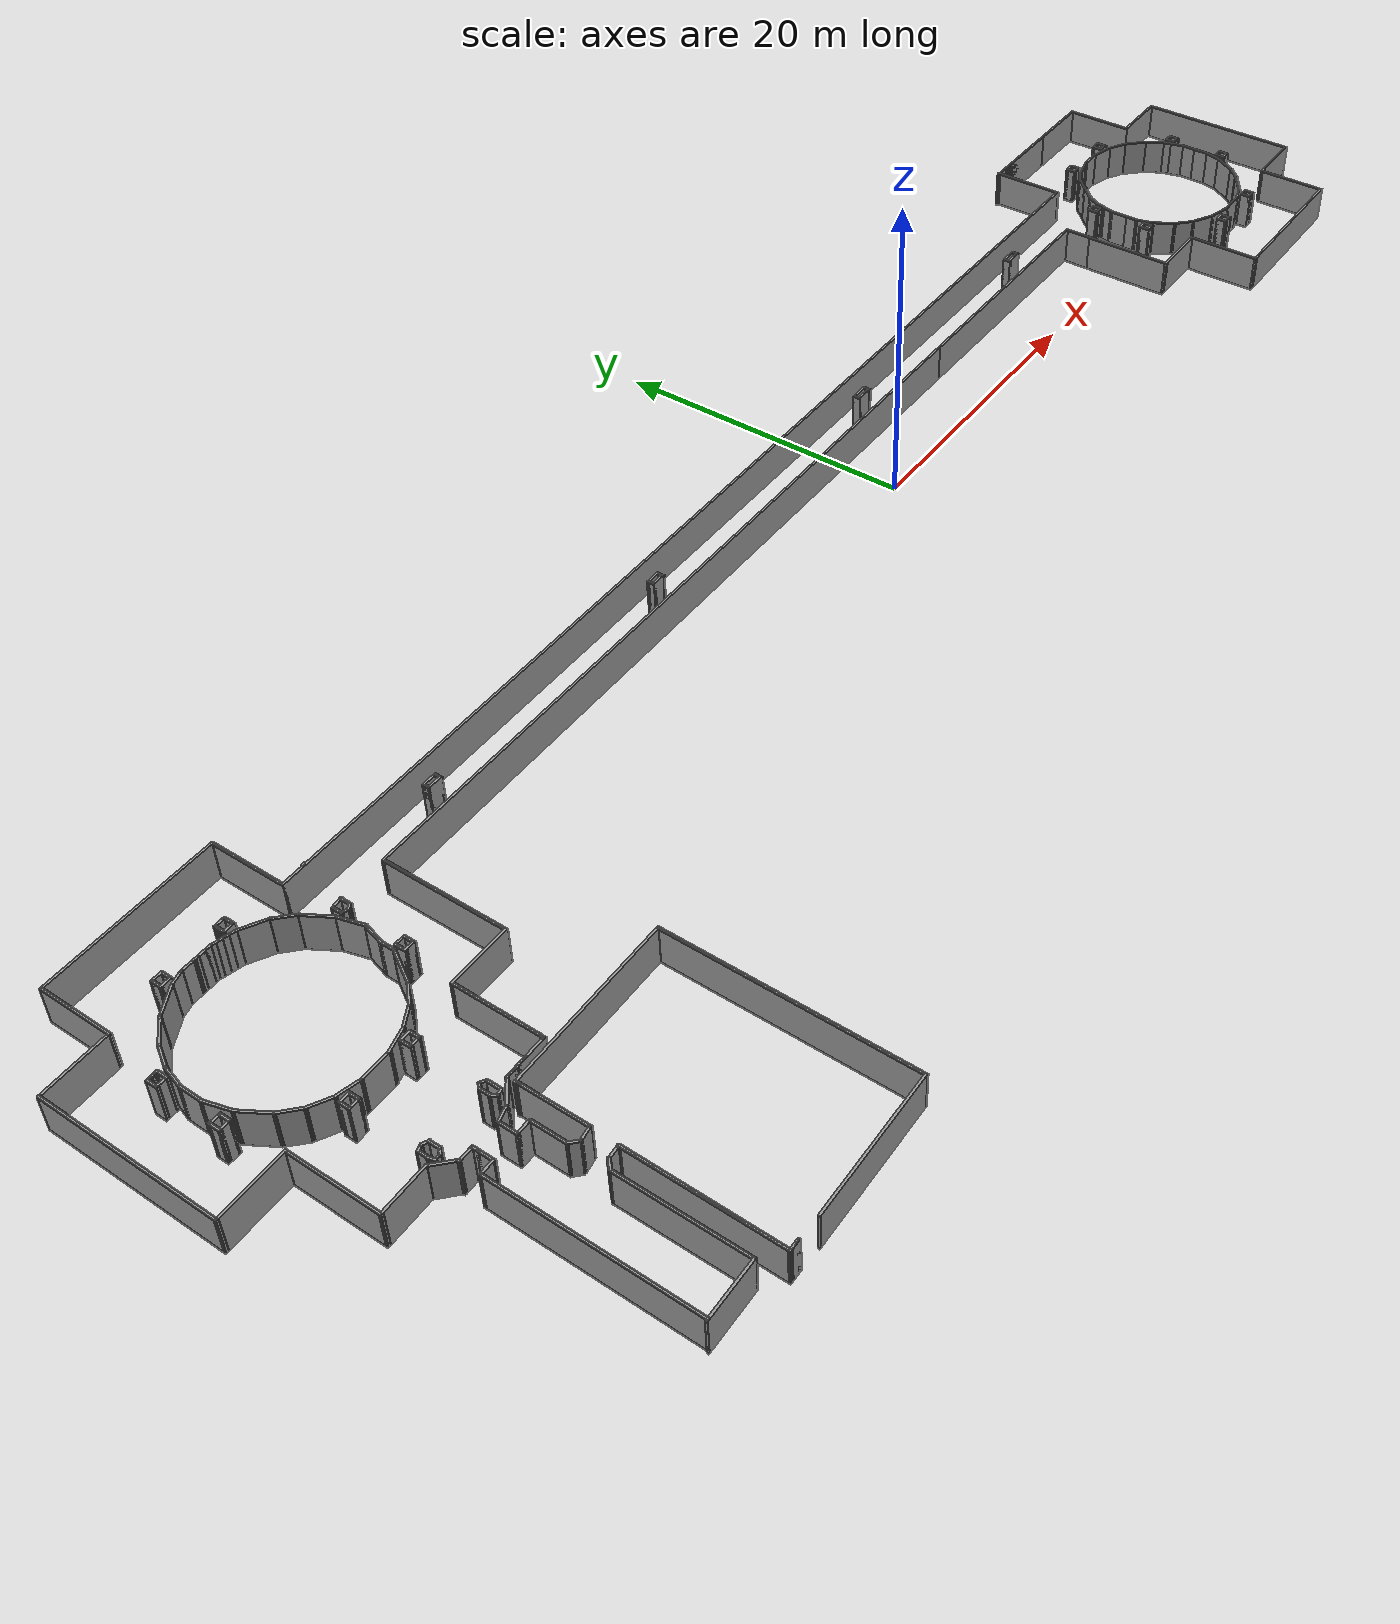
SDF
<?xml version='1.0'?>
<sdf version='1.7'>
  <model name='TD_v2'>
    <pose>-6.31602 -6.69767 0 0 -0 0</pose>
    <link name='Wall_0'>
      <collision name='Wall_0_Collision'>
        <geometry>
          <box>
            <size>4.25 0.15 2.5</size>
          </box>
        </geometry>
        <pose>0 0 1.25 0 -0 0</pose>
      </collision>
      <visual name='Wall_0_Visual'>
        <pose>0 0 1.25 0 -0 0</pose>
        <geometry>
          <box>
            <size>4.25 0.15 2.5</size>
          </box>
        </geometry>
        <material>
          <script>
            <uri>file://media/materials/scripts/gazebo.material</uri>
            <name>Gazebo/Grey</name>
          </script>
          <ambient>1 1 1 1</ambient>
        </material>
        <meta>
          <layer>0</layer>
        </meta>
      </visual>
      <pose>-41.4756 -5.51211 0 0 -0 1.5708</pose>
    </link>
    <link name='Wall_1'>
      <collision name='Wall_1_Collision'>
        <geometry>
          <box>
            <size>0.279365 0.15 2.5</size>
          </box>
        </geometry>
        <pose>0 0 1.25 0 -0 0</pose>
      </collision>
      <visual name='Wall_1_Visual'>
        <pose>0 0 1.25 0 -0 0</pose>
        <geometry>
          <box>
            <size>0.279365 0.15 2.5</size>
          </box>
        </geometry>
        <material>
          <script>
            <uri>file://media/materials/scripts/gazebo.material</uri>
            <name>Gazebo/Grey</name>
          </script>
          <ambient>1 1 1 1</ambient>
        </material>
        <meta>
          <layer>0</layer>
        </meta>
      </visual>
      <pose>-41.4889 -3.37221 0 0 -0 1.7779</pose>
    </link>
    <link name='Wall_10'>
      <collision name='Wall_10_Collision'>
        <geometry>
          <box>
            <size>9.25 0.15 2.5</size>
          </box>
        </geometry>
        <pose>0 0 1.25 0 -0 0</pose>
      </collision>
      <visual name='Wall_10_Visual'>
        <pose>0 0 1.25 0 -0 0</pose>
        <geometry>
          <box>
            <size>9.25 0.15 2.5</size>
          </box>
        </geometry>
        <material>
          <script>
            <uri>file://media/materials/scripts/gazebo.material</uri>
            <name>Gazebo/Grey</name>
          </script>
          <ambient>1 1 1 1</ambient>
        </material>
        <meta>
          <layer>0</layer>
        </meta>
      </visual>
      <pose>-41.5592 -13.7512 0 0 -0 1.56753</pose>
    </link>
    <link name='Wall_104'>
      <collision name='Wall_104_Collision'>
        <geometry>
          <box>
            <size>4.25 0.15 2.5</size>
          </box>
        </geometry>
        <pose>0 0 1.25 0 -0 0</pose>
      </collision>
      <visual name='Wall_104_Visual'>
        <pose>0 0 1.25 0 -0 0</pose>
        <geometry>
          <box>
            <size>4.25 0.15 2.5</size>
          </box>
        </geometry>
        <material>
          <script>
            <uri>file://media/materials/scripts/gazebo.material</uri>
            <name>Gazebo/Grey</name>
          </script>
          <ambient>1 1 1 1</ambient>
        </material>
        <meta>
          <layer>0</layer>
        </meta>
      </visual>
      <pose>51.8827 2.59678 0 0 -0 3.14159</pose>
    </link>
    <link name='Wall_105'>
      <collision name='Wall_105_Collision'>
        <geometry>
          <box>
            <size>4.75 0.15 2.5</size>
          </box>
        </geometry>
        <pose>0 0 1.25 0 -0 0</pose>
      </collision>
      <visual name='Wall_105_Visual'>
        <pose>0 0 1.25 0 -0 0</pose>
        <geometry>
          <box>
            <size>4.75 0.15 2.5</size>
          </box>
        </geometry>
        <material>
          <script>
            <uri>file://media/materials/scripts/gazebo.material</uri>
            <name>Gazebo/Grey</name>
          </script>
          <ambient>1 1 1 1</ambient>
        </material>
        <meta>
          <layer>0</layer>
        </meta>
      </visual>
      <pose>49.8327 0.296781 0 0 -0 -1.5708</pose>
    </link>
    <link name='Wall_107'>
      <collision name='Wall_107_Collision'>
        <geometry>
          <box>
            <size>11.1374 0.15 2.5</size>
          </box>
        </geometry>
        <pose>0 0 1.25 0 -0 0</pose>
      </collision>
      <visual name='Wall_107_Visual'>
        <pose>0 0 1.25 0 -0 0</pose>
        <geometry>
          <box>
            <size>11.1374 0.15 2.5</size>
          </box>
        </geometry>
        <material>
          <script>
            <uri>file://media/materials/scripts/gazebo.material</uri>
            <name>Gazebo/Grey</name>
          </script>
          <ambient>1 1 1 1</ambient>
        </material>
        <meta>
          <layer>0</layer>
        </meta>
      </visual>
      <pose>44.3391 -2.00322 0 0 -0 3.14159</pose>
    </link>
    <link name='Wall_108'>
      <collision name='Wall_108_Collision'>
        <geometry>
          <box>
            <size>5 0.15 2.5</size>
          </box>
        </geometry>
        <pose>0 0 1.25 0 -0 0</pose>
      </collision>
      <visual name='Wall_108_Visual'>
        <pose>0 0 1.25 0 -0 0</pose>
        <geometry>
          <box>
            <size>5 0.15 2.5</size>
          </box>
        </geometry>
        <material>
          <script>
            <uri>file://media/materials/scripts/gazebo.material</uri>
            <name>Gazebo/Grey</name>
          </script>
          <ambient>1 1 1 1</ambient>
        </material>
        <meta>
          <layer>0</layer>
        </meta>
      </visual>
      <pose>38.8455 0.421781 0 0 -0 1.5708</pose>
    </link>
    <link name='Wall_109'>
      <collision name='Wall_109_Collision'>
        <geometry>
          <box>
            <size>4.11337 0.15 2.5</size>
          </box>
        </geometry>
        <pose>0 0 1.25 0 -0 0</pose>
      </collision>
      <visual name='Wall_109_Visual'>
        <pose>0 0 1.25 0 -0 0</pose>
        <geometry>
          <box>
            <size>4.11337 0.15 2.5</size>
          </box>
        </geometry>
        <material>
          <script>
            <uri>file://media/materials/scripts/gazebo.material</uri>
            <name>Gazebo/Grey</name>
          </script>
          <ambient>1 1 1 1</ambient>
        </material>
        <meta>
          <layer>0</layer>
        </meta>
      </visual>
      <pose>36.8641 2.84678 0 0 -0 3.14159</pose>
    </link>
    <link name='Wall_11'>
      <collision name='Wall_11_Collision'>
        <geometry>
          <box>
            <size>0.15 0.15 2.5</size>
          </box>
        </geometry>
        <pose>0 0 1.25 0 -0 0</pose>
      </collision>
      <visual name='Wall_11_Visual'>
        <pose>0 0 1.25 0 -0 0</pose>
        <geometry>
          <box>
            <size>0.15 0.15 2.5</size>
          </box>
        </geometry>
        <material>
          <script>
            <uri>file://media/materials/scripts/gazebo.material</uri>
            <name>Gazebo/Grey</name>
          </script>
          <ambient>1 1 1 1</ambient>
        </material>
        <meta>
          <layer>0</layer>
        </meta>
      </visual>
      <pose>-41.5443 -9.2012 0 0 -0 0</pose>
    </link>
    <link name='Wall_110'>
      <collision name='Wall_110_Collision'>
        <geometry>
          <box>
            <size>6 0.15 2.5</size>
          </box>
        </geometry>
        <pose>0 0 1.25 0 -0 0</pose>
      </collision>
      <visual name='Wall_110_Visual'>
        <pose>0 0 1.25 0 -0 0</pose>
        <geometry>
          <box>
            <size>6 0.15 2.5</size>
          </box>
        </geometry>
        <material>
          <script>
            <uri>file://media/materials/scripts/gazebo.material</uri>
            <name>Gazebo/Grey</name>
          </script>
          <ambient>1 1 1 1</ambient>
        </material>
        <meta>
          <layer>0</layer>
        </meta>
      </visual>
      <pose>34.8827 5.77178 0 0 -0 1.5708</pose>
    </link>
    <link name='Wall_111'>
      <collision name='Wall_111_Collision'>
        <geometry>
          <box>
            <size>0.16 0.15 2.5</size>
          </box>
        </geometry>
        <pose>0 0 1.25 0 -0 0</pose>
      </collision>
      <visual name='Wall_111_Visual'>
        <pose>0 0 1.25 0 -0 0</pose>
        <geometry>
          <box>
            <size>0.16 0.15 2.5</size>
          </box>
        </geometry>
        <material>
          <script>
            <uri>file://media/materials/scripts/gazebo.material</uri>
            <name>Gazebo/Grey</name>
          </script>
          <ambient>1 1 1 1</ambient>
        </material>
        <meta>
          <layer>0</layer>
        </meta>
      </visual>
      <pose>34.8877 8.69678 0 0 -0 0</pose>
    </link>
    <link name='Wall_112'>
      <collision name='Wall_112_Collision'>
        <geometry>
          <box>
            <size>0.16 0.15 2.5</size>
          </box>
        </geometry>
        <pose>0 0 1.25 0 -0 0</pose>
      </collision>
      <visual name='Wall_112_Visual'>
        <pose>0 0 1.25 0 -0 0</pose>
        <geometry>
          <box>
            <size>0.16 0.15 2.5</size>
          </box>
        </geometry>
        <material>
          <script>
            <uri>file://media/materials/scripts/gazebo.material</uri>
            <name>Gazebo/Grey</name>
          </script>
          <ambient>1 1 1 1</ambient>
        </material>
        <meta>
          <layer>0</layer>
        </meta>
      </visual>
      <pose>34.8877 8.69678 0 0 -0 3.14159</pose>
    </link>
    <link name='Wall_116'>
      <collision name='Wall_116_Collision'>
        <geometry>
          <box>
            <size>2 0.15 2.5</size>
          </box>
        </geometry>
        <pose>0 0 1.25 0 -0 0</pose>
      </collision>
      <visual name='Wall_116_Visual'>
        <pose>0 0 1.25 0 -0 0</pose>
        <geometry>
          <box>
            <size>2 0.15 2.5</size>
          </box>
        </geometry>
        <material>
          <script>
            <uri>file://media/materials/scripts/gazebo.material</uri>
            <name>Gazebo/Grey</name>
          </script>
          <ambient>1 1 1 1</ambient>
        </material>
        <meta>
          <layer>0</layer>
        </meta>
      </visual>
      <pose>34.8927 9.62178 0 0 -0 1.5708</pose>
    </link>
    <link name='Wall_118'>
      <collision name='Wall_118_Collision'>
        <geometry>
          <box>
            <size>17.5 0.15 2.5</size>
          </box>
        </geometry>
        <pose>0 0 1.25 0 -0 0</pose>
      </collision>
      <visual name='Wall_118_Visual'>
        <pose>0 0 1.25 0 -0 0</pose>
        <geometry>
          <box>
            <size>17.5 0.15 2.5</size>
          </box>
        </geometry>
        <material>
          <script>
            <uri>file://media/materials/scripts/gazebo.material</uri>
            <name>Gazebo/Grey</name>
          </script>
          <ambient>1 1 1 1</ambient>
        </material>
        <meta>
          <layer>0</layer>
        </meta>
      </visual>
      <pose>26.2177 10.5468 0 0 -0 3.14159</pose>
    </link>
    <link name='Wall_12'>
      <collision name='Wall_12_Collision'>
        <geometry>
          <box>
            <size>9.25035 0.15 2.5</size>
          </box>
        </geometry>
        <pose>0 0 1.25 0 -0 0</pose>
      </collision>
      <visual name='Wall_12_Visual'>
        <pose>0 0 1.25 0 -0 0</pose>
        <geometry>
          <box>
            <size>9.25035 0.15 2.5</size>
          </box>
        </geometry>
        <material>
          <script>
            <uri>file://media/materials/scripts/gazebo.material</uri>
            <name>Gazebo/Grey</name>
          </script>
          <ambient>1 1 1 1</ambient>
        </material>
        <meta>
          <layer>0</layer>
        </meta>
      </visual>
      <pose>-41.5476 -13.7512 0 0 -0 -1.57661</pose>
    </link>
    <link name='Wall_120'>
      <collision name='Wall_120_Collision'>
        <geometry>
          <box>
            <size>52.75 0.15 2.5</size>
          </box>
        </geometry>
        <pose>0 0 1.25 0 -0 0</pose>
      </collision>
      <visual name='Wall_120_Visual'>
        <pose>0 0 1.25 0 -0 0</pose>
        <geometry>
          <box>
            <size>52.75 0.15 2.5</size>
          </box>
        </geometry>
        <material>
          <script>
            <uri>file://media/materials/scripts/gazebo.material</uri>
            <name>Gazebo/Grey</name>
          </script>
          <ambient>1 1 1 1</ambient>
        </material>
        <meta>
          <layer>0</layer>
        </meta>
      </visual>
      <pose>-8.7573 10.5468 0 0 -0 3.14159</pose>
    </link>
    <link name='Wall_121'>
      <collision name='Wall_121_Collision'>
        <geometry>
          <box>
            <size>8 0.15 2.5</size>
          </box>
        </geometry>
        <pose>0 0 1.25 0 -0 0</pose>
      </collision>
      <visual name='Wall_121_Visual'>
        <pose>0 0 1.25 0 -0 0</pose>
        <geometry>
          <box>
            <size>8 0.15 2.5</size>
          </box>
        </geometry>
        <material>
          <script>
            <uri>file://media/materials/scripts/gazebo.material</uri>
            <name>Gazebo/Grey</name>
          </script>
          <ambient>1 1 1 1</ambient>
        </material>
        <meta>
          <layer>0</layer>
        </meta>
      </visual>
      <pose>-35.0573 6.62178 0 0 -0 -1.5708</pose>
    </link>
    <link name='Wall_122'>
      <collision name='Wall_122_Collision'>
        <geometry>
          <box>
            <size>4 0.15 2.5</size>
          </box>
        </geometry>
        <pose>0 0 1.25 0 -0 0</pose>
      </collision>
      <visual name='Wall_122_Visual'>
        <pose>0 0 1.25 0 -0 0</pose>
        <geometry>
          <box>
            <size>4 0.15 2.5</size>
          </box>
        </geometry>
        <material>
          <script>
            <uri>file://media/materials/scripts/gazebo.material</uri>
            <name>Gazebo/Grey</name>
          </script>
          <ambient>1 1 1 1</ambient>
        </material>
        <meta>
          <layer>0</layer>
        </meta>
      </visual>
      <pose>-36.9823 2.69678 0 0 -0 3.14159</pose>
    </link>
    <link name='Wall_123'>
      <collision name='Wall_123_Collision'>
        <geometry>
          <box>
            <size>5.5 0.15 2.5</size>
          </box>
        </geometry>
        <pose>0 0 1.25 0 -0 0</pose>
      </collision>
      <visual name='Wall_123_Visual'>
        <pose>0 0 1.25 0 -0 0</pose>
        <geometry>
          <box>
            <size>5.5 0.15 2.5</size>
          </box>
        </geometry>
        <material>
          <script>
            <uri>file://media/materials/scripts/gazebo.material</uri>
            <name>Gazebo/Grey</name>
          </script>
          <ambient>1 1 1 1</ambient>
        </material>
        <meta>
          <layer>0</layer>
        </meta>
      </visual>
      <pose>-38.9073 0.02178 0 0 -0 -1.5708</pose>
    </link>
    <link name='Wall_124'>
      <collision name='Wall_124_Collision'>
        <geometry>
          <box>
            <size>0.25 0.15 2.5</size>
          </box>
        </geometry>
        <pose>0 0 1.25 0 -0 0</pose>
      </collision>
      <visual name='Wall_124_Visual'>
        <pose>0 0 1.25 0 -0 0</pose>
        <geometry>
          <box>
            <size>0.25 0.15 2.5</size>
          </box>
        </geometry>
        <material>
          <script>
            <uri>file://media/materials/scripts/gazebo.material</uri>
            <name>Gazebo/Grey</name>
          </script>
          <ambient>1 1 1 1</ambient>
        </material>
        <meta>
          <layer>0</layer>
        </meta>
      </visual>
      <pose>-38.9202 -2.70152 0 0 -0 -1.8326</pose>
    </link>
    <link name='Wall_126'>
      <collision name='Wall_126_Collision'>
        <geometry>
          <box>
            <size>1 0.15 2.5</size>
          </box>
        </geometry>
        <pose>0 0 1.25 0 -0 0</pose>
      </collision>
      <visual name='Wall_126_Visual'>
        <pose>0 0 1.25 0 -0 0</pose>
        <geometry>
          <box>
            <size>1 0.15 2.5</size>
          </box>
        </geometry>
        <material>
          <script>
            <uri>file://media/materials/scripts/gazebo.material</uri>
            <name>Gazebo/Grey</name>
          </script>
          <ambient>1 1 1 1</ambient>
        </material>
        <meta>
          <layer>0</layer>
        </meta>
      </visual>
      <pose>-43.1204 -5.15327 0 0 -0 3.14159</pose>
    </link>
    <link name='Wall_127'>
      <collision name='Wall_127_Collision'>
        <geometry>
          <box>
            <size>1.25 0.15 2.5</size>
          </box>
        </geometry>
        <pose>0 0 1.25 0 -0 0</pose>
      </collision>
      <visual name='Wall_127_Visual'>
        <pose>0 0 1.25 0 -0 0</pose>
        <geometry>
          <box>
            <size>1.25 0.15 2.5</size>
          </box>
        </geometry>
        <material>
          <script>
            <uri>file://media/materials/scripts/gazebo.material</uri>
            <name>Gazebo/Grey</name>
          </script>
          <ambient>1 1 1 1</ambient>
        </material>
        <meta>
          <layer>0</layer>
        </meta>
      </visual>
      <pose>-43.5454 -4.60327 0 0 -0 1.5708</pose>
    </link>
    <link name='Wall_132'>
      <collision name='Wall_132_Collision'>
        <geometry>
          <box>
            <size>0.25 0.15 2.5</size>
          </box>
        </geometry>
        <pose>0 0 1.25 0 -0 0</pose>
      </collision>
      <visual name='Wall_132_Visual'>
        <pose>0 0 1.25 0 -0 0</pose>
        <geometry>
          <box>
            <size>0.25 0.15 2.5</size>
          </box>
        </geometry>
        <material>
          <script>
            <uri>file://media/materials/scripts/gazebo.material</uri>
            <name>Gazebo/Grey</name>
          </script>
          <ambient>1 1 1 1</ambient>
        </material>
        <meta>
          <layer>0</layer>
        </meta>
      </visual>
      <pose>-38.9202 -2.70152 0 0 -0 -1.8326</pose>
    </link>
    <link name='Wall_133'>
      <collision name='Wall_133_Collision'>
        <geometry>
          <box>
            <size>0.25 0.15 2.5</size>
          </box>
        </geometry>
        <pose>0 0 1.25 0 -0 0</pose>
      </collision>
      <visual name='Wall_133_Visual'>
        <pose>0 0 1.25 0 -0 0</pose>
        <geometry>
          <box>
            <size>0.25 0.15 2.5</size>
          </box>
        </geometry>
        <material>
          <script>
            <uri>file://media/materials/scripts/gazebo.material</uri>
            <name>Gazebo/Grey</name>
          </script>
          <ambient>1 1 1 1</ambient>
        </material>
        <meta>
          <layer>0</layer>
        </meta>
      </visual>
      <pose>-38.9332 -2.79981 0 0 -0 -1.5708</pose>
    </link>
    <link name='Wall_134'>
      <collision name='Wall_134_Collision'>
        <geometry>
          <box>
            <size>0.16 0.15 2.5</size>
          </box>
        </geometry>
        <pose>0 0 1.25 0 -0 0</pose>
      </collision>
      <visual name='Wall_134_Visual'>
        <pose>0 0 1.25 0 -0 0</pose>
        <geometry>
          <box>
            <size>0.16 0.15 2.5</size>
          </box>
        </geometry>
        <material>
          <script>
            <uri>file://media/materials/scripts/gazebo.material</uri>
            <name>Gazebo/Grey</name>
          </script>
          <ambient>1 1 1 1</ambient>
        </material>
        <meta>
          <layer>0</layer>
        </meta>
      </visual>
      <pose>-38.9282 -2.84981 0 0 -0 0</pose>
    </link>
    <link name='Wall_135'>
      <collision name='Wall_135_Collision'>
        <geometry>
          <box>
            <size>2.75 0.15 2.5</size>
          </box>
        </geometry>
        <pose>0 0 1.25 0 -0 0</pose>
      </collision>
      <visual name='Wall_135_Visual'>
        <pose>0 0 1.25 0 -0 0</pose>
        <geometry>
          <box>
            <size>2.75 0.15 2.5</size>
          </box>
        </geometry>
        <material>
          <script>
            <uri>file://media/materials/scripts/gazebo.material</uri>
            <name>Gazebo/Grey</name>
          </script>
          <ambient>1 1 1 1</ambient>
        </material>
        <meta>
          <layer>0</layer>
        </meta>
      </visual>
      <pose>-40.2232 -2.84981 0 0 -0 3.14159</pose>
    </link>
    <link name='Wall_136'>
      <collision name='Wall_136_Collision'>
        <geometry>
          <box>
            <size>0.15 0.15 2.5</size>
          </box>
        </geometry>
        <pose>0 0 1.25 0 -0 0</pose>
      </collision>
      <visual name='Wall_136_Visual'>
        <pose>0 0 1.25 0 -0 0</pose>
        <geometry>
          <box>
            <size>0.15 0.15 2.5</size>
          </box>
        </geometry>
        <material>
          <script>
            <uri>file://media/materials/scripts/gazebo.material</uri>
            <name>Gazebo/Grey</name>
          </script>
          <ambient>1 1 1 1</ambient>
        </material>
        <meta>
          <layer>0</layer>
        </meta>
      </visual>
      <pose>-41.5232 -2.84981 0 0 -0 0</pose>
    </link>
    <link name='Wall_137'>
      <collision name='Wall_137_Collision'>
        <geometry>
          <box>
            <size>0.15 0.15 2.5</size>
          </box>
        </geometry>
        <pose>0 0 1.25 0 -0 0</pose>
      </collision>
      <visual name='Wall_137_Visual'>
        <pose>0 0 1.25 0 -0 0</pose>
        <geometry>
          <box>
            <size>0.15 0.15 2.5</size>
          </box>
        </geometry>
        <material>
          <script>
            <uri>file://media/materials/scripts/gazebo.material</uri>
            <name>Gazebo/Grey</name>
          </script>
          <ambient>1 1 1 1</ambient>
        </material>
        <meta>
          <layer>0</layer>
        </meta>
      </visual>
      <pose>-41.5232 -2.84981 0 0 -0 0</pose>
    </link>
    <link name='Wall_139'>
      <collision name='Wall_139_Collision'>
        <geometry>
          <box>
            <size>1 0.15 2.5</size>
          </box>
        </geometry>
        <pose>0 0 1.25 0 -0 0</pose>
      </collision>
      <visual name='Wall_139_Visual'>
        <pose>0 0 1.25 0 -0 0</pose>
        <geometry>
          <box>
            <size>1 0.15 2.5</size>
          </box>
        </geometry>
        <material>
          <script>
            <uri>file://media/materials/scripts/gazebo.material</uri>
            <name>Gazebo/Grey</name>
          </script>
          <ambient>1 1 1 1</ambient>
        </material>
        <meta>
          <layer>0</layer>
        </meta>
      </visual>
      <pose>-43.1349 -3.94327 0 0 -0 0.261799</pose>
    </link>
    <link name='Wall_140'>
      <collision name='Wall_140_Collision'>
        <geometry>
          <box>
            <size>1.70244 0.15 2.5</size>
          </box>
        </geometry>
        <pose>0 0 1.25 0 -0 0</pose>
      </collision>
      <visual name='Wall_140_Visual'>
        <pose>0 0 1.25 0 -0 0</pose>
        <geometry>
          <box>
            <size>1.70244 0.15 2.5</size>
          </box>
        </geometry>
        <material>
          <script>
            <uri>file://media/materials/scripts/gazebo.material</uri>
            <name>Gazebo/Grey</name>
          </script>
          <ambient>1 1 1 1</ambient>
        </material>
        <meta>
          <layer>0</layer>
        </meta>
      </visual>
      <pose>-42.1238 -3.34154 0 0 -0 0.686062</pose>
    </link>
    <link name='Wall_141'>
      <collision name='Wall_141_Collision'>
        <geometry>
          <box>
            <size>1.5 0.15 2.5</size>
          </box>
        </geometry>
        <pose>0 0 1.25 0 -0 0</pose>
      </collision>
      <visual name='Wall_141_Visual'>
        <pose>0 0 1.25 0 -0 0</pose>
        <geometry>
          <box>
            <size>1.5 0.15 2.5</size>
          </box>
        </geometry>
        <material>
          <script>
            <uri>file://media/materials/scripts/gazebo.material</uri>
            <name>Gazebo/Grey</name>
          </script>
          <ambient>1 1 1 1</ambient>
        </material>
        <meta>
          <layer>0</layer>
        </meta>
      </visual>
      <pose>-40.8482 -2.84981 0 0 -0 0</pose>
    </link>
    <link name='Wall_143'>
      <collision name='Wall_143_Collision'>
        <geometry>
          <box>
            <size>0.5 0.15 2.5</size>
          </box>
        </geometry>
        <pose>0 0 1.25 0 -0 0</pose>
      </collision>
      <visual name='Wall_143_Visual'>
        <pose>0 0 1.25 0 -0 0</pose>
        <geometry>
          <box>
            <size>0.5 0.15 2.5</size>
          </box>
        </geometry>
        <material>
          <script>
            <uri>file://media/materials/scripts/gazebo.material</uri>
            <name>Gazebo/Grey</name>
          </script>
          <ambient>1 1 1 1</ambient>
        </material>
        <meta>
          <layer>0</layer>
        </meta>
      </visual>
      <pose>-44.507 13.7137 0 0 -0 0</pose>
    </link>
    <link name='Wall_145'>
      <collision name='Wall_145_Collision'>
        <geometry>
          <box>
            <size>0.5 0.15 2.5</size>
          </box>
        </geometry>
        <pose>0 0 1.25 0 -0 0</pose>
      </collision>
      <visual name='Wall_145_Visual'>
        <pose>0 0 1.25 0 -0 0</pose>
        <geometry>
          <box>
            <size>0.5 0.15 2.5</size>
          </box>
        </geometry>
        <material>
          <script>
            <uri>file://media/materials/scripts/gazebo.material</uri>
            <name>Gazebo/Grey</name>
          </script>
          <ambient>1 1 1 1</ambient>
        </material>
        <meta>
          <layer>0</layer>
        </meta>
      </visual>
      <pose>-44.157 13.7137 0 0 -0 0</pose>
    </link>
    <link name='Wall_146'>
      <collision name='Wall_146_Collision'>
        <geometry>
          <box>
            <size>0.5 0.15 2.5</size>
          </box>
        </geometry>
        <pose>0 0 1.25 0 -0 0</pose>
      </collision>
      <visual name='Wall_146_Visual'>
        <pose>0 0 1.25 0 -0 0</pose>
        <geometry>
          <box>
            <size>0.5 0.15 2.5</size>
          </box>
        </geometry>
        <material>
          <script>
            <uri>file://media/materials/scripts/gazebo.material</uri>
            <name>Gazebo/Grey</name>
          </script>
          <ambient>1 1 1 1</ambient>
        </material>
        <meta>
          <layer>0</layer>
        </meta>
      </visual>
      <pose>-43.807 13.7137 0 0 -0 0</pose>
    </link>
    <link name='Wall_148'>
      <collision name='Wall_148_Collision'>
        <geometry>
          <box>
            <size>0.5 0.15 2.5</size>
          </box>
        </geometry>
        <pose>0 0 1.25 0 -0 0</pose>
      </collision>
      <visual name='Wall_148_Visual'>
        <pose>0 0 1.25 0 -0 0</pose>
        <geometry>
          <box>
            <size>0.5 0.15 2.5</size>
          </box>
        </geometry>
        <material>
          <script>
            <uri>file://media/materials/scripts/gazebo.material</uri>
            <name>Gazebo/Grey</name>
          </script>
          <ambient>1 1 1 1</ambient>
        </material>
        <meta>
          <layer>0</layer>
        </meta>
      </visual>
      <pose>-43.463 13.6685 0 0 -0 -0.261799</pose>
    </link>
    <link name='Wall_15'>
      <collision name='Wall_15_Collision'>
        <geometry>
          <box>
            <size>0.75 0.15 2.5</size>
          </box>
        </geometry>
        <pose>0 0 1.25 0 -0 0</pose>
      </collision>
      <visual name='Wall_15_Visual'>
        <pose>0 0 1.25 0 -0 0</pose>
        <geometry>
          <box>
            <size>0.75 0.15 2.5</size>
          </box>
        </geometry>
        <material>
          <script>
            <uri>file://media/materials/scripts/gazebo.material</uri>
            <name>Gazebo/Grey</name>
          </script>
          <ambient>1 1 1 1</ambient>
        </material>
        <meta>
          <layer>0</layer>
        </meta>
      </visual>
      <pose>-41.2741 -18.3012 0 0 -0 0</pose>
    </link>
    <link name='Wall_151'>
      <collision name='Wall_151_Collision'>
        <geometry>
          <box>
            <size>0.5 0.15 2.5</size>
          </box>
        </geometry>
        <pose>0 0 1.25 0 -0 0</pose>
      </collision>
      <visual name='Wall_151_Visual'>
        <pose>0 0 1.25 0 -0 0</pose>
        <geometry>
          <box>
            <size>0.5 0.15 2.5</size>
          </box>
        </geometry>
        <material>
          <script>
            <uri>file://media/materials/scripts/gazebo.material</uri>
            <name>Gazebo/Grey</name>
          </script>
          <ambient>1 1 1 1</ambient>
        </material>
        <meta>
          <layer>0</layer>
        </meta>
      </visual>
      <pose>-43.1249 13.5779 0 0 -0 -0.261799</pose>
    </link>
    <link name='Wall_152'>
      <collision name='Wall_152_Collision'>
        <geometry>
          <box>
            <size>0.5 0.15 2.5</size>
          </box>
        </geometry>
        <pose>0 0 1.25 0 -0 0</pose>
      </collision>
      <visual name='Wall_152_Visual'>
        <pose>0 0 1.25 0 -0 0</pose>
        <geometry>
          <box>
            <size>0.5 0.15 2.5</size>
          </box>
        </geometry>
        <material>
          <script>
            <uri>file://media/materials/scripts/gazebo.material</uri>
            <name>Gazebo/Grey</name>
          </script>
          <ambient>1 1 1 1</ambient>
        </material>
        <meta>
          <layer>0</layer>
        </meta>
      </visual>
      <pose>-42.7869 13.4873 0 0 -0 -0.261799</pose>
    </link>
    <link name='Wall_153'>
      <collision name='Wall_153_Collision'>
        <geometry>
          <box>
            <size>0.5 0.15 2.5</size>
          </box>
        </geometry>
        <pose>0 0 1.25 0 -0 0</pose>
      </collision>
      <visual name='Wall_153_Visual'>
        <pose>0 0 1.25 0 -0 0</pose>
        <geometry>
          <box>
            <size>0.5 0.15 2.5</size>
          </box>
        </geometry>
        <material>
          <script>
            <uri>file://media/materials/scripts/gazebo.material</uri>
            <name>Gazebo/Grey</name>
          </script>
          <ambient>1 1 1 1</ambient>
        </material>
        <meta>
          <layer>0</layer>
        </meta>
      </visual>
      <pose>-42.4488 13.3967 0 0 -0 -0.261799</pose>
    </link>
    <link name='Wall_155'>
      <collision name='Wall_155_Collision'>
        <geometry>
          <box>
            <size>1.75 0.15 2.5</size>
          </box>
        </geometry>
        <pose>0 0 1.25 0 -0 0</pose>
      </collision>
      <visual name='Wall_155_Visual'>
        <pose>0 0 1.25 0 -0 0</pose>
        <geometry>
          <box>
            <size>1.75 0.15 2.5</size>
          </box>
        </geometry>
        <material>
          <script>
            <uri>file://media/materials/scripts/gazebo.material</uri>
            <name>Gazebo/Grey</name>
          </script>
          <ambient>1 1 1 1</ambient>
        </material>
        <meta>
          <layer>0</layer>
        </meta>
      </visual>
      <pose>-41.5869 12.9514 0 0 -0 -0.523599</pose>
    </link>
    <link name='Wall_156'>
      <collision name='Wall_156_Collision'>
        <geometry>
          <box>
            <size>1.5 0.15 2.5</size>
          </box>
        </geometry>
        <pose>0 0 1.25 0 -0 0</pose>
      </collision>
      <visual name='Wall_156_Visual'>
        <pose>0 0 1.25 0 -0 0</pose>
        <geometry>
          <box>
            <size>1.5 0.15 2.5</size>
          </box>
        </geometry>
        <material>
          <script>
            <uri>file://media/materials/scripts/gazebo.material</uri>
            <name>Gazebo/Grey</name>
          </script>
          <ambient>1 1 1 1</ambient>
        </material>
        <meta>
          <layer>0</layer>
        </meta>
      </visual>
      <pose>-40.4168 12.0741 0 0 -0 -0.785398</pose>
    </link>
    <link name='Wall_158'>
      <collision name='Wall_158_Collision'>
        <geometry>
          <box>
            <size>2 0.15 2.5</size>
          </box>
        </geometry>
        <pose>0 0 1.25 0 -0 0</pose>
      </collision>
      <visual name='Wall_158_Visual'>
        <pose>0 0 1.25 0 -0 0</pose>
        <geometry>
          <box>
            <size>2 0.15 2.5</size>
          </box>
        </geometry>
        <material>
          <script>
            <uri>file://media/materials/scripts/gazebo.material</uri>
            <name>Gazebo/Grey</name>
          </script>
          <ambient>1 1 1 1</ambient>
        </material>
        <meta>
          <layer>0</layer>
        </meta>
      </visual>
      <pose>-39.477 10.7957 0 0 -0 -1.0472</pose>
    </link>
    <link name='Wall_159'>
      <collision name='Wall_159_Collision'>
        <geometry>
          <box>
            <size>1.75 0.15 2.5</size>
          </box>
        </geometry>
        <pose>0 0 1.25 0 -0 0</pose>
      </collision>
      <visual name='Wall_159_Visual'>
        <pose>0 0 1.25 0 -0 0</pose>
        <geometry>
          <box>
            <size>1.75 0.15 2.5</size>
          </box>
        </geometry>
        <material>
          <script>
            <uri>file://media/materials/scripts/gazebo.material</uri>
            <name>Gazebo/Grey</name>
          </script>
          <ambient>1 1 1 1</ambient>
        </material>
        <meta>
          <layer>0</layer>
        </meta>
      </visual>
      <pose>-38.8075 9.22192 0 0 -0 -1.309</pose>
    </link>
    <link name='Wall_16'>
      <collision name='Wall_16_Collision'>
        <geometry>
          <box>
            <size>0.75 0.15 2.5</size>
          </box>
        </geometry>
        <pose>0 0 1.25 0 -0 0</pose>
      </collision>
      <visual name='Wall_16_Visual'>
        <pose>0 0 1.25 0 -0 0</pose>
        <geometry>
          <box>
            <size>0.75 0.15 2.5</size>
          </box>
        </geometry>
        <material>
          <script>
            <uri>file://media/materials/scripts/gazebo.material</uri>
            <name>Gazebo/Grey</name>
          </script>
          <ambient>1 1 1 1</ambient>
        </material>
        <meta>
          <layer>0</layer>
        </meta>
      </visual>
      <pose>-41.2608 -18.3012 0 0 -0 3.14159</pose>
    </link>
    <link name='Wall_162'>
      <collision name='Wall_162_Collision'>
        <geometry>
          <box>
            <size>1.5 0.15 2.5</size>
          </box>
        </geometry>
        <pose>0 0 1.25 0 -0 0</pose>
      </collision>
      <visual name='Wall_162_Visual'>
        <pose>0 0 1.25 0 -0 0</pose>
        <geometry>
          <box>
            <size>1.5 0.15 2.5</size>
          </box>
        </geometry>
        <material>
          <script>
            <uri>file://media/materials/scripts/gazebo.material</uri>
            <name>Gazebo/Grey</name>
          </script>
          <ambient>1 1 1 1</ambient>
        </material>
        <meta>
          <layer>0</layer>
        </meta>
      </visual>
      <pose>-38.7751 7.79718 0 0 -0 -1.8326</pose>
    </link>
    <link name='Wall_163'>
      <collision name='Wall_163_Collision'>
        <geometry>
          <box>
            <size>1 0.15 2.5</size>
          </box>
        </geometry>
        <pose>0 0 1.25 0 -0 0</pose>
      </collision>
      <visual name='Wall_163_Visual'>
        <pose>0 0 1.25 0 -0 0</pose>
        <geometry>
          <box>
            <size>1 0.15 2.5</size>
          </box>
        </geometry>
        <material>
          <script>
            <uri>file://media/materials/scripts/gazebo.material</uri>
            <name>Gazebo/Grey</name>
          </script>
          <ambient>1 1 1 1</ambient>
        </material>
        <meta>
          <layer>0</layer>
        </meta>
      </visual>
      <pose>-38.9498 6.72018 0 0 -0 -1.5708</pose>
    </link>
    <link name='Wall_164'>
      <collision name='Wall_164_Collision'>
        <geometry>
          <box>
            <size>2.25 0.15 2.5</size>
          </box>
        </geometry>
        <pose>0 0 1.25 0 -0 0</pose>
      </collision>
      <visual name='Wall_164_Visual'>
        <pose>0 0 1.25 0 -0 0</pose>
        <geometry>
          <box>
            <size>2.25 0.15 2.5</size>
          </box>
        </geometry>
        <material>
          <script>
            <uri>file://media/materials/scripts/gazebo.material</uri>
            <name>Gazebo/Grey</name>
          </script>
          <ambient>1 1 1 1</ambient>
        </material>
        <meta>
          <layer>0</layer>
        </meta>
      </visual>
      <pose>-39.4748 5.38586 0 0 -0 -2.0944</pose>
    </link>
    <link name='Wall_168'>
      <collision name='Wall_168_Collision'>
        <geometry>
          <box>
            <size>1.5 0.15 2.5</size>
          </box>
        </geometry>
        <pose>0 0 1.25 0 -0 0</pose>
      </collision>
      <visual name='Wall_168_Visual'>
        <pose>0 0 1.25 0 -0 0</pose>
        <geometry>
          <box>
            <size>1.5 0.15 2.5</size>
          </box>
        </geometry>
        <material>
          <script>
            <uri>file://media/materials/scripts/gazebo.material</uri>
            <name>Gazebo/Grey</name>
          </script>
          <ambient>1 1 1 1</ambient>
        </material>
        <meta>
          <layer>0</layer>
        </meta>
      </visual>
      <pose>-40.4771 3.99923 0 0 -0 -2.35619</pose>
    </link>
    <link name='Wall_17'>
      <collision name='Wall_17_Collision'>
        <geometry>
          <box>
            <size>0.15 0.15 2.5</size>
          </box>
        </geometry>
        <pose>0 0 1.25 0 -0 0</pose>
      </collision>
      <visual name='Wall_17_Visual'>
        <pose>0 0 1.25 0 -0 0</pose>
        <geometry>
          <box>
            <size>0.15 0.15 2.5</size>
          </box>
        </geometry>
        <material>
          <script>
            <uri>file://media/materials/scripts/gazebo.material</uri>
            <name>Gazebo/Grey</name>
          </script>
          <ambient>1 1 1 1</ambient>
        </material>
        <meta>
          <layer>0</layer>
        </meta>
      </visual>
      <pose>-41.5741 -18.3012 0 0 -0 0</pose>
    </link>
    <link name='Wall_170'>
      <collision name='Wall_170_Collision'>
        <geometry>
          <box>
            <size>1.5 0.15 2.5</size>
          </box>
        </geometry>
        <pose>0 0 1.25 0 -0 0</pose>
      </collision>
      <visual name='Wall_170_Visual'>
        <pose>0 0 1.25 0 -0 0</pose>
        <geometry>
          <box>
            <size>1.5 0.15 2.5</size>
          </box>
        </geometry>
        <material>
          <script>
            <uri>file://media/materials/scripts/gazebo.material</uri>
            <name>Gazebo/Grey</name>
          </script>
          <ambient>1 1 1 1</ambient>
        </material>
        <meta>
          <layer>0</layer>
        </meta>
      </visual>
      <pose>-41.539 3.18443 0 0 -0 -2.61799</pose>
    </link>
    <link name='Wall_172'>
      <collision name='Wall_172_Collision'>
        <geometry>
          <box>
            <size>1.5 0.15 2.5</size>
          </box>
        </geometry>
        <pose>0 0 1.25 0 -0 0</pose>
      </collision>
      <visual name='Wall_172_Visual'>
        <pose>0 0 1.25 0 -0 0</pose>
        <geometry>
          <box>
            <size>1.5 0.15 2.5</size>
          </box>
        </geometry>
        <material>
          <script>
            <uri>file://media/materials/scripts/gazebo.material</uri>
            <name>Gazebo/Grey</name>
          </script>
          <ambient>1 1 1 1</ambient>
        </material>
        <meta>
          <layer>0</layer>
        </meta>
      </visual>
      <pose>-42.7755 2.67223 0 0 -0 -2.87979</pose>
    </link>
    <link name='Wall_173'>
      <collision name='Wall_173_Collision'>
        <geometry>
          <box>
            <size>2 0.15 2.5</size>
          </box>
        </geometry>
        <pose>0 0 1.25 0 -0 0</pose>
      </collision>
      <visual name='Wall_173_Visual'>
        <pose>0 0 1.25 0 -0 0</pose>
        <geometry>
          <box>
            <size>2 0.15 2.5</size>
          </box>
        </geometry>
        <material>
          <script>
            <uri>file://media/materials/scripts/gazebo.material</uri>
            <name>Gazebo/Grey</name>
          </script>
          <ambient>1 1 1 1</ambient>
        </material>
        <meta>
          <layer>0</layer>
        </meta>
      </visual>
      <pose>-44.3525 2.49753 0 0 -0 3.14159</pose>
    </link>
    <link name='Wall_174'>
      <collision name='Wall_174_Collision'>
        <geometry>
          <box>
            <size>1.5 0.15 2.5</size>
          </box>
        </geometry>
        <pose>0 0 1.25 0 -0 0</pose>
      </collision>
      <visual name='Wall_174_Visual'>
        <pose>0 0 1.25 0 -0 0</pose>
        <geometry>
          <box>
            <size>1.5 0.15 2.5</size>
          </box>
        </geometry>
        <material>
          <script>
            <uri>file://media/materials/scripts/gazebo.material</uri>
            <name>Gazebo/Grey</name>
          </script>
          <ambient>1 1 1 1</ambient>
        </material>
        <meta>
          <layer>0</layer>
        </meta>
      </visual>
      <pose>-45.9295 2.67223 0 0 -0 2.87979</pose>
    </link>
    <link name='Wall_175'>
      <collision name='Wall_175_Collision'>
        <geometry>
          <box>
            <size>1.5 0.15 2.5</size>
          </box>
        </geometry>
        <pose>0 0 1.25 0 -0 0</pose>
      </collision>
      <visual name='Wall_175_Visual'>
        <pose>0 0 1.25 0 -0 0</pose>
        <geometry>
          <box>
            <size>1.5 0.15 2.5</size>
          </box>
        </geometry>
        <material>
          <script>
            <uri>file://media/materials/scripts/gazebo.material</uri>
            <name>Gazebo/Grey</name>
          </script>
          <ambient>1 1 1 1</ambient>
        </material>
        <meta>
          <layer>0</layer>
        </meta>
      </visual>
      <pose>-47.1661 3.18443 0 0 -0 2.61799</pose>
    </link>
    <link name='Wall_176'>
      <collision name='Wall_176_Collision'>
        <geometry>
          <box>
            <size>1.5 0.15 2.5</size>
          </box>
        </geometry>
        <pose>0 0 1.25 0 -0 0</pose>
      </collision>
      <visual name='Wall_176_Visual'>
        <pose>0 0 1.25 0 -0 0</pose>
        <geometry>
          <box>
            <size>1.5 0.15 2.5</size>
          </box>
        </geometry>
        <material>
          <script>
            <uri>file://media/materials/scripts/gazebo.material</uri>
            <name>Gazebo/Grey</name>
          </script>
          <ambient>1 1 1 1</ambient>
        </material>
        <meta>
          <layer>0</layer>
        </meta>
      </visual>
      <pose>-48.228 3.99923 0 0 -0 2.35619</pose>
    </link>
    <link name='Wall_177'>
      <collision name='Wall_177_Collision'>
        <geometry>
          <box>
            <size>0.15 0.15 2.5</size>
          </box>
        </geometry>
        <pose>0 0 1.25 0 -0 0</pose>
      </collision>
      <visual name='Wall_177_Visual'>
        <pose>0 0 1.25 0 -0 0</pose>
        <geometry>
          <box>
            <size>0.15 0.15 2.5</size>
          </box>
        </geometry>
        <material>
          <script>
            <uri>file://media/materials/scripts/gazebo.material</uri>
            <name>Gazebo/Grey</name>
          </script>
          <ambient>1 1 1 1</ambient>
        </material>
        <meta>
          <layer>0</layer>
        </meta>
      </visual>
      <pose>-48.7053 4.47653 0 0 -0 0</pose>
    </link>
    <link name='Wall_179'>
      <collision name='Wall_179_Collision'>
        <geometry>
          <box>
            <size>2 0.15 2.5</size>
          </box>
        </geometry>
        <pose>0 0 1.25 0 -0 0</pose>
      </collision>
      <visual name='Wall_179_Visual'>
        <pose>0 0 1.25 0 -0 0</pose>
        <geometry>
          <box>
            <size>2 0.15 2.5</size>
          </box>
        </geometry>
        <material>
          <script>
            <uri>file://media/materials/scripts/gazebo.material</uri>
            <name>Gazebo/Grey</name>
          </script>
          <ambient>1 1 1 1</ambient>
        </material>
        <meta>
          <layer>0</layer>
        </meta>
      </visual>
      <pose>-49.1678 5.2776 0 0 -0 2.0944</pose>
    </link>
    <link name='Wall_184'>
      <collision name='Wall_184_Collision'>
        <geometry>
          <box>
            <size>1.75 0.15 2.5</size>
          </box>
        </geometry>
        <pose>0 0 1.25 0 -0 0</pose>
      </collision>
      <visual name='Wall_184_Visual'>
        <pose>0 0 1.25 0 -0 0</pose>
        <geometry>
          <box>
            <size>1.75 0.15 2.5</size>
          </box>
        </geometry>
        <material>
          <script>
            <uri>file://media/materials/scripts/gazebo.material</uri>
            <name>Gazebo/Grey</name>
          </script>
          <ambient>1 1 1 1</ambient>
        </material>
        <meta>
          <layer>0</layer>
        </meta>
      </visual>
      <pose>-49.8373 6.85142 0 0 -0 1.8326</pose>
    </link>
    <link name='Wall_187'>
      <collision name='Wall_187_Collision'>
        <geometry>
          <box>
            <size>1.5 0.15 2.5</size>
          </box>
        </geometry>
        <pose>0 0 1.25 0 -0 0</pose>
      </collision>
      <visual name='Wall_187_Visual'>
        <pose>0 0 1.25 0 -0 0</pose>
        <geometry>
          <box>
            <size>1.5 0.15 2.5</size>
          </box>
        </geometry>
        <material>
          <script>
            <uri>file://media/materials/scripts/gazebo.material</uri>
            <name>Gazebo/Grey</name>
          </script>
          <ambient>1 1 1 1</ambient>
        </material>
        <meta>
          <layer>0</layer>
        </meta>
      </visual>
      <pose>-50.0444 8.29916 0 0 -0 1.5708</pose>
    </link>
    <link name='Wall_188'>
      <collision name='Wall_188_Collision'>
        <geometry>
          <box>
            <size>1.5 0.15 2.5</size>
          </box>
        </geometry>
        <pose>0 0 1.25 0 -0 0</pose>
      </collision>
      <visual name='Wall_188_Visual'>
        <pose>0 0 1.25 0 -0 0</pose>
        <geometry>
          <box>
            <size>1.5 0.15 2.5</size>
          </box>
        </geometry>
        <material>
          <script>
            <uri>file://media/materials/scripts/gazebo.material</uri>
            <name>Gazebo/Grey</name>
          </script>
          <ambient>1 1 1 1</ambient>
        </material>
        <meta>
          <layer>0</layer>
        </meta>
      </visual>
      <pose>-49.8697 9.62616 0 0 -0 1.309</pose>
    </link>
    <link name='Wall_189'>
      <collision name='Wall_189_Collision'>
        <geometry>
          <box>
            <size>1.5 0.15 2.5</size>
          </box>
        </geometry>
        <pose>0 0 1.25 0 -0 0</pose>
      </collision>
      <visual name='Wall_189_Visual'>
        <pose>0 0 1.25 0 -0 0</pose>
        <geometry>
          <box>
            <size>1.5 0.15 2.5</size>
          </box>
        </geometry>
        <material>
          <script>
            <uri>file://media/materials/scripts/gazebo.material</uri>
            <name>Gazebo/Grey</name>
          </script>
          <ambient>1 1 1 1</ambient>
        </material>
        <meta>
          <layer>0</layer>
        </meta>
      </visual>
      <pose>-49.3575 10.8627 0 0 -0 1.0472</pose>
    </link>
    <link name='Wall_190'>
      <collision name='Wall_190_Collision'>
        <geometry>
          <box>
            <size>1.75 0.15 2.5</size>
          </box>
        </geometry>
        <pose>0 0 1.25 0 -0 0</pose>
      </collision>
      <visual name='Wall_190_Visual'>
        <pose>0 0 1.25 0 -0 0</pose>
        <geometry>
          <box>
            <size>1.75 0.15 2.5</size>
          </box>
        </geometry>
        <material>
          <script>
            <uri>file://media/materials/scripts/gazebo.material</uri>
            <name>Gazebo/Grey</name>
          </script>
          <ambient>1 1 1 1</ambient>
        </material>
        <meta>
          <layer>0</layer>
        </meta>
      </visual>
      <pose>-48.4543 12.013 0 0 -0 0.785398</pose>
    </link>
    <link name='Wall_191'>
      <collision name='Wall_191_Collision'>
        <geometry>
          <box>
            <size>0.25 0.15 2.5</size>
          </box>
        </geometry>
        <pose>0 0 1.25 0 -0 0</pose>
      </collision>
      <visual name='Wall_191_Visual'>
        <pose>0 0 1.25 0 -0 0</pose>
        <geometry>
          <box>
            <size>0.25 0.15 2.5</size>
          </box>
        </geometry>
        <material>
          <script>
            <uri>file://media/materials/scripts/gazebo.material</uri>
            <name>Gazebo/Grey</name>
          </script>
          <ambient>1 1 1 1</ambient>
        </material>
        <meta>
          <layer>0</layer>
        </meta>
      </visual>
      <pose>-47.8532 12.614 0 0 -0 0.785398</pose>
    </link>
    <link name='Wall_193'>
      <collision name='Wall_193_Collision'>
        <geometry>
          <box>
            <size>2 0.15 2.5</size>
          </box>
        </geometry>
        <pose>0 0 1.25 0 -0 0</pose>
      </collision>
      <visual name='Wall_193_Visual'>
        <pose>0 0 1.25 0 -0 0</pose>
        <geometry>
          <box>
            <size>2 0.15 2.5</size>
          </box>
        </geometry>
        <material>
          <script>
            <uri>file://media/materials/scripts/gazebo.material</uri>
            <name>Gazebo/Grey</name>
          </script>
          <ambient>1 1 1 1</ambient>
        </material>
        <meta>
          <layer>0</layer>
        </meta>
      </visual>
      <pose>-47.0875 13.0412 0 0 -0 0.523599</pose>
    </link>
    <link name='Wall_194'>
      <collision name='Wall_194_Collision'>
        <geometry>
          <box>
            <size>1 0.15 2.5</size>
          </box>
        </geometry>
        <pose>0 0 1.25 0 -0 0</pose>
      </collision>
      <visual name='Wall_194_Visual'>
        <pose>0 0 1.25 0 -0 0</pose>
        <geometry>
          <box>
            <size>1 0.15 2.5</size>
          </box>
        </geometry>
        <material>
          <script>
            <uri>file://media/materials/scripts/gazebo.material</uri>
            <name>Gazebo/Grey</name>
          </script>
          <ambient>1 1 1 1</ambient>
        </material>
        <meta>
          <layer>0</layer>
        </meta>
      </visual>
      <pose>-45.8759 13.6137 0 0 -0 0.261799</pose>
    </link>
    <link name='Wall_195'>
      <collision name='Wall_195_Collision'>
        <geometry>
          <box>
            <size>0.933434 0.15 2.5</size>
          </box>
        </geometry>
        <pose>0 0 1.25 0 -0 0</pose>
      </collision>
      <visual name='Wall_195_Visual'>
        <pose>0 0 1.25 0 -0 0</pose>
        <geometry>
          <box>
            <size>0.933434 0.15 2.5</size>
          </box>
        </geometry>
        <material>
          <script>
            <uri>file://media/materials/scripts/gazebo.material</uri>
            <name>Gazebo/Grey</name>
          </script>
          <ambient>1 1 1 1</ambient>
        </material>
        <meta>
          <layer>0</layer>
        </meta>
      </visual>
      <pose>-45.0737 13.7187 0 0 -0 -0.012646</pose>
    </link>
    <link name='Wall_196'>
      <collision name='Wall_196_Collision'>
        <geometry>
          <box>
            <size>0.5 0.15 2.5</size>
          </box>
        </geometry>
        <pose>0 0 1.25 0 -0 0</pose>
      </collision>
      <visual name='Wall_196_Visual'>
        <pose>0 0 1.25 0 -0 0</pose>
        <geometry>
          <box>
            <size>0.5 0.15 2.5</size>
          </box>
        </geometry>
        <material>
          <script>
            <uri>file://media/materials/scripts/gazebo.material</uri>
            <name>Gazebo/Grey</name>
          </script>
          <ambient>1 1 1 1</ambient>
        </material>
        <meta>
          <layer>0</layer>
        </meta>
      </visual>
      <pose>-44.507 13.7137 0 0 -0 0</pose>
    </link>
    <link name='Wall_198'>
      <collision name='Wall_198_Collision'>
        <geometry>
          <box>
            <size>0.25 0.15 2.5</size>
          </box>
        </geometry>
        <pose>0 0 1.25 0 -0 0</pose>
      </collision>
      <visual name='Wall_198_Visual'>
        <pose>0 0 1.25 0 -0 0</pose>
        <geometry>
          <box>
            <size>0.25 0.15 2.5</size>
          </box>
        </geometry>
        <material>
          <script>
            <uri>file://media/materials/scripts/gazebo.material</uri>
            <name>Gazebo/Grey</name>
          </script>
          <ambient>1 1 1 1</ambient>
        </material>
        <meta>
          <layer>0</layer>
        </meta>
      </visual>
      <pose>-50.3432 10.4349 0 0 -0 0</pose>
    </link>
    <link name='Wall_2'>
      <collision name='Wall_2_Collision'>
        <geometry>
          <box>
            <size>10.75 0.15 2.5</size>
          </box>
        </geometry>
        <pose>0 0 1.25 0 -0 0</pose>
      </collision>
      <visual name='Wall_2_Visual'>
        <pose>0 0 1.25 0 -0 0</pose>
        <geometry>
          <box>
            <size>10.75 0.15 2.5</size>
          </box>
        </geometry>
        <material>
          <script>
            <uri>file://media/materials/scripts/gazebo.material</uri>
            <name>Gazebo/Grey</name>
          </script>
          <ambient>1 1 1 1</ambient>
        </material>
        <meta>
          <layer>0</layer>
        </meta>
      </visual>
      <pose>-36.2022 -3.30891 0 0 -0 0</pose>
    </link>
    <link name='Wall_20'>
      <collision name='Wall_20_Collision'>
        <geometry>
          <box>
            <size>3.5 0.15 2.5</size>
          </box>
        </geometry>
        <pose>0 0 1.25 0 -0 0</pose>
      </collision>
      <visual name='Wall_20_Visual'>
        <pose>0 0 1.25 0 -0 0</pose>
        <geometry>
          <box>
            <size>3.5 0.15 2.5</size>
          </box>
        </geometry>
        <material>
          <script>
            <uri>file://media/materials/scripts/gazebo.material</uri>
            <name>Gazebo/Grey</name>
          </script>
          <ambient>1 1 1 1</ambient>
        </material>
        <meta>
          <layer>0</layer>
        </meta>
      </visual>
      <pose>-44.3999 -17.2776 0 0 -0 0</pose>
    </link>
    <link name='Wall_201'>
      <collision name='Wall_201_Collision'>
        <geometry>
          <box>
            <size>0.5 0.15 2.5</size>
          </box>
        </geometry>
        <pose>0 0 1.25 0 -0 0</pose>
      </collision>
      <visual name='Wall_201_Visual'>
        <pose>0 0 1.25 0 -0 0</pose>
        <geometry>
          <box>
            <size>0.5 0.15 2.5</size>
          </box>
        </geometry>
        <material>
          <script>
            <uri>file://media/materials/scripts/gazebo.material</uri>
            <name>Gazebo/Grey</name>
          </script>
          <ambient>1 1 1 1</ambient>
        </material>
        <meta>
          <layer>0</layer>
        </meta>
      </visual>
      <pose>-50.2182 10.4349 0 0 -0 0</pose>
    </link>
    <link name='Wall_203'>
      <collision name='Wall_203_Collision'>
        <geometry>
          <box>
            <size>0.75 0.15 2.5</size>
          </box>
        </geometry>
        <pose>0 0 1.25 0 -0 0</pose>
      </collision>
      <visual name='Wall_203_Visual'>
        <pose>0 0 1.25 0 -0 0</pose>
        <geometry>
          <box>
            <size>0.75 0.15 2.5</size>
          </box>
        </geometry>
        <material>
          <script>
            <uri>file://media/materials/scripts/gazebo.material</uri>
            <name>Gazebo/Grey</name>
          </script>
          <ambient>1 1 1 1</ambient>
        </material>
        <meta>
          <layer>0</layer>
        </meta>
      </visual>
      <pose>-50.0433 10.1349 0 0 -0 -1.5708</pose>
    </link>
    <link name='Wall_205'>
      <collision name='Wall_205_Collision'>
        <geometry>
          <box>
            <size>0.75 0.15 2.5</size>
          </box>
        </geometry>
        <pose>0 0 1.25 0 -0 0</pose>
      </collision>
      <visual name='Wall_205_Visual'>
        <pose>0 0 1.25 0 -0 0</pose>
        <geometry>
          <box>
            <size>0.75 0.15 2.5</size>
          </box>
        </geometry>
        <material>
          <script>
            <uri>file://media/materials/scripts/gazebo.material</uri>
            <name>Gazebo/Grey</name>
          </script>
          <ambient>1 1 1 1</ambient>
        </material>
        <meta>
          <layer>0</layer>
        </meta>
      </visual>
      <pose>-50.3432 9.83493 0 0 -0 3.14159</pose>
    </link>
    <link name='Wall_206'>
      <collision name='Wall_206_Collision'>
        <geometry>
          <box>
            <size>0.75 0.15 2.5</size>
          </box>
        </geometry>
        <pose>0 0 1.25 0 -0 0</pose>
      </collision>
      <visual name='Wall_206_Visual'>
        <pose>0 0 1.25 0 -0 0</pose>
        <geometry>
          <box>
            <size>0.75 0.15 2.5</size>
          </box>
        </geometry>
        <material>
          <script>
            <uri>file://media/materials/scripts/gazebo.material</uri>
            <name>Gazebo/Grey</name>
          </script>
          <ambient>1 1 1 1</ambient>
        </material>
        <meta>
          <layer>0</layer>
        </meta>
      </visual>
      <pose>-50.6433 10.1349 0 0 -0 1.5708</pose>
    </link>
    <link name='Wall_207'>
      <collision name='Wall_207_Collision'>
        <geometry>
          <box>
            <size>0.4 0.15 2.5</size>
          </box>
        </geometry>
        <pose>0 0 1.25 0 -0 0</pose>
      </collision>
      <visual name='Wall_207_Visual'>
        <pose>0 0 1.25 0 -0 0</pose>
        <geometry>
          <box>
            <size>0.4 0.15 2.5</size>
          </box>
        </geometry>
        <material>
          <script>
            <uri>file://media/materials/scripts/gazebo.material</uri>
            <name>Gazebo/Grey</name>
          </script>
          <ambient>1 1 1 1</ambient>
        </material>
        <meta>
          <layer>0</layer>
        </meta>
      </visual>
      <pose>-50.5183 10.4349 0 0 -0 0</pose>
    </link>
    <link name='Wall_208'>
      <collision name='Wall_208_Collision'>
        <geometry>
          <box>
            <size>0.16 0.15 2.5</size>
          </box>
        </geometry>
        <pose>0 0 1.25 0 -0 0</pose>
      </collision>
      <visual name='Wall_208_Visual'>
        <pose>0 0 1.25 0 -0 0</pose>
        <geometry>
          <box>
            <size>0.16 0.15 2.5</size>
          </box>
        </geometry>
        <material>
          <script>
            <uri>file://media/materials/scripts/gazebo.material</uri>
            <name>Gazebo/Grey</name>
          </script>
          <ambient>1 1 1 1</ambient>
        </material>
        <meta>
          <layer>0</layer>
        </meta>
      </visual>
      <pose>-50.3883 10.4349 0 0 -0 0</pose>
    </link>
    <link name='Wall_210'>
      <collision name='Wall_210_Collision'>
        <geometry>
          <box>
            <size>0.75 0.15 2.5</size>
          </box>
        </geometry>
        <pose>0 0 1.25 0 -0 0</pose>
      </collision>
      <visual name='Wall_210_Visual'>
        <pose>0 0 1.25 0 -0 0</pose>
        <geometry>
          <box>
            <size>0.75 0.15 2.5</size>
          </box>
        </geometry>
        <material>
          <script>
            <uri>file://media/materials/scripts/gazebo.material</uri>
            <name>Gazebo/Grey</name>
          </script>
          <ambient>1 1 1 1</ambient>
        </material>
        <meta>
          <layer>0</layer>
        </meta>
      </visual>
      <pose>-46.6256 -2.40991 0 0 -0 1.5708</pose>
    </link>
    <link name='Wall_211'>
      <collision name='Wall_211_Collision'>
        <geometry>
          <box>
            <size>0.5 0.15 2.5</size>
          </box>
        </geometry>
        <pose>0 0 1.25 0 -0 0</pose>
      </collision>
      <visual name='Wall_211_Visual'>
        <pose>0 0 1.25 0 -0 0</pose>
        <geometry>
          <box>
            <size>0.5 0.15 2.5</size>
          </box>
        </geometry>
        <material>
          <script>
            <uri>file://media/materials/scripts/gazebo.material</uri>
            <name>Gazebo/Grey</name>
          </script>
          <ambient>1 1 1 1</ambient>
        </material>
        <meta>
          <layer>0</layer>
        </meta>
      </visual>
      <pose>-46.4566 -2.06461 0 0 -0 0.261799</pose>
    </link>
    <link name='Wall_212'>
      <collision name='Wall_212_Collision'>
        <geometry>
          <box>
            <size>0.5 0.15 2.5</size>
          </box>
        </geometry>
        <pose>0 0 1.25 0 -0 0</pose>
      </collision>
      <visual name='Wall_212_Visual'>
        <pose>0 0 1.25 0 -0 0</pose>
        <geometry>
          <box>
            <size>0.5 0.15 2.5</size>
          </box>
        </geometry>
        <material>
          <script>
            <uri>file://media/materials/scripts/gazebo.material</uri>
            <name>Gazebo/Grey</name>
          </script>
          <ambient>1 1 1 1</ambient>
        </material>
        <meta>
          <layer>0</layer>
        </meta>
      </visual>
      <pose>-46.136 -2.10682 0 0 -0 -0.523599</pose>
    </link>
    <link name='Wall_214'>
      <collision name='Wall_214_Collision'>
        <geometry>
          <box>
            <size>0.75 0.15 2.5</size>
          </box>
        </geometry>
        <pose>0 0 1.25 0 -0 0</pose>
      </collision>
      <visual name='Wall_214_Visual'>
        <pose>0 0 1.25 0 -0 0</pose>
        <geometry>
          <box>
            <size>0.75 0.15 2.5</size>
          </box>
        </geometry>
        <material>
          <script>
            <uri>file://media/materials/scripts/gazebo.material</uri>
            <name>Gazebo/Grey</name>
          </script>
          <ambient>1 1 1 1</ambient>
        </material>
        <meta>
          <layer>0</layer>
        </meta>
      </visual>
      <pose>-45.9844 -2.49432 0 0 -0 -1.5708</pose>
    </link>
    <link name='Wall_215'>
      <collision name='Wall_215_Collision'>
        <geometry>
          <box>
            <size>0.5 0.15 2.5</size>
          </box>
        </geometry>
        <pose>0 0 1.25 0 -0 0</pose>
      </collision>
      <visual name='Wall_215_Visual'>
        <pose>0 0 1.25 0 -0 0</pose>
        <geometry>
          <box>
            <size>0.5 0.15 2.5</size>
          </box>
        </geometry>
        <material>
          <script>
            <uri>file://media/materials/scripts/gazebo.material</uri>
            <name>Gazebo/Grey</name>
          </script>
          <ambient>1 1 1 1</ambient>
        </material>
        <meta>
          <layer>0</layer>
        </meta>
      </visual>
      <pose>-46.1082 -2.91806 0 0 -0 -2.35619</pose>
    </link>
    <link name='Wall_216'>
      <collision name='Wall_216_Collision'>
        <geometry>
          <box>
            <size>0.15 0.15 2.5</size>
          </box>
        </geometry>
        <pose>0 0 1.25 0 -0 0</pose>
      </collision>
      <visual name='Wall_216_Visual'>
        <pose>0 0 1.25 0 -0 0</pose>
        <geometry>
          <box>
            <size>0.15 0.15 2.5</size>
          </box>
        </geometry>
        <material>
          <script>
            <uri>file://media/materials/scripts/gazebo.material</uri>
            <name>Gazebo/Grey</name>
          </script>
          <ambient>1 1 1 1</ambient>
        </material>
        <meta>
          <layer>0</layer>
        </meta>
      </visual>
      <pose>-46.2319 -3.04181 0 0 -0 0</pose>
    </link>
    <link name='Wall_218'>
      <collision name='Wall_218_Collision'>
        <geometry>
          <box>
            <size>0.5 0.15 2.5</size>
          </box>
        </geometry>
        <pose>0 0 1.25 0 -0 0</pose>
      </collision>
      <visual name='Wall_218_Visual'>
        <pose>0 0 1.25 0 -0 0</pose>
        <geometry>
          <box>
            <size>0.5 0.15 2.5</size>
          </box>
        </geometry>
        <material>
          <script>
            <uri>file://media/materials/scripts/gazebo.material</uri>
            <name>Gazebo/Grey</name>
          </script>
          <ambient>1 1 1 1</ambient>
        </material>
        <meta>
          <layer>0</layer>
        </meta>
      </visual>
      <pose>-46.5803 -2.87894 0 0 -0 -1.309</pose>
    </link>
    <link name='Wall_219'>
      <collision name='Wall_219_Collision'>
        <geometry>
          <box>
            <size>0.453172 0.15 2.5</size>
          </box>
        </geometry>
        <pose>0 0 1.25 0 -0 0</pose>
      </collision>
      <visual name='Wall_219_Visual'>
        <pose>0 0 1.25 0 -0 0</pose>
        <geometry>
          <box>
            <size>0.453172 0.15 2.5</size>
          </box>
        </geometry>
        <material>
          <script>
            <uri>file://media/materials/scripts/gazebo.material</uri>
            <name>Gazebo/Grey</name>
          </script>
          <ambient>1 1 1 1</ambient>
        </material>
        <meta>
          <layer>0</layer>
        </meta>
      </visual>
      <pose>-46.3835 -3.04489 0 0 -0 0.020364</pose>
    </link>
    <link name='Wall_221'>
      <collision name='Wall_221_Collision'>
        <geometry>
          <box>
            <size>0.75 0.15 2.5</size>
          </box>
        </geometry>
        <pose>0 0 1.25 0 -0 0</pose>
      </collision>
      <visual name='Wall_221_Visual'>
        <pose>0 0 1.25 0 -0 0</pose>
        <geometry>
          <box>
            <size>0.75 0.15 2.5</size>
          </box>
        </geometry>
        <material>
          <script>
            <uri>file://media/materials/scripts/gazebo.material</uri>
            <name>Gazebo/Grey</name>
          </script>
          <ambient>1 1 1 1</ambient>
        </material>
        <meta>
          <layer>0</layer>
        </meta>
      </visual>
      <pose>-42.6713 -2.53381 0 0 -0 -1.5708</pose>
    </link>
    <link name='Wall_222'>
      <collision name='Wall_222_Collision'>
        <geometry>
          <box>
            <size>0.5 0.15 2.5</size>
          </box>
        </geometry>
        <pose>0 0 1.25 0 -0 0</pose>
      </collision>
      <visual name='Wall_222_Visual'>
        <pose>0 0 1.25 0 -0 0</pose>
        <geometry>
          <box>
            <size>0.5 0.15 2.5</size>
          </box>
        </geometry>
        <material>
          <script>
            <uri>file://media/materials/scripts/gazebo.material</uri>
            <name>Gazebo/Grey</name>
          </script>
          <ambient>1 1 1 1</ambient>
        </material>
        <meta>
          <layer>0</layer>
        </meta>
      </visual>
      <pose>-42.5838 -2.98536 0 0 -0 -1.0472</pose>
    </link>
    <link name='Wall_224'>
      <collision name='Wall_224_Collision'>
        <geometry>
          <box>
            <size>0.5 0.15 2.5</size>
          </box>
        </geometry>
        <pose>0 0 1.25 0 -0 0</pose>
      </collision>
      <visual name='Wall_224_Visual'>
        <pose>0 0 1.25 0 -0 0</pose>
        <geometry>
          <box>
            <size>0.5 0.15 2.5</size>
          </box>
        </geometry>
        <material>
          <script>
            <uri>file://media/materials/scripts/gazebo.material</uri>
            <name>Gazebo/Grey</name>
          </script>
          <ambient>1 1 1 1</ambient>
        </material>
        <meta>
          <layer>0</layer>
        </meta>
      </visual>
      <pose>-42.3273 -3.09162 0 0 -0 0.261799</pose>
    </link>
    <link name='Wall_225'>
      <collision name='Wall_225_Collision'>
        <geometry>
          <box>
            <size>1 0.15 2.5</size>
          </box>
        </geometry>
        <pose>0 0 1.25 0 -0 0</pose>
      </collision>
      <visual name='Wall_225_Visual'>
        <pose>0 0 1.25 0 -0 0</pose>
        <geometry>
          <box>
            <size>1 0.15 2.5</size>
          </box>
        </geometry>
        <material>
          <script>
            <uri>file://media/materials/scripts/gazebo.material</uri>
            <name>Gazebo/Grey</name>
          </script>
          <ambient>1 1 1 1</ambient>
        </material>
        <meta>
          <layer>0</layer>
        </meta>
      </visual>
      <pose>-42.1583 -2.62133 0 0 -0 1.5708</pose>
    </link>
    <link name='Wall_226'>
      <collision name='Wall_226_Collision'>
        <geometry>
          <box>
            <size>0.5 0.15 2.5</size>
          </box>
        </geometry>
        <pose>0 0 1.25 0 -0 0</pose>
      </collision>
      <visual name='Wall_226_Visual'>
        <pose>0 0 1.25 0 -0 0</pose>
        <geometry>
          <box>
            <size>0.5 0.15 2.5</size>
          </box>
        </geometry>
        <material>
          <script>
            <uri>file://media/materials/scripts/gazebo.material</uri>
            <name>Gazebo/Grey</name>
          </script>
          <ambient>1 1 1 1</ambient>
        </material>
        <meta>
          <layer>0</layer>
        </meta>
      </visual>
      <pose>-42.3098 -2.10883 0 0 -0 2.61799</pose>
    </link>
    <link name='Wall_227'>
      <collision name='Wall_227_Collision'>
        <geometry>
          <box>
            <size>0.448718 0.15 2.5</size>
          </box>
        </geometry>
        <pose>0 0 1.25 0 -0 0</pose>
      </collision>
      <visual name='Wall_227_Visual'>
        <pose>0 0 1.25 0 -0 0</pose>
        <geometry>
          <box>
            <size>0.448718 0.15 2.5</size>
          </box>
        </geometry>
        <material>
          <script>
            <uri>file://media/materials/scripts/gazebo.material</uri>
            <name>Gazebo/Grey</name>
          </script>
          <ambient>1 1 1 1</ambient>
        </material>
        <meta>
          <layer>0</layer>
        </meta>
      </visual>
      <pose>-42.5663 -2.12757 0 0 -0 -2.35025</pose>
    </link>
    <link name='Wall_228'>
      <collision name='Wall_228_Collision'>
        <geometry>
          <box>
            <size>0.448718 0.15 2.5</size>
          </box>
        </geometry>
        <pose>0 0 1.25 0 -0 0</pose>
      </collision>
      <visual name='Wall_228_Visual'>
        <pose>0 0 1.25 0 -0 0</pose>
        <geometry>
          <box>
            <size>0.448718 0.15 2.5</size>
          </box>
        </geometry>
        <material>
          <script>
            <uri>file://media/materials/scripts/gazebo.material</uri>
            <name>Gazebo/Grey</name>
          </script>
          <ambient>1 1 1 1</ambient>
        </material>
        <meta>
          <layer>0</layer>
        </meta>
      </visual>
      <pose>-42.5663 -2.12757 0 0 -0 0.791346</pose>
    </link>
    <link name='Wall_23'>
      <collision name='Wall_23_Collision'>
        <geometry>
          <box>
            <size>12.25 0.15 2.5</size>
          </box>
        </geometry>
        <pose>0 0 1.25 0 -0 0</pose>
      </collision>
      <visual name='Wall_23_Visual'>
        <pose>0 0 1.25 0 -0 0</pose>
        <geometry>
          <box>
            <size>12.25 0.15 2.5</size>
          </box>
        </geometry>
        <material>
          <script>
            <uri>file://media/materials/scripts/gazebo.material</uri>
            <name>Gazebo/Grey</name>
          </script>
          <ambient>1 1 1 1</ambient>
        </material>
        <meta>
          <layer>0</layer>
        </meta>
      </visual>
      <pose>-46.0022 -11.2033 0 0 -0 -1.5708</pose>
    </link>
    <link name='Wall_230'>
      <collision name='Wall_230_Collision'>
        <geometry>
          <box>
            <size>0.75 0.15 2.5</size>
          </box>
        </geometry>
        <pose>0 0 1.25 0 -0 0</pose>
      </collision>
      <visual name='Wall_230_Visual'>
        <pose>0 0 1.25 0 -0 0</pose>
        <geometry>
          <box>
            <size>0.75 0.15 2.5</size>
          </box>
        </geometry>
        <material>
          <script>
            <uri>file://media/materials/scripts/gazebo.material</uri>
            <name>Gazebo/Grey</name>
          </script>
          <ambient>1 1 1 1</ambient>
        </material>
        <meta>
          <layer>0</layer>
        </meta>
      </visual>
      <pose>-50.3891 6.43349 0 0 -0 0</pose>
    </link>
    <link name='Wall_231'>
      <collision name='Wall_231_Collision'>
        <geometry>
          <box>
            <size>0.75 0.15 2.5</size>
          </box>
        </geometry>
        <pose>0 0 1.25 0 -0 0</pose>
      </collision>
      <visual name='Wall_231_Visual'>
        <pose>0 0 1.25 0 -0 0</pose>
        <geometry>
          <box>
            <size>0.75 0.15 2.5</size>
          </box>
        </geometry>
        <material>
          <script>
            <uri>file://media/materials/scripts/gazebo.material</uri>
            <name>Gazebo/Grey</name>
          </script>
          <ambient>1 1 1 1</ambient>
        </material>
        <meta>
          <layer>0</layer>
        </meta>
      </visual>
      <pose>-50.0891 6.13349 0 0 -0 -1.5708</pose>
    </link>
    <link name='Wall_232'>
      <collision name='Wall_232_Collision'>
        <geometry>
          <box>
            <size>0.75 0.15 2.5</size>
          </box>
        </geometry>
        <pose>0 0 1.25 0 -0 0</pose>
      </collision>
      <visual name='Wall_232_Visual'>
        <pose>0 0 1.25 0 -0 0</pose>
        <geometry>
          <box>
            <size>0.75 0.15 2.5</size>
          </box>
        </geometry>
        <material>
          <script>
            <uri>file://media/materials/scripts/gazebo.material</uri>
            <name>Gazebo/Grey</name>
          </script>
          <ambient>1 1 1 1</ambient>
        </material>
        <meta>
          <layer>0</layer>
        </meta>
      </visual>
      <pose>-50.3891 5.83349 0 0 -0 3.14159</pose>
    </link>
    <link name='Wall_233'>
      <collision name='Wall_233_Collision'>
        <geometry>
          <box>
            <size>0.75 0.15 2.5</size>
          </box>
        </geometry>
        <pose>0 0 1.25 0 -0 0</pose>
      </collision>
      <visual name='Wall_233_Visual'>
        <pose>0 0 1.25 0 -0 0</pose>
        <geometry>
          <box>
            <size>0.75 0.15 2.5</size>
          </box>
        </geometry>
        <material>
          <script>
            <uri>file://media/materials/scripts/gazebo.material</uri>
            <name>Gazebo/Grey</name>
          </script>
          <ambient>1 1 1 1</ambient>
        </material>
        <meta>
          <layer>0</layer>
        </meta>
      </visual>
      <pose>-50.6891 6.13349 0 0 -0 1.5708</pose>
    </link>
    <link name='Wall_234'>
      <collision name='Wall_234_Collision'>
        <geometry>
          <box>
            <size>0.16 0.15 2.5</size>
          </box>
        </geometry>
        <pose>0 0 1.25 0 -0 0</pose>
      </collision>
      <visual name='Wall_234_Visual'>
        <pose>0 0 1.25 0 -0 0</pose>
        <geometry>
          <box>
            <size>0.16 0.15 2.5</size>
          </box>
        </geometry>
        <material>
          <script>
            <uri>file://media/materials/scripts/gazebo.material</uri>
            <name>Gazebo/Grey</name>
          </script>
          <ambient>1 1 1 1</ambient>
        </material>
        <meta>
          <layer>0</layer>
        </meta>
      </visual>
      <pose>-50.6841 6.43349 0 0 -0 0</pose>
    </link>
    <link name='Wall_236'>
      <collision name='Wall_236_Collision'>
        <geometry>
          <box>
            <size>0.75 0.15 2.5</size>
          </box>
        </geometry>
        <pose>0 0 1.25 0 -0 0</pose>
      </collision>
      <visual name='Wall_236_Visual'>
        <pose>0 0 1.25 0 -0 0</pose>
        <geometry>
          <box>
            <size>0.75 0.15 2.5</size>
          </box>
        </geometry>
        <material>
          <script>
            <uri>file://media/materials/scripts/gazebo.material</uri>
            <name>Gazebo/Grey</name>
          </script>
          <ambient>1 1 1 1</ambient>
        </material>
        <meta>
          <layer>0</layer>
        </meta>
      </visual>
      <pose>-46.3425 14.4402 0 0 -0 0</pose>
    </link>
    <link name='Wall_237'>
      <collision name='Wall_237_Collision'>
        <geometry>
          <box>
            <size>0.75 0.15 2.5</size>
          </box>
        </geometry>
        <pose>0 0 1.25 0 -0 0</pose>
      </collision>
      <visual name='Wall_237_Visual'>
        <pose>0 0 1.25 0 -0 0</pose>
        <geometry>
          <box>
            <size>0.75 0.15 2.5</size>
          </box>
        </geometry>
        <material>
          <script>
            <uri>file://media/materials/scripts/gazebo.material</uri>
            <name>Gazebo/Grey</name>
          </script>
          <ambient>1 1 1 1</ambient>
        </material>
        <meta>
          <layer>0</layer>
        </meta>
      </visual>
      <pose>-46.0425 14.1402 0 0 -0 -1.5708</pose>
    </link>
    <link name='Wall_238'>
      <collision name='Wall_238_Collision'>
        <geometry>
          <box>
            <size>0.75 0.15 2.5</size>
          </box>
        </geometry>
        <pose>0 0 1.25 0 -0 0</pose>
      </collision>
      <visual name='Wall_238_Visual'>
        <pose>0 0 1.25 0 -0 0</pose>
        <geometry>
          <box>
            <size>0.75 0.15 2.5</size>
          </box>
        </geometry>
        <material>
          <script>
            <uri>file://media/materials/scripts/gazebo.material</uri>
            <name>Gazebo/Grey</name>
          </script>
          <ambient>1 1 1 1</ambient>
        </material>
        <meta>
          <layer>0</layer>
        </meta>
      </visual>
      <pose>-46.3425 13.8402 0 0 -0 3.14159</pose>
    </link>
    <link name='Wall_239'>
      <collision name='Wall_239_Collision'>
        <geometry>
          <box>
            <size>0.75 0.15 2.5</size>
          </box>
        </geometry>
        <pose>0 0 1.25 0 -0 0</pose>
      </collision>
      <visual name='Wall_239_Visual'>
        <pose>0 0 1.25 0 -0 0</pose>
        <geometry>
          <box>
            <size>0.75 0.15 2.5</size>
          </box>
        </geometry>
        <material>
          <script>
            <uri>file://media/materials/scripts/gazebo.material</uri>
            <name>Gazebo/Grey</name>
          </script>
          <ambient>1 1 1 1</ambient>
        </material>
        <meta>
          <layer>0</layer>
        </meta>
      </visual>
      <pose>-46.6425 14.1402 0 0 -0 1.5708</pose>
    </link>
    <link name='Wall_24'>
      <collision name='Wall_24_Collision'>
        <geometry>
          <box>
            <size>0.15 0.15 2.5</size>
          </box>
        </geometry>
        <pose>0 0 1.25 0 -0 0</pose>
      </collision>
      <visual name='Wall_24_Visual'>
        <pose>0 0 1.25 0 -0 0</pose>
        <geometry>
          <box>
            <size>0.15 0.15 2.5</size>
          </box>
        </geometry>
        <material>
          <script>
            <uri>file://media/materials/scripts/gazebo.material</uri>
            <name>Gazebo/Grey</name>
          </script>
          <ambient>1 1 1 1</ambient>
        </material>
        <meta>
          <layer>0</layer>
        </meta>
      </visual>
      <pose>-46.0022 -17.2533 0 0 -0 0</pose>
    </link>
    <link name='Wall_240'>
      <collision name='Wall_240_Collision'>
        <geometry>
          <box>
            <size>0.16 0.15 2.5</size>
          </box>
        </geometry>
        <pose>0 0 1.25 0 -0 0</pose>
      </collision>
      <visual name='Wall_240_Visual'>
        <pose>0 0 1.25 0 -0 0</pose>
        <geometry>
          <box>
            <size>0.16 0.15 2.5</size>
          </box>
        </geometry>
        <material>
          <script>
            <uri>file://media/materials/scripts/gazebo.material</uri>
            <name>Gazebo/Grey</name>
          </script>
          <ambient>1 1 1 1</ambient>
        </material>
        <meta>
          <layer>0</layer>
        </meta>
      </visual>
      <pose>-46.6375 14.4402 0 0 -0 0</pose>
    </link>
    <link name='Wall_244'>
      <collision name='Wall_244_Collision'>
        <geometry>
          <box>
            <size>0.75 0.15 2.5</size>
          </box>
        </geometry>
        <pose>0 0 1.25 0 -0 0</pose>
      </collision>
      <visual name='Wall_244_Visual'>
        <pose>0 0 1.25 0 -0 0</pose>
        <geometry>
          <box>
            <size>0.75 0.15 2.5</size>
          </box>
        </geometry>
        <material>
          <script>
            <uri>file://media/materials/scripts/gazebo.material</uri>
            <name>Gazebo/Grey</name>
          </script>
          <ambient>1 1 1 1</ambient>
        </material>
        <meta>
          <layer>0</layer>
        </meta>
      </visual>
      <pose>-42.3651 14.3883 0 0 -0 0</pose>
    </link>
    <link name='Wall_246'>
      <collision name='Wall_246_Collision'>
        <geometry>
          <box>
            <size>0.75 0.15 2.5</size>
          </box>
        </geometry>
        <pose>0 0 1.25 0 -0 0</pose>
      </collision>
      <visual name='Wall_246_Visual'>
        <pose>0 0 1.25 0 -0 0</pose>
        <geometry>
          <box>
            <size>0.75 0.15 2.5</size>
          </box>
        </geometry>
        <material>
          <script>
            <uri>file://media/materials/scripts/gazebo.material</uri>
            <name>Gazebo/Grey</name>
          </script>
          <ambient>1 1 1 1</ambient>
        </material>
        <meta>
          <layer>0</layer>
        </meta>
      </visual>
      <pose>-42.0651 14.0883 0 0 -0 -1.5708</pose>
    </link>
    <link name='Wall_248'>
      <collision name='Wall_248_Collision'>
        <geometry>
          <box>
            <size>0.75 0.15 2.5</size>
          </box>
        </geometry>
        <pose>0 0 1.25 0 -0 0</pose>
      </collision>
      <visual name='Wall_248_Visual'>
        <pose>0 0 1.25 0 -0 0</pose>
        <geometry>
          <box>
            <size>0.75 0.15 2.5</size>
          </box>
        </geometry>
        <material>
          <script>
            <uri>file://media/materials/scripts/gazebo.material</uri>
            <name>Gazebo/Grey</name>
          </script>
          <ambient>1 1 1 1</ambient>
        </material>
        <meta>
          <layer>0</layer>
        </meta>
      </visual>
      <pose>-42.3651 13.7883 0 0 -0 3.14159</pose>
    </link>
    <link name='Wall_250'>
      <collision name='Wall_250_Collision'>
        <geometry>
          <box>
            <size>0.370924 0.15 2.5</size>
          </box>
        </geometry>
        <pose>0 0 1.25 0 -0 0</pose>
      </collision>
      <visual name='Wall_250_Visual'>
        <pose>0 0 1.25 0 -0 0</pose>
        <geometry>
          <box>
            <size>0.370924 0.15 2.5</size>
          </box>
        </geometry>
        <material>
          <script>
            <uri>file://media/materials/scripts/gazebo.material</uri>
            <name>Gazebo/Grey</name>
          </script>
          <ambient>1 1 1 1</ambient>
        </material>
        <meta>
          <layer>0</layer>
        </meta>
      </visual>
      <pose>-42.6774 13.8981 0 0 -0 1.68232</pose>
    </link>
    <link name='Wall_251'>
      <collision name='Wall_251_Collision'>
        <geometry>
          <box>
            <size>0.531242 0.15 2.5</size>
          </box>
        </geometry>
        <pose>0 0 1.25 0 -0 0</pose>
      </collision>
      <visual name='Wall_251_Visual'>
        <pose>0 0 1.25 0 -0 0</pose>
        <geometry>
          <box>
            <size>0.531242 0.15 2.5</size>
          </box>
        </geometry>
        <material>
          <script>
            <uri>file://media/materials/scripts/gazebo.material</uri>
            <name>Gazebo/Grey</name>
          </script>
          <ambient>1 1 1 1</ambient>
        </material>
        <meta>
          <layer>0</layer>
        </meta>
      </visual>
      <pose>-42.6774 14.1981 0 0 -0 1.50626</pose>
    </link>
    <link name='Wall_252'>
      <collision name='Wall_252_Collision'>
        <geometry>
          <box>
            <size>0.531242 0.15 2.5</size>
          </box>
        </geometry>
        <pose>0 0 1.25 0 -0 0</pose>
      </collision>
      <visual name='Wall_252_Visual'>
        <pose>0 0 1.25 0 -0 0</pose>
        <geometry>
          <box>
            <size>0.531242 0.15 2.5</size>
          </box>
        </geometry>
        <material>
          <script>
            <uri>file://media/materials/scripts/gazebo.material</uri>
            <name>Gazebo/Grey</name>
          </script>
          <ambient>1 1 1 1</ambient>
        </material>
        <meta>
          <layer>0</layer>
        </meta>
      </visual>
      <pose>-42.6774 14.1981 0 0 -0 -1.63533</pose>
    </link>
    <link name='Wall_254'>
      <collision name='Wall_254_Collision'>
        <geometry>
          <box>
            <size>0.75 0.15 2.5</size>
          </box>
        </geometry>
        <pose>0 0 1.25 0 -0 0</pose>
      </collision>
      <visual name='Wall_254_Visual'>
        <pose>0 0 1.25 0 -0 0</pose>
        <geometry>
          <box>
            <size>0.75 0.15 2.5</size>
          </box>
        </geometry>
        <material>
          <script>
            <uri>file://media/materials/scripts/gazebo.material</uri>
            <name>Gazebo/Grey</name>
          </script>
          <ambient>1 1 1 1</ambient>
        </material>
        <meta>
          <layer>0</layer>
        </meta>
      </visual>
      <pose>-38.6877 10.1974 0 0 -0 -1.5708</pose>
    </link>
    <link name='Wall_258'>
      <collision name='Wall_258_Collision'>
        <geometry>
          <box>
            <size>0.5 0.15 2.5</size>
          </box>
        </geometry>
        <pose>0 0 1.25 0 -0 0</pose>
      </collision>
      <visual name='Wall_258_Visual'>
        <pose>0 0 1.25 0 -0 0</pose>
        <geometry>
          <box>
            <size>0.5 0.15 2.5</size>
          </box>
        </geometry>
        <material>
          <script>
            <uri>file://media/materials/scripts/gazebo.material</uri>
            <name>Gazebo/Grey</name>
          </script>
          <ambient>1 1 1 1</ambient>
        </material>
        <meta>
          <layer>0</layer>
        </meta>
      </visual>
      <pose>-38.5186 9.85208 0 0 -0 -0.261799</pose>
    </link>
    <link name='Wall_259'>
      <collision name='Wall_259_Collision'>
        <geometry>
          <box>
            <size>0.5 0.15 2.5</size>
          </box>
        </geometry>
        <pose>0 0 1.25 0 -0 0</pose>
      </collision>
      <visual name='Wall_259_Visual'>
        <pose>0 0 1.25 0 -0 0</pose>
        <geometry>
          <box>
            <size>0.5 0.15 2.5</size>
          </box>
        </geometry>
        <material>
          <script>
            <uri>file://media/materials/scripts/gazebo.material</uri>
            <name>Gazebo/Grey</name>
          </script>
          <ambient>1 1 1 1</ambient>
        </material>
        <meta>
          <layer>0</layer>
        </meta>
      </visual>
      <pose>-38.1981 9.89428 0 0 -0 0.523599</pose>
    </link>
    <link name='Wall_26'>
      <collision name='Wall_26_Collision'>
        <geometry>
          <box>
            <size>2.25 0.15 2.5</size>
          </box>
        </geometry>
        <pose>0 0 1.25 0 -0 0</pose>
      </collision>
      <visual name='Wall_26_Visual'>
        <pose>0 0 1.25 0 -0 0</pose>
        <geometry>
          <box>
            <size>2.25 0.15 2.5</size>
          </box>
        </geometry>
        <material>
          <script>
            <uri>file://media/materials/scripts/gazebo.material</uri>
            <name>Gazebo/Grey</name>
          </script>
          <ambient>1 1 1 1</ambient>
        </material>
        <meta>
          <layer>0</layer>
        </meta>
      </visual>
      <pose>-42.6954 -6.20327 0 0 -0 -1.5708</pose>
    </link>
    <link name='Wall_264'>
      <collision name='Wall_264_Collision'>
        <geometry>
          <box>
            <size>0.75 0.15 2.5</size>
          </box>
        </geometry>
        <pose>0 0 1.25 0 -0 0</pose>
      </collision>
      <visual name='Wall_264_Visual'>
        <pose>0 0 1.25 0 -0 0</pose>
        <geometry>
          <box>
            <size>0.75 0.15 2.5</size>
          </box>
        </geometry>
        <material>
          <script>
            <uri>file://media/materials/scripts/gazebo.material</uri>
            <name>Gazebo/Grey</name>
          </script>
          <ambient>1 1 1 1</ambient>
        </material>
        <meta>
          <layer>0</layer>
        </meta>
      </visual>
      <pose>-38.0465 10.2818 0 0 -0 1.5708</pose>
    </link>
    <link name='Wall_266'>
      <collision name='Wall_266_Collision'>
        <geometry>
          <box>
            <size>0.796716 0.15 2.5</size>
          </box>
        </geometry>
        <pose>0 0 1.25 0 -0 0</pose>
      </collision>
      <visual name='Wall_266_Visual'>
        <pose>0 0 1.25 0 -0 0</pose>
        <geometry>
          <box>
            <size>0.796716 0.15 2.5</size>
          </box>
        </geometry>
        <material>
          <script>
            <uri>file://media/materials/scripts/gazebo.material</uri>
            <name>Gazebo/Grey</name>
          </script>
          <ambient>1 1 1 1</ambient>
        </material>
        <meta>
          <layer>0</layer>
        </meta>
      </visual>
      <pose>-38.3671 10.5396 0 0 -0 0.1309</pose>
    </link>
    <link name='Wall_267'>
      <collision name='Wall_267_Collision'>
        <geometry>
          <box>
            <size>0.16 0.15 2.5</size>
          </box>
        </geometry>
        <pose>0 0 1.25 0 -0 0</pose>
      </collision>
      <visual name='Wall_267_Visual'>
        <pose>0 0 1.25 0 -0 0</pose>
        <geometry>
          <box>
            <size>0.16 0.15 2.5</size>
          </box>
        </geometry>
        <material>
          <script>
            <uri>file://media/materials/scripts/gazebo.material</uri>
            <name>Gazebo/Grey</name>
          </script>
          <ambient>1 1 1 1</ambient>
        </material>
        <meta>
          <layer>0</layer>
        </meta>
      </visual>
      <pose>-38.0415 10.5818 0 0 -0 0</pose>
    </link>
    <link name='Wall_268'>
      <collision name='Wall_268_Collision'>
        <geometry>
          <box>
            <size>0.16 0.15 2.5</size>
          </box>
        </geometry>
        <pose>0 0 1.25 0 -0 0</pose>
      </collision>
      <visual name='Wall_268_Visual'>
        <pose>0 0 1.25 0 -0 0</pose>
        <geometry>
          <box>
            <size>0.16 0.15 2.5</size>
          </box>
        </geometry>
        <material>
          <script>
            <uri>file://media/materials/scripts/gazebo.material</uri>
            <name>Gazebo/Grey</name>
          </script>
          <ambient>1 1 1 1</ambient>
        </material>
        <meta>
          <layer>0</layer>
        </meta>
      </visual>
      <pose>-38.0315 10.5818 0 0 -0 0</pose>
    </link>
    <link name='Wall_271'>
      <collision name='Wall_271_Collision'>
        <geometry>
          <box>
            <size>0.75 0.15 2.5</size>
          </box>
        </geometry>
        <pose>0 0 1.25 0 -0 0</pose>
      </collision>
      <visual name='Wall_271_Visual'>
        <pose>0 0 1.25 0 -0 0</pose>
        <geometry>
          <box>
            <size>0.75 0.15 2.5</size>
          </box>
        </geometry>
        <material>
          <script>
            <uri>file://media/materials/scripts/gazebo.material</uri>
            <name>Gazebo/Grey</name>
          </script>
          <ambient>1 1 1 1</ambient>
        </material>
        <meta>
          <layer>0</layer>
        </meta>
      </visual>
      <pose>-38.3804 6.43621 0 0 -0 0</pose>
    </link>
    <link name='Wall_272'>
      <collision name='Wall_272_Collision'>
        <geometry>
          <box>
            <size>0.75 0.15 2.5</size>
          </box>
        </geometry>
        <pose>0 0 1.25 0 -0 0</pose>
      </collision>
      <visual name='Wall_272_Visual'>
        <pose>0 0 1.25 0 -0 0</pose>
        <geometry>
          <box>
            <size>0.75 0.15 2.5</size>
          </box>
        </geometry>
        <material>
          <script>
            <uri>file://media/materials/scripts/gazebo.material</uri>
            <name>Gazebo/Grey</name>
          </script>
          <ambient>1 1 1 1</ambient>
        </material>
        <meta>
          <layer>0</layer>
        </meta>
      </visual>
      <pose>-38.0804 6.13621 0 0 -0 -1.5708</pose>
    </link>
    <link name='Wall_274'>
      <collision name='Wall_274_Collision'>
        <geometry>
          <box>
            <size>0.75 0.15 2.5</size>
          </box>
        </geometry>
        <pose>0 0 1.25 0 -0 0</pose>
      </collision>
      <visual name='Wall_274_Visual'>
        <pose>0 0 1.25 0 -0 0</pose>
        <geometry>
          <box>
            <size>0.75 0.15 2.5</size>
          </box>
        </geometry>
        <material>
          <script>
            <uri>file://media/materials/scripts/gazebo.material</uri>
            <name>Gazebo/Grey</name>
          </script>
          <ambient>1 1 1 1</ambient>
        </material>
        <meta>
          <layer>0</layer>
        </meta>
      </visual>
      <pose>-38.6804 6.13621 0 0 -0 -1.5708</pose>
    </link>
    <link name='Wall_275'>
      <collision name='Wall_275_Collision'>
        <geometry>
          <box>
            <size>0.75 0.15 2.5</size>
          </box>
        </geometry>
        <pose>0 0 1.25 0 -0 0</pose>
      </collision>
      <visual name='Wall_275_Visual'>
        <pose>0 0 1.25 0 -0 0</pose>
        <geometry>
          <box>
            <size>0.75 0.15 2.5</size>
          </box>
        </geometry>
        <material>
          <script>
            <uri>file://media/materials/scripts/gazebo.material</uri>
            <name>Gazebo/Grey</name>
          </script>
          <ambient>1 1 1 1</ambient>
        </material>
        <meta>
          <layer>0</layer>
        </meta>
      </visual>
      <pose>-38.3804 5.83621 0 0 -0 0</pose>
    </link>
    <link name='Wall_276'>
      <collision name='Wall_276_Collision'>
        <geometry>
          <box>
            <size>0.16 0.15 2.5</size>
          </box>
        </geometry>
        <pose>0 0 1.25 0 -0 0</pose>
      </collision>
      <visual name='Wall_276_Visual'>
        <pose>0 0 1.25 0 -0 0</pose>
        <geometry>
          <box>
            <size>0.16 0.15 2.5</size>
          </box>
        </geometry>
        <material>
          <script>
            <uri>file://media/materials/scripts/gazebo.material</uri>
            <name>Gazebo/Grey</name>
          </script>
          <ambient>1 1 1 1</ambient>
        </material>
        <meta>
          <layer>0</layer>
        </meta>
      </visual>
      <pose>-38.0754 5.83621 0 0 -0 0</pose>
    </link>
    <link name='Wall_277'>
      <collision name='Wall_277_Collision'>
        <geometry>
          <box>
            <size>0.16 0.15 2.5</size>
          </box>
        </geometry>
        <pose>0 0 1.25 0 -0 0</pose>
      </collision>
      <visual name='Wall_277_Visual'>
        <pose>0 0 1.25 0 -0 0</pose>
        <geometry>
          <box>
            <size>0.16 0.15 2.5</size>
          </box>
        </geometry>
        <material>
          <script>
            <uri>file://media/materials/scripts/gazebo.material</uri>
            <name>Gazebo/Grey</name>
          </script>
          <ambient>1 1 1 1</ambient>
        </material>
        <meta>
          <layer>0</layer>
        </meta>
      </visual>
      <pose>-38.0754 5.83621 0 0 -0 3.14159</pose>
    </link>
    <link name='Wall_279'>
      <collision name='Wall_279_Collision'>
        <geometry>
          <box>
            <size>0.75 0.15 2.5</size>
          </box>
        </geometry>
        <pose>0 0 1.25 0 -0 0</pose>
      </collision>
      <visual name='Wall_279_Visual'>
        <pose>0 0 1.25 0 -0 0</pose>
        <geometry>
          <box>
            <size>0.75 0.15 2.5</size>
          </box>
        </geometry>
        <material>
          <script>
            <uri>file://media/materials/scripts/gazebo.material</uri>
            <name>Gazebo/Grey</name>
          </script>
          <ambient>1 1 1 1</ambient>
        </material>
        <meta>
          <layer>0</layer>
        </meta>
      </visual>
      <pose>-46.382 2.47266 0 0 -0 0</pose>
    </link>
    <link name='Wall_280'>
      <collision name='Wall_280_Collision'>
        <geometry>
          <box>
            <size>0.75 0.15 2.5</size>
          </box>
        </geometry>
        <pose>0 0 1.25 0 -0 0</pose>
      </collision>
      <visual name='Wall_280_Visual'>
        <pose>0 0 1.25 0 -0 0</pose>
        <geometry>
          <box>
            <size>0.75 0.15 2.5</size>
          </box>
        </geometry>
        <material>
          <script>
            <uri>file://media/materials/scripts/gazebo.material</uri>
            <name>Gazebo/Grey</name>
          </script>
          <ambient>1 1 1 1</ambient>
        </material>
        <meta>
          <layer>0</layer>
        </meta>
      </visual>
      <pose>-46.082 2.17266 0 0 -0 -1.5708</pose>
    </link>
    <link name='Wall_281'>
      <collision name='Wall_281_Collision'>
        <geometry>
          <box>
            <size>0.75 0.15 2.5</size>
          </box>
        </geometry>
        <pose>0 0 1.25 0 -0 0</pose>
      </collision>
      <visual name='Wall_281_Visual'>
        <pose>0 0 1.25 0 -0 0</pose>
        <geometry>
          <box>
            <size>0.75 0.15 2.5</size>
          </box>
        </geometry>
        <material>
          <script>
            <uri>file://media/materials/scripts/gazebo.material</uri>
            <name>Gazebo/Grey</name>
          </script>
          <ambient>1 1 1 1</ambient>
        </material>
        <meta>
          <layer>0</layer>
        </meta>
      </visual>
      <pose>-46.382 1.87266 0 0 -0 3.14159</pose>
    </link>
    <link name='Wall_282'>
      <collision name='Wall_282_Collision'>
        <geometry>
          <box>
            <size>0.75 0.15 2.5</size>
          </box>
        </geometry>
        <pose>0 0 1.25 0 -0 0</pose>
      </collision>
      <visual name='Wall_282_Visual'>
        <pose>0 0 1.25 0 -0 0</pose>
        <geometry>
          <box>
            <size>0.75 0.15 2.5</size>
          </box>
        </geometry>
        <material>
          <script>
            <uri>file://media/materials/scripts/gazebo.material</uri>
            <name>Gazebo/Grey</name>
          </script>
          <ambient>1 1 1 1</ambient>
        </material>
        <meta>
          <layer>0</layer>
        </meta>
      </visual>
      <pose>-46.682 2.17266 0 0 -0 1.5708</pose>
    </link>
    <link name='Wall_284'>
      <collision name='Wall_284_Collision'>
        <geometry>
          <box>
            <size>0.75 0.15 2.5</size>
          </box>
        </geometry>
        <pose>0 0 1.25 0 -0 0</pose>
      </collision>
      <visual name='Wall_284_Visual'>
        <pose>0 0 1.25 0 -0 0</pose>
        <geometry>
          <box>
            <size>0.75 0.15 2.5</size>
          </box>
        </geometry>
        <material>
          <script>
            <uri>file://media/materials/scripts/gazebo.material</uri>
            <name>Gazebo/Grey</name>
          </script>
          <ambient>1 1 1 1</ambient>
        </material>
        <meta>
          <layer>0</layer>
        </meta>
      </visual>
      <pose>-42.3832 2.46715 0 0 -0 0</pose>
    </link>
    <link name='Wall_286'>
      <collision name='Wall_286_Collision'>
        <geometry>
          <box>
            <size>0.75 0.15 2.5</size>
          </box>
        </geometry>
        <pose>0 0 1.25 0 -0 0</pose>
      </collision>
      <visual name='Wall_286_Visual'>
        <pose>0 0 1.25 0 -0 0</pose>
        <geometry>
          <box>
            <size>0.75 0.15 2.5</size>
          </box>
        </geometry>
        <material>
          <script>
            <uri>file://media/materials/scripts/gazebo.material</uri>
            <name>Gazebo/Grey</name>
          </script>
          <ambient>1 1 1 1</ambient>
        </material>
        <meta>
          <layer>0</layer>
        </meta>
      </visual>
      <pose>-42.0832 2.16715 0 0 -0 -1.5708</pose>
    </link>
    <link name='Wall_288'>
      <collision name='Wall_288_Collision'>
        <geometry>
          <box>
            <size>0.75 0.15 2.5</size>
          </box>
        </geometry>
        <pose>0 0 1.25 0 -0 0</pose>
      </collision>
      <visual name='Wall_288_Visual'>
        <pose>0 0 1.25 0 -0 0</pose>
        <geometry>
          <box>
            <size>0.75 0.15 2.5</size>
          </box>
        </geometry>
        <material>
          <script>
            <uri>file://media/materials/scripts/gazebo.material</uri>
            <name>Gazebo/Grey</name>
          </script>
          <ambient>1 1 1 1</ambient>
        </material>
        <meta>
          <layer>0</layer>
        </meta>
      </visual>
      <pose>-42.6832 2.16715 0 0 -0 -1.5708</pose>
    </link>
    <link name='Wall_289'>
      <collision name='Wall_289_Collision'>
        <geometry>
          <box>
            <size>0.75 0.15 2.5</size>
          </box>
        </geometry>
        <pose>0 0 1.25 0 -0 0</pose>
      </collision>
      <visual name='Wall_289_Visual'>
        <pose>0 0 1.25 0 -0 0</pose>
        <geometry>
          <box>
            <size>0.75 0.15 2.5</size>
          </box>
        </geometry>
        <material>
          <script>
            <uri>file://media/materials/scripts/gazebo.material</uri>
            <name>Gazebo/Grey</name>
          </script>
          <ambient>1 1 1 1</ambient>
        </material>
        <meta>
          <layer>0</layer>
        </meta>
      </visual>
      <pose>-42.3832 1.86715 0 0 -0 0</pose>
    </link>
    <link name='Wall_29'>
      <collision name='Wall_29_Collision'>
        <geometry>
          <box>
            <size>0.15 0.15 2.5</size>
          </box>
        </geometry>
        <pose>0 0 1.25 0 -0 0</pose>
      </collision>
      <visual name='Wall_29_Visual'>
        <pose>0 0 1.25 0 -0 0</pose>
        <geometry>
          <box>
            <size>0.15 0.15 2.5</size>
          </box>
        </geometry>
        <material>
          <script>
            <uri>file://media/materials/scripts/gazebo.material</uri>
            <name>Gazebo/Grey</name>
          </script>
          <ambient>1 1 1 1</ambient>
        </material>
        <meta>
          <layer>0</layer>
        </meta>
      </visual>
      <pose>-41.4756 -7.56211 0 0 -0 0</pose>
    </link>
    <link name='Wall_290'>
      <collision name='Wall_290_Collision'>
        <geometry>
          <box>
            <size>0.16 0.15 2.5</size>
          </box>
        </geometry>
        <pose>0 0 1.25 0 -0 0</pose>
      </collision>
      <visual name='Wall_290_Visual'>
        <pose>0 0 1.25 0 -0 0</pose>
        <geometry>
          <box>
            <size>0.16 0.15 2.5</size>
          </box>
        </geometry>
        <material>
          <script>
            <uri>file://media/materials/scripts/gazebo.material</uri>
            <name>Gazebo/Grey</name>
          </script>
          <ambient>1 1 1 1</ambient>
        </material>
        <meta>
          <layer>0</layer>
        </meta>
      </visual>
      <pose>-42.0782 1.86715 0 0 -0 0</pose>
    </link>
    <link name='Wall_291'>
      <collision name='Wall_291_Collision'>
        <geometry>
          <box>
            <size>0.16 0.15 2.5</size>
          </box>
        </geometry>
        <pose>0 0 1.25 0 -0 0</pose>
      </collision>
      <visual name='Wall_291_Visual'>
        <pose>0 0 1.25 0 -0 0</pose>
        <geometry>
          <box>
            <size>0.16 0.15 2.5</size>
          </box>
        </geometry>
        <material>
          <script>
            <uri>file://media/materials/scripts/gazebo.material</uri>
            <name>Gazebo/Grey</name>
          </script>
          <ambient>1 1 1 1</ambient>
        </material>
        <meta>
          <layer>0</layer>
        </meta>
      </visual>
      <pose>-42.0682 1.86715 0 0 -0 0</pose>
    </link>
    <link name='Wall_293'>
      <collision name='Wall_293_Collision'>
        <geometry>
          <box>
            <size>0.75 0.15 2.5</size>
          </box>
        </geometry>
        <pose>0 0 1.25 0 -0 0</pose>
      </collision>
      <visual name='Wall_293_Visual'>
        <pose>0 0 1.25 0 -0 0</pose>
        <geometry>
          <box>
            <size>0.75 0.15 2.5</size>
          </box>
        </geometry>
        <material>
          <script>
            <uri>file://media/materials/scripts/gazebo.material</uri>
            <name>Gazebo/Grey</name>
          </script>
          <ambient>1 1 1 1</ambient>
        </material>
        <meta>
          <layer>0</layer>
        </meta>
      </visual>
      <pose>38.3841 10.4826 0 0 -0 0</pose>
    </link>
    <link name='Wall_294'>
      <collision name='Wall_294_Collision'>
        <geometry>
          <box>
            <size>0.75 0.15 2.5</size>
          </box>
        </geometry>
        <pose>0 0 1.25 0 -0 0</pose>
      </collision>
      <visual name='Wall_294_Visual'>
        <pose>0 0 1.25 0 -0 0</pose>
        <geometry>
          <box>
            <size>0.75 0.15 2.5</size>
          </box>
        </geometry>
        <material>
          <script>
            <uri>file://media/materials/scripts/gazebo.material</uri>
            <name>Gazebo/Grey</name>
          </script>
          <ambient>1 1 1 1</ambient>
        </material>
        <meta>
          <layer>0</layer>
        </meta>
      </visual>
      <pose>38.6841 10.1826 0 0 -0 -1.5708</pose>
    </link>
    <link name='Wall_295'>
      <collision name='Wall_295_Collision'>
        <geometry>
          <box>
            <size>0.75 0.15 2.5</size>
          </box>
        </geometry>
        <pose>0 0 1.25 0 -0 0</pose>
      </collision>
      <visual name='Wall_295_Visual'>
        <pose>0 0 1.25 0 -0 0</pose>
        <geometry>
          <box>
            <size>0.75 0.15 2.5</size>
          </box>
        </geometry>
        <material>
          <script>
            <uri>file://media/materials/scripts/gazebo.material</uri>
            <name>Gazebo/Grey</name>
          </script>
          <ambient>1 1 1 1</ambient>
        </material>
        <meta>
          <layer>0</layer>
        </meta>
      </visual>
      <pose>38.3841 9.88264 0 0 -0 3.14159</pose>
    </link>
    <link name='Wall_296'>
      <collision name='Wall_296_Collision'>
        <geometry>
          <box>
            <size>0.75 0.15 2.5</size>
          </box>
        </geometry>
        <pose>0 0 1.25 0 -0 0</pose>
      </collision>
      <visual name='Wall_296_Visual'>
        <pose>0 0 1.25 0 -0 0</pose>
        <geometry>
          <box>
            <size>0.75 0.15 2.5</size>
          </box>
        </geometry>
        <material>
          <script>
            <uri>file://media/materials/scripts/gazebo.material</uri>
            <name>Gazebo/Grey</name>
          </script>
          <ambient>1 1 1 1</ambient>
        </material>
        <meta>
          <layer>0</layer>
        </meta>
      </visual>
      <pose>38.0841 10.1826 0 0 -0 1.5708</pose>
    </link>
    <link name='Wall_299'>
      <collision name='Wall_299_Collision'>
        <geometry>
          <box>
            <size>0.75 0.15 2.5</size>
          </box>
        </geometry>
        <pose>0 0 1.25 0 -0 0</pose>
      </collision>
      <visual name='Wall_299_Visual'>
        <pose>0 0 1.25 0 -0 0</pose>
        <geometry>
          <box>
            <size>0.75 0.15 2.5</size>
          </box>
        </geometry>
        <material>
          <script>
            <uri>file://media/materials/scripts/gazebo.material</uri>
            <name>Gazebo/Grey</name>
          </script>
          <ambient>1 1 1 1</ambient>
        </material>
        <meta>
          <layer>0</layer>
        </meta>
      </visual>
      <pose>42.4212 14.4817 0 0 -0 0</pose>
    </link>
    <link name='Wall_3'>
      <collision name='Wall_3_Collision'>
        <geometry>
          <box>
            <size>15.2386 0.15 2.5</size>
          </box>
        </geometry>
        <pose>0 0 1.25 0 -0 0</pose>
      </collision>
      <visual name='Wall_3_Visual'>
        <pose>0 0 1.25 0 -0 0</pose>
        <geometry>
          <box>
            <size>15.2386 0.15 2.5</size>
          </box>
        </geometry>
        <material>
          <script>
            <uri>file://media/materials/scripts/gazebo.material</uri>
            <name>Gazebo/Grey</name>
          </script>
          <ambient>1 1 1 1</ambient>
        </material>
        <meta>
          <layer>0</layer>
        </meta>
      </visual>
      <pose>-30.9121 -10.8532 0 0 -0 -1.57212</pose>
    </link>
    <link name='Wall_300'>
      <collision name='Wall_300_Collision'>
        <geometry>
          <box>
            <size>0.75 0.15 2.5</size>
          </box>
        </geometry>
        <pose>0 0 1.25 0 -0 0</pose>
      </collision>
      <visual name='Wall_300_Visual'>
        <pose>0 0 1.25 0 -0 0</pose>
        <geometry>
          <box>
            <size>0.75 0.15 2.5</size>
          </box>
        </geometry>
        <material>
          <script>
            <uri>file://media/materials/scripts/gazebo.material</uri>
            <name>Gazebo/Grey</name>
          </script>
          <ambient>1 1 1 1</ambient>
        </material>
        <meta>
          <layer>0</layer>
        </meta>
      </visual>
      <pose>42.7212 14.1817 0 0 -0 -1.5708</pose>
    </link>
    <link name='Wall_301'>
      <collision name='Wall_301_Collision'>
        <geometry>
          <box>
            <size>0.75 0.15 2.5</size>
          </box>
        </geometry>
        <pose>0 0 1.25 0 -0 0</pose>
      </collision>
      <visual name='Wall_301_Visual'>
        <pose>0 0 1.25 0 -0 0</pose>
        <geometry>
          <box>
            <size>0.75 0.15 2.5</size>
          </box>
        </geometry>
        <material>
          <script>
            <uri>file://media/materials/scripts/gazebo.material</uri>
            <name>Gazebo/Grey</name>
          </script>
          <ambient>1 1 1 1</ambient>
        </material>
        <meta>
          <layer>0</layer>
        </meta>
      </visual>
      <pose>42.4212 13.8817 0 0 -0 3.14159</pose>
    </link>
    <link name='Wall_302'>
      <collision name='Wall_302_Collision'>
        <geometry>
          <box>
            <size>0.75 0.15 2.5</size>
          </box>
        </geometry>
        <pose>0 0 1.25 0 -0 0</pose>
      </collision>
      <visual name='Wall_302_Visual'>
        <pose>0 0 1.25 0 -0 0</pose>
        <geometry>
          <box>
            <size>0.75 0.15 2.5</size>
          </box>
        </geometry>
        <material>
          <script>
            <uri>file://media/materials/scripts/gazebo.material</uri>
            <name>Gazebo/Grey</name>
          </script>
          <ambient>1 1 1 1</ambient>
        </material>
        <meta>
          <layer>0</layer>
        </meta>
      </visual>
      <pose>42.1212 14.1817 0 0 -0 1.5708</pose>
    </link>
    <link name='Wall_306'>
      <collision name='Wall_306_Collision'>
        <geometry>
          <box>
            <size>0.75 0.15 2.5</size>
          </box>
        </geometry>
        <pose>0 0 1.25 0 -0 0</pose>
      </collision>
      <visual name='Wall_306_Visual'>
        <pose>0 0 1.25 0 -0 0</pose>
        <geometry>
          <box>
            <size>0.75 0.15 2.5</size>
          </box>
        </geometry>
        <material>
          <script>
            <uri>file://media/materials/scripts/gazebo.material</uri>
            <name>Gazebo/Grey</name>
          </script>
          <ambient>1 1 1 1</ambient>
        </material>
        <meta>
          <layer>0</layer>
        </meta>
      </visual>
      <pose>46.359 14.4301 0 0 -0 0</pose>
    </link>
    <link name='Wall_307'>
      <collision name='Wall_307_Collision'>
        <geometry>
          <box>
            <size>0.75 0.15 2.5</size>
          </box>
        </geometry>
        <pose>0 0 1.25 0 -0 0</pose>
      </collision>
      <visual name='Wall_307_Visual'>
        <pose>0 0 1.25 0 -0 0</pose>
        <geometry>
          <box>
            <size>0.75 0.15 2.5</size>
          </box>
        </geometry>
        <material>
          <script>
            <uri>file://media/materials/scripts/gazebo.material</uri>
            <name>Gazebo/Grey</name>
          </script>
          <ambient>1 1 1 1</ambient>
        </material>
        <meta>
          <layer>0</layer>
        </meta>
      </visual>
      <pose>46.659 14.1301 0 0 -0 -1.5708</pose>
    </link>
    <link name='Wall_309'>
      <collision name='Wall_309_Collision'>
        <geometry>
          <box>
            <size>0.75 0.15 2.5</size>
          </box>
        </geometry>
        <pose>0 0 1.25 0 -0 0</pose>
      </collision>
      <visual name='Wall_309_Visual'>
        <pose>0 0 1.25 0 -0 0</pose>
        <geometry>
          <box>
            <size>0.75 0.15 2.5</size>
          </box>
        </geometry>
        <material>
          <script>
            <uri>file://media/materials/scripts/gazebo.material</uri>
            <name>Gazebo/Grey</name>
          </script>
          <ambient>1 1 1 1</ambient>
        </material>
        <meta>
          <layer>0</layer>
        </meta>
      </visual>
      <pose>46.059 14.1301 0 0 -0 -1.5708</pose>
    </link>
    <link name='Wall_31'>
      <collision name='Wall_31_Collision'>
        <geometry>
          <box>
            <size>7.75 0.15 2.5</size>
          </box>
        </geometry>
        <pose>0 0 1.25 0 -0 0</pose>
      </collision>
      <visual name='Wall_31_Visual'>
        <pose>0 0 1.25 0 -0 0</pose>
        <geometry>
          <box>
            <size>7.75 0.15 2.5</size>
          </box>
        </geometry>
        <material>
          <script>
            <uri>file://media/materials/scripts/gazebo.material</uri>
            <name>Gazebo/Grey</name>
          </script>
          <ambient>1 1 1 1</ambient>
        </material>
        <meta>
          <layer>0</layer>
        </meta>
      </visual>
      <pose>-42.7249 -13.4776 0 0 -0 1.5708</pose>
    </link>
    <link name='Wall_310'>
      <collision name='Wall_310_Collision'>
        <geometry>
          <box>
            <size>0.75 0.15 2.5</size>
          </box>
        </geometry>
        <pose>0 0 1.25 0 -0 0</pose>
      </collision>
      <visual name='Wall_310_Visual'>
        <pose>0 0 1.25 0 -0 0</pose>
        <geometry>
          <box>
            <size>0.75 0.15 2.5</size>
          </box>
        </geometry>
        <material>
          <script>
            <uri>file://media/materials/scripts/gazebo.material</uri>
            <name>Gazebo/Grey</name>
          </script>
          <ambient>1 1 1 1</ambient>
        </material>
        <meta>
          <layer>0</layer>
        </meta>
      </visual>
      <pose>46.359 13.8301 0 0 -0 0</pose>
    </link>
    <link name='Wall_311'>
      <collision name='Wall_311_Collision'>
        <geometry>
          <box>
            <size>0.16 0.15 2.5</size>
          </box>
        </geometry>
        <pose>0 0 1.25 0 -0 0</pose>
      </collision>
      <visual name='Wall_311_Visual'>
        <pose>0 0 1.25 0 -0 0</pose>
        <geometry>
          <box>
            <size>0.16 0.15 2.5</size>
          </box>
        </geometry>
        <material>
          <script>
            <uri>file://media/materials/scripts/gazebo.material</uri>
            <name>Gazebo/Grey</name>
          </script>
          <ambient>1 1 1 1</ambient>
        </material>
        <meta>
          <layer>0</layer>
        </meta>
      </visual>
      <pose>46.664 13.8301 0 0 -0 0</pose>
    </link>
    <link name='Wall_313'>
      <collision name='Wall_313_Collision'>
        <geometry>
          <box>
            <size>0.75 0.15 2.5</size>
          </box>
        </geometry>
        <pose>0 0 1.25 0 -0 0</pose>
      </collision>
      <visual name='Wall_313_Visual'>
        <pose>0 0 1.25 0 -0 0</pose>
        <geometry>
          <box>
            <size>0.75 0.15 2.5</size>
          </box>
        </geometry>
        <material>
          <script>
            <uri>file://media/materials/scripts/gazebo.material</uri>
            <name>Gazebo/Grey</name>
          </script>
          <ambient>1 1 1 1</ambient>
        </material>
        <meta>
          <layer>0</layer>
        </meta>
      </visual>
      <pose>38.3756 6.4564 0 0 -0 0</pose>
    </link>
    <link name='Wall_316'>
      <collision name='Wall_316_Collision'>
        <geometry>
          <box>
            <size>0.75 0.15 2.5</size>
          </box>
        </geometry>
        <pose>0 0 1.25 0 -0 0</pose>
      </collision>
      <visual name='Wall_316_Visual'>
        <pose>0 0 1.25 0 -0 0</pose>
        <geometry>
          <box>
            <size>0.75 0.15 2.5</size>
          </box>
        </geometry>
        <material>
          <script>
            <uri>file://media/materials/scripts/gazebo.material</uri>
            <name>Gazebo/Grey</name>
          </script>
          <ambient>1 1 1 1</ambient>
        </material>
        <meta>
          <layer>0</layer>
        </meta>
      </visual>
      <pose>38.6756 6.1564 0 0 -0 -1.5708</pose>
    </link>
    <link name='Wall_319'>
      <collision name='Wall_319_Collision'>
        <geometry>
          <box>
            <size>0.75 0.15 2.5</size>
          </box>
        </geometry>
        <pose>0 0 1.25 0 -0 0</pose>
      </collision>
      <visual name='Wall_319_Visual'>
        <pose>0 0 1.25 0 -0 0</pose>
        <geometry>
          <box>
            <size>0.75 0.15 2.5</size>
          </box>
        </geometry>
        <material>
          <script>
            <uri>file://media/materials/scripts/gazebo.material</uri>
            <name>Gazebo/Grey</name>
          </script>
          <ambient>1 1 1 1</ambient>
        </material>
        <meta>
          <layer>0</layer>
        </meta>
      </visual>
      <pose>38.0756 6.1564 0 0 -0 -1.5708</pose>
    </link>
    <link name='Wall_32'>
      <collision name='Wall_32_Collision'>
        <geometry>
          <box>
            <size>0.75 0.15 2.5</size>
          </box>
        </geometry>
        <pose>0 0 1.25 0 -0 0</pose>
      </collision>
      <visual name='Wall_32_Visual'>
        <pose>0 0 1.25 0 -0 0</pose>
        <geometry>
          <box>
            <size>0.75 0.15 2.5</size>
          </box>
        </geometry>
        <material>
          <script>
            <uri>file://media/materials/scripts/gazebo.material</uri>
            <name>Gazebo/Grey</name>
          </script>
          <ambient>1 1 1 1</ambient>
        </material>
        <meta>
          <layer>0</layer>
        </meta>
      </visual>
      <pose>-42.5128 -9.46549 0 0 -0 0.785398</pose>
    </link>
    <link name='Wall_320'>
      <collision name='Wall_320_Collision'>
        <geometry>
          <box>
            <size>0.75 0.15 2.5</size>
          </box>
        </geometry>
        <pose>0 0 1.25 0 -0 0</pose>
      </collision>
      <visual name='Wall_320_Visual'>
        <pose>0 0 1.25 0 -0 0</pose>
        <geometry>
          <box>
            <size>0.75 0.15 2.5</size>
          </box>
        </geometry>
        <material>
          <script>
            <uri>file://media/materials/scripts/gazebo.material</uri>
            <name>Gazebo/Grey</name>
          </script>
          <ambient>1 1 1 1</ambient>
        </material>
        <meta>
          <layer>0</layer>
        </meta>
      </visual>
      <pose>38.3756 5.8564 0 0 -0 0</pose>
    </link>
    <link name='Wall_321'>
      <collision name='Wall_321_Collision'>
        <geometry>
          <box>
            <size>0.15 0.15 2.5</size>
          </box>
        </geometry>
        <pose>0 0 1.25 0 -0 0</pose>
      </collision>
      <visual name='Wall_321_Visual'>
        <pose>0 0 1.25 0 -0 0</pose>
        <geometry>
          <box>
            <size>0.15 0.15 2.5</size>
          </box>
        </geometry>
        <material>
          <script>
            <uri>file://media/materials/scripts/gazebo.material</uri>
            <name>Gazebo/Grey</name>
          </script>
          <ambient>1 1 1 1</ambient>
        </material>
        <meta>
          <layer>0</layer>
        </meta>
      </visual>
      <pose>38.6756 5.8564 0 0 -0 0</pose>
    </link>
    <link name='Wall_324'>
      <collision name='Wall_324_Collision'>
        <geometry>
          <box>
            <size>0.75 0.15 2.5</size>
          </box>
        </geometry>
        <pose>0 0 1.25 0 -0 0</pose>
      </collision>
      <visual name='Wall_324_Visual'>
        <pose>0 0 1.25 0 -0 0</pose>
        <geometry>
          <box>
            <size>0.75 0.15 2.5</size>
          </box>
        </geometry>
        <material>
          <script>
            <uri>file://media/materials/scripts/gazebo.material</uri>
            <name>Gazebo/Grey</name>
          </script>
          <ambient>1 1 1 1</ambient>
        </material>
        <meta>
          <layer>0</layer>
        </meta>
      </visual>
      <pose>42.3886 2.40609 0 0 -0 0</pose>
    </link>
    <link name='Wall_325'>
      <collision name='Wall_325_Collision'>
        <geometry>
          <box>
            <size>0.75 0.15 2.5</size>
          </box>
        </geometry>
        <pose>0 0 1.25 0 -0 0</pose>
      </collision>
      <visual name='Wall_325_Visual'>
        <pose>0 0 1.25 0 -0 0</pose>
        <geometry>
          <box>
            <size>0.75 0.15 2.5</size>
          </box>
        </geometry>
        <material>
          <script>
            <uri>file://media/materials/scripts/gazebo.material</uri>
            <name>Gazebo/Grey</name>
          </script>
          <ambient>1 1 1 1</ambient>
        </material>
        <meta>
          <layer>0</layer>
        </meta>
      </visual>
      <pose>42.6886 2.10609 0 0 -0 -1.5708</pose>
    </link>
    <link name='Wall_326'>
      <collision name='Wall_326_Collision'>
        <geometry>
          <box>
            <size>0.75 0.15 2.5</size>
          </box>
        </geometry>
        <pose>0 0 1.25 0 -0 0</pose>
      </collision>
      <visual name='Wall_326_Visual'>
        <pose>0 0 1.25 0 -0 0</pose>
        <geometry>
          <box>
            <size>0.75 0.15 2.5</size>
          </box>
        </geometry>
        <material>
          <script>
            <uri>file://media/materials/scripts/gazebo.material</uri>
            <name>Gazebo/Grey</name>
          </script>
          <ambient>1 1 1 1</ambient>
        </material>
        <meta>
          <layer>0</layer>
        </meta>
      </visual>
      <pose>42.3886 1.80609 0 0 -0 3.14159</pose>
    </link>
    <link name='Wall_327'>
      <collision name='Wall_327_Collision'>
        <geometry>
          <box>
            <size>0.75 0.15 2.5</size>
          </box>
        </geometry>
        <pose>0 0 1.25 0 -0 0</pose>
      </collision>
      <visual name='Wall_327_Visual'>
        <pose>0 0 1.25 0 -0 0</pose>
        <geometry>
          <box>
            <size>0.75 0.15 2.5</size>
          </box>
        </geometry>
        <material>
          <script>
            <uri>file://media/materials/scripts/gazebo.material</uri>
            <name>Gazebo/Grey</name>
          </script>
          <ambient>1 1 1 1</ambient>
        </material>
        <meta>
          <layer>0</layer>
        </meta>
      </visual>
      <pose>42.0886 2.10609 0 0 -0 1.5708</pose>
    </link>
    <link name='Wall_328'>
      <collision name='Wall_328_Collision'>
        <geometry>
          <box>
            <size>0.15 0.15 2.5</size>
          </box>
        </geometry>
        <pose>0 0 1.25 0 -0 0</pose>
      </collision>
      <visual name='Wall_328_Visual'>
        <pose>0 0 1.25 0 -0 0</pose>
        <geometry>
          <box>
            <size>0.15 0.15 2.5</size>
          </box>
        </geometry>
        <material>
          <script>
            <uri>file://media/materials/scripts/gazebo.material</uri>
            <name>Gazebo/Grey</name>
          </script>
          <ambient>1 1 1 1</ambient>
        </material>
        <meta>
          <layer>0</layer>
        </meta>
      </visual>
      <pose>42.0886 2.40609 0 0 -0 0</pose>
    </link>
    <link name='Wall_329'>
      <collision name='Wall_329_Collision'>
        <geometry>
          <box>
            <size>0.16 0.15 2.5</size>
          </box>
        </geometry>
        <pose>0 0 1.25 0 -0 0</pose>
      </collision>
      <visual name='Wall_329_Visual'>
        <pose>0 0 1.25 0 -0 0</pose>
        <geometry>
          <box>
            <size>0.16 0.15 2.5</size>
          </box>
        </geometry>
        <material>
          <script>
            <uri>file://media/materials/scripts/gazebo.material</uri>
            <name>Gazebo/Grey</name>
          </script>
          <ambient>1 1 1 1</ambient>
        </material>
        <meta>
          <layer>0</layer>
        </meta>
      </visual>
      <pose>42.0936 2.40609 0 0 -0 0</pose>
    </link>
    <link name='Wall_33'>
      <collision name='Wall_33_Collision'>
        <geometry>
          <box>
            <size>0.931242 0.15 2.5</size>
          </box>
        </geometry>
        <pose>0 0 1.25 0 -0 0</pose>
      </collision>
      <visual name='Wall_33_Visual'>
        <pose>0 0 1.25 0 -0 0</pose>
        <geometry>
          <box>
            <size>0.931242 0.15 2.5</size>
          </box>
        </geometry>
        <material>
          <script>
            <uri>file://media/materials/scripts/gazebo.material</uri>
            <name>Gazebo/Grey</name>
          </script>
          <ambient>1 1 1 1</ambient>
        </material>
        <meta>
          <layer>0</layer>
        </meta>
      </visual>
      <pose>-41.9109 -9.22728 0 0 -0 0.066812</pose>
    </link>
    <link name='Wall_331'>
      <collision name='Wall_331_Collision'>
        <geometry>
          <box>
            <size>0.75 0.15 2.5</size>
          </box>
        </geometry>
        <pose>0 0 1.25 0 -0 0</pose>
      </collision>
      <visual name='Wall_331_Visual'>
        <pose>0 0 1.25 0 -0 0</pose>
        <geometry>
          <box>
            <size>0.75 0.15 2.5</size>
          </box>
        </geometry>
        <material>
          <script>
            <uri>file://media/materials/scripts/gazebo.material</uri>
            <name>Gazebo/Grey</name>
          </script>
          <ambient>1 1 1 1</ambient>
        </material>
        <meta>
          <layer>0</layer>
        </meta>
      </visual>
      <pose>46.0603 2.14499 0 0 -0 -1.5708</pose>
    </link>
    <link name='Wall_332'>
      <collision name='Wall_332_Collision'>
        <geometry>
          <box>
            <size>0.75 0.15 2.5</size>
          </box>
        </geometry>
        <pose>0 0 1.25 0 -0 0</pose>
      </collision>
      <visual name='Wall_332_Visual'>
        <pose>0 0 1.25 0 -0 0</pose>
        <geometry>
          <box>
            <size>0.75 0.15 2.5</size>
          </box>
        </geometry>
        <material>
          <script>
            <uri>file://media/materials/scripts/gazebo.material</uri>
            <name>Gazebo/Grey</name>
          </script>
          <ambient>1 1 1 1</ambient>
        </material>
        <meta>
          <layer>0</layer>
        </meta>
      </visual>
      <pose>46.3603 1.84499 0 0 -0 0</pose>
    </link>
    <link name='Wall_333'>
      <collision name='Wall_333_Collision'>
        <geometry>
          <box>
            <size>0.75 0.15 2.5</size>
          </box>
        </geometry>
        <pose>0 0 1.25 0 -0 0</pose>
      </collision>
      <visual name='Wall_333_Visual'>
        <pose>0 0 1.25 0 -0 0</pose>
        <geometry>
          <box>
            <size>0.75 0.15 2.5</size>
          </box>
        </geometry>
        <material>
          <script>
            <uri>file://media/materials/scripts/gazebo.material</uri>
            <name>Gazebo/Grey</name>
          </script>
          <ambient>1 1 1 1</ambient>
        </material>
        <meta>
          <layer>0</layer>
        </meta>
      </visual>
      <pose>46.6603 2.14499 0 0 -0 1.5708</pose>
    </link>
    <link name='Wall_334'>
      <collision name='Wall_334_Collision'>
        <geometry>
          <box>
            <size>0.75 0.15 2.5</size>
          </box>
        </geometry>
        <pose>0 0 1.25 0 -0 0</pose>
      </collision>
      <visual name='Wall_334_Visual'>
        <pose>0 0 1.25 0 -0 0</pose>
        <geometry>
          <box>
            <size>0.75 0.15 2.5</size>
          </box>
        </geometry>
        <material>
          <script>
            <uri>file://media/materials/scripts/gazebo.material</uri>
            <name>Gazebo/Grey</name>
          </script>
          <ambient>1 1 1 1</ambient>
        </material>
        <meta>
          <layer>0</layer>
        </meta>
      </visual>
      <pose>46.3603 2.44498 0 0 -0 3.14159</pose>
    </link>
    <link name='Wall_336'>
      <collision name='Wall_336_Collision'>
        <geometry>
          <box>
            <size>0.75 0.15 2.5</size>
          </box>
        </geometry>
        <pose>0 0 1.25 0 -0 0</pose>
      </collision>
      <visual name='Wall_336_Visual'>
        <pose>0 0 1.25 0 -0 0</pose>
        <geometry>
          <box>
            <size>0.75 0.15 2.5</size>
          </box>
        </geometry>
        <material>
          <script>
            <uri>file://media/materials/scripts/gazebo.material</uri>
            <name>Gazebo/Grey</name>
          </script>
          <ambient>1 1 1 1</ambient>
        </material>
        <meta>
          <layer>0</layer>
        </meta>
      </visual>
      <pose>50.0166 10.1344 0 0 -0 -1.5708</pose>
    </link>
    <link name='Wall_337'>
      <collision name='Wall_337_Collision'>
        <geometry>
          <box>
            <size>0.75 0.15 2.5</size>
          </box>
        </geometry>
        <pose>0 0 1.25 0 -0 0</pose>
      </collision>
      <visual name='Wall_337_Visual'>
        <pose>0 0 1.25 0 -0 0</pose>
        <geometry>
          <box>
            <size>0.75 0.15 2.5</size>
          </box>
        </geometry>
        <material>
          <script>
            <uri>file://media/materials/scripts/gazebo.material</uri>
            <name>Gazebo/Grey</name>
          </script>
          <ambient>1 1 1 1</ambient>
        </material>
        <meta>
          <layer>0</layer>
        </meta>
      </visual>
      <pose>50.3166 9.83444 0 0 -0 0</pose>
    </link>
    <link name='Wall_338'>
      <collision name='Wall_338_Collision'>
        <geometry>
          <box>
            <size>0.75 0.15 2.5</size>
          </box>
        </geometry>
        <pose>0 0 1.25 0 -0 0</pose>
      </collision>
      <visual name='Wall_338_Visual'>
        <pose>0 0 1.25 0 -0 0</pose>
        <geometry>
          <box>
            <size>0.75 0.15 2.5</size>
          </box>
        </geometry>
        <material>
          <script>
            <uri>file://media/materials/scripts/gazebo.material</uri>
            <name>Gazebo/Grey</name>
          </script>
          <ambient>1 1 1 1</ambient>
        </material>
        <meta>
          <layer>0</layer>
        </meta>
      </visual>
      <pose>50.6166 10.1344 0 0 -0 1.5708</pose>
    </link>
    <link name='Wall_34'>
      <collision name='Wall_34_Collision'>
        <geometry>
          <box>
            <size>0.25 0.15 2.5</size>
          </box>
        </geometry>
        <pose>0 0 1.25 0 -0 0</pose>
      </collision>
      <visual name='Wall_34_Visual'>
        <pose>0 0 1.25 0 -0 0</pose>
        <geometry>
          <box>
            <size>0.25 0.15 2.5</size>
          </box>
        </geometry>
        <material>
          <script>
            <uri>file://media/materials/scripts/gazebo.material</uri>
            <name>Gazebo/Grey</name>
          </script>
          <ambient>1 1 1 1</ambient>
        </material>
        <meta>
          <layer>0</layer>
        </meta>
      </visual>
      <pose>-41.5462 -9.24451 0 0 -0 -2.0944</pose>
    </link>
    <link name='Wall_340'>
      <collision name='Wall_340_Collision'>
        <geometry>
          <box>
            <size>0.75 0.15 2.5</size>
          </box>
        </geometry>
        <pose>0 0 1.25 0 -0 0</pose>
      </collision>
      <visual name='Wall_340_Visual'>
        <pose>0 0 1.25 0 -0 0</pose>
        <geometry>
          <box>
            <size>0.75 0.15 2.5</size>
          </box>
        </geometry>
        <material>
          <script>
            <uri>file://media/materials/scripts/gazebo.material</uri>
            <name>Gazebo/Grey</name>
          </script>
          <ambient>1 1 1 1</ambient>
        </material>
        <meta>
          <layer>0</layer>
        </meta>
      </visual>
      <pose>50.3166 10.4344 0 0 -0 0</pose>
    </link>
    <link name='Wall_342'>
      <collision name='Wall_342_Collision'>
        <geometry>
          <box>
            <size>0.75 0.15 2.5</size>
          </box>
        </geometry>
        <pose>0 0 1.25 0 -0 0</pose>
      </collision>
      <visual name='Wall_342_Visual'>
        <pose>0 0 1.25 0 -0 0</pose>
        <geometry>
          <box>
            <size>0.75 0.15 2.5</size>
          </box>
        </geometry>
        <material>
          <script>
            <uri>file://media/materials/scripts/gazebo.material</uri>
            <name>Gazebo/Grey</name>
          </script>
          <ambient>1 1 1 1</ambient>
        </material>
        <meta>
          <layer>0</layer>
        </meta>
      </visual>
      <pose>50.0557 6.12388 0 0 -0 -1.5708</pose>
    </link>
    <link name='Wall_343'>
      <collision name='Wall_343_Collision'>
        <geometry>
          <box>
            <size>0.75 0.15 2.5</size>
          </box>
        </geometry>
        <pose>0 0 1.25 0 -0 0</pose>
      </collision>
      <visual name='Wall_343_Visual'>
        <pose>0 0 1.25 0 -0 0</pose>
        <geometry>
          <box>
            <size>0.75 0.15 2.5</size>
          </box>
        </geometry>
        <material>
          <script>
            <uri>file://media/materials/scripts/gazebo.material</uri>
            <name>Gazebo/Grey</name>
          </script>
          <ambient>1 1 1 1</ambient>
        </material>
        <meta>
          <layer>0</layer>
        </meta>
      </visual>
      <pose>50.3557 5.82388 0 0 -0 0</pose>
    </link>
    <link name='Wall_344'>
      <collision name='Wall_344_Collision'>
        <geometry>
          <box>
            <size>0.75 0.15 2.5</size>
          </box>
        </geometry>
        <pose>0 0 1.25 0 -0 0</pose>
      </collision>
      <visual name='Wall_344_Visual'>
        <pose>0 0 1.25 0 -0 0</pose>
        <geometry>
          <box>
            <size>0.75 0.15 2.5</size>
          </box>
        </geometry>
        <material>
          <script>
            <uri>file://media/materials/scripts/gazebo.material</uri>
            <name>Gazebo/Grey</name>
          </script>
          <ambient>1 1 1 1</ambient>
        </material>
        <meta>
          <layer>0</layer>
        </meta>
      </visual>
      <pose>50.6557 6.12388 0 0 -0 1.5708</pose>
    </link>
    <link name='Wall_345'>
      <collision name='Wall_345_Collision'>
        <geometry>
          <box>
            <size>0.75 0.15 2.5</size>
          </box>
        </geometry>
        <pose>0 0 1.25 0 -0 0</pose>
      </collision>
      <visual name='Wall_345_Visual'>
        <pose>0 0 1.25 0 -0 0</pose>
        <geometry>
          <box>
            <size>0.75 0.15 2.5</size>
          </box>
        </geometry>
        <material>
          <script>
            <uri>file://media/materials/scripts/gazebo.material</uri>
            <name>Gazebo/Grey</name>
          </script>
          <ambient>1 1 1 1</ambient>
        </material>
        <meta>
          <layer>0</layer>
        </meta>
      </visual>
      <pose>50.3557 6.42388 0 0 -0 3.14159</pose>
    </link>
    <link name='Wall_347'>
      <collision name='Wall_347_Collision'>
        <geometry>
          <box>
            <size>1.25 0.15 2.5</size>
          </box>
        </geometry>
        <pose>0 0 1.25 0 -0 0</pose>
      </collision>
      <visual name='Wall_347_Visual'>
        <pose>0 0 1.25 0 -0 0</pose>
        <geometry>
          <box>
            <size>1.25 0.15 2.5</size>
          </box>
        </geometry>
        <material>
          <script>
            <uri>file://media/materials/scripts/gazebo.material</uri>
            <name>Gazebo/Grey</name>
          </script>
          <ambient>1 1 1 1</ambient>
        </material>
        <meta>
          <layer>0</layer>
        </meta>
      </visual>
      <pose>40.9009 12.5544 0 0 -0 0.785398</pose>
    </link>
    <link name='Wall_349'>
      <collision name='Wall_349_Collision'>
        <geometry>
          <box>
            <size>1 0.15 2.5</size>
          </box>
        </geometry>
        <pose>0 0 1.25 0 -0 0</pose>
      </collision>
      <visual name='Wall_349_Visual'>
        <pose>0 0 1.25 0 -0 0</pose>
        <geometry>
          <box>
            <size>1 0.15 2.5</size>
          </box>
        </geometry>
        <material>
          <script>
            <uri>file://media/materials/scripts/gazebo.material</uri>
            <name>Gazebo/Grey</name>
          </script>
          <ambient>1 1 1 1</ambient>
        </material>
        <meta>
          <layer>0</layer>
        </meta>
      </visual>
      <pose>41.6578 13.1558 0 0 -0 0.523599</pose>
    </link>
    <link name='Wall_350'>
      <collision name='Wall_350_Collision'>
        <geometry>
          <box>
            <size>1.25 0.15 2.5</size>
          </box>
        </geometry>
        <pose>0 0 1.25 0 -0 0</pose>
      </collision>
      <visual name='Wall_350_Visual'>
        <pose>0 0 1.25 0 -0 0</pose>
        <geometry>
          <box>
            <size>1.25 0.15 2.5</size>
          </box>
        </geometry>
        <material>
          <script>
            <uri>file://media/materials/scripts/gazebo.material</uri>
            <name>Gazebo/Grey</name>
          </script>
          <ambient>1 1 1 1</ambient>
        </material>
        <meta>
          <layer>0</layer>
        </meta>
      </visual>
      <pose>42.5572 13.5106 0 0 -0 0.261799</pose>
    </link>
    <link name='Wall_351'>
      <collision name='Wall_351_Collision'>
        <geometry>
          <box>
            <size>0.75 0.15 2.5</size>
          </box>
        </geometry>
        <pose>0 0 1.25 0 -0 0</pose>
      </collision>
      <visual name='Wall_351_Visual'>
        <pose>0 0 1.25 0 -0 0</pose>
        <geometry>
          <box>
            <size>0.75 0.15 2.5</size>
          </box>
        </geometry>
        <material>
          <script>
            <uri>file://media/materials/scripts/gazebo.material</uri>
            <name>Gazebo/Grey</name>
          </script>
          <ambient>1 1 1 1</ambient>
        </material>
        <meta>
          <layer>0</layer>
        </meta>
      </visual>
      <pose>43.3782 13.7306 0 0 -0 0.261799</pose>
    </link>
    <link name='Wall_352'>
      <collision name='Wall_352_Collision'>
        <geometry>
          <box>
            <size>1.5 0.15 2.5</size>
          </box>
        </geometry>
        <pose>0 0 1.25 0 -0 0</pose>
      </collision>
      <visual name='Wall_352_Visual'>
        <pose>0 0 1.25 0 -0 0</pose>
        <geometry>
          <box>
            <size>1.5 0.15 2.5</size>
          </box>
        </geometry>
        <material>
          <script>
            <uri>file://media/materials/scripts/gazebo.material</uri>
            <name>Gazebo/Grey</name>
          </script>
          <ambient>1 1 1 1</ambient>
        </material>
        <meta>
          <layer>0</layer>
        </meta>
      </visual>
      <pose>44.343 13.8083 0 0 -0 0</pose>
    </link>
    <link name='Wall_353'>
      <collision name='Wall_353_Collision'>
        <geometry>
          <box>
            <size>1.75 0.15 2.5</size>
          </box>
        </geometry>
        <pose>0 0 1.25 0 -0 0</pose>
      </collision>
      <visual name='Wall_353_Visual'>
        <pose>0 0 1.25 0 -0 0</pose>
        <geometry>
          <box>
            <size>1.75 0.15 2.5</size>
          </box>
        </geometry>
        <material>
          <script>
            <uri>file://media/materials/scripts/gazebo.material</uri>
            <name>Gazebo/Grey</name>
          </script>
          <ambient>1 1 1 1</ambient>
        </material>
        <meta>
          <layer>0</layer>
        </meta>
      </visual>
      <pose>45.7907 13.6012 0 0 -0 -0.261799</pose>
    </link>
    <link name='Wall_354'>
      <collision name='Wall_354_Collision'>
        <geometry>
          <box>
            <size>1.5 0.15 2.5</size>
          </box>
        </geometry>
        <pose>0 0 1.25 0 -0 0</pose>
      </collision>
      <visual name='Wall_354_Visual'>
        <pose>0 0 1.25 0 -0 0</pose>
        <geometry>
          <box>
            <size>1.5 0.15 2.5</size>
          </box>
        </geometry>
        <material>
          <script>
            <uri>file://media/materials/scripts/gazebo.material</uri>
            <name>Gazebo/Grey</name>
          </script>
          <ambient>1 1 1 1</ambient>
        </material>
        <meta>
          <layer>0</layer>
        </meta>
      </visual>
      <pose>47.148 13.0567 0 0 -0 -0.523599</pose>
    </link>
    <link name='Wall_355'>
      <collision name='Wall_355_Collision'>
        <geometry>
          <box>
            <size>1.75 0.15 2.5</size>
          </box>
        </geometry>
        <pose>0 0 1.25 0 -0 0</pose>
      </collision>
      <visual name='Wall_355_Visual'>
        <pose>0 0 1.25 0 -0 0</pose>
        <geometry>
          <box>
            <size>1.75 0.15 2.5</size>
          </box>
        </geometry>
        <material>
          <script>
            <uri>file://media/materials/scripts/gazebo.material</uri>
            <name>Gazebo/Grey</name>
          </script>
          <ambient>1 1 1 1</ambient>
        </material>
        <meta>
          <layer>0</layer>
        </meta>
      </visual>
      <pose>48.2983 12.1535 0 0 -0 -0.785398</pose>
    </link>
    <link name='Wall_358'>
      <collision name='Wall_358_Collision'>
        <geometry>
          <box>
            <size>1.5 0.15 2.5</size>
          </box>
        </geometry>
        <pose>0 0 1.25 0 -0 0</pose>
      </collision>
      <visual name='Wall_358_Visual'>
        <pose>0 0 1.25 0 -0 0</pose>
        <geometry>
          <box>
            <size>1.5 0.15 2.5</size>
          </box>
        </geometry>
        <material>
          <script>
            <uri>file://media/materials/scripts/gazebo.material</uri>
            <name>Gazebo/Grey</name>
          </script>
          <ambient>1 1 1 1</ambient>
        </material>
        <meta>
          <layer>0</layer>
        </meta>
      </visual>
      <pose>49.2015 11.0032 0 0 -0 -1.0472</pose>
    </link>
    <link name='Wall_359'>
      <collision name='Wall_359_Collision'>
        <geometry>
          <box>
            <size>0.75 0.15 2.5</size>
          </box>
        </geometry>
        <pose>0 0 1.25 0 -0 0</pose>
      </collision>
      <visual name='Wall_359_Visual'>
        <pose>0 0 1.25 0 -0 0</pose>
        <geometry>
          <box>
            <size>0.75 0.15 2.5</size>
          </box>
        </geometry>
        <material>
          <script>
            <uri>file://media/materials/scripts/gazebo.material</uri>
            <name>Gazebo/Grey</name>
          </script>
          <ambient>1 1 1 1</ambient>
        </material>
        <meta>
          <layer>0</layer>
        </meta>
      </visual>
      <pose>49.6166 10.1289 0 0 -0 -1.309</pose>
    </link>
    <link name='Wall_36'>
      <collision name='Wall_36_Collision'>
        <geometry>
          <box>
            <size>0.75 0.15 2.5</size>
          </box>
        </geometry>
        <pose>0 0 1.25 0 -0 0</pose>
      </collision>
      <visual name='Wall_36_Visual'>
        <pose>0 0 1.25 0 -0 0</pose>
        <geometry>
          <box>
            <size>0.75 0.15 2.5</size>
          </box>
        </geometry>
        <material>
          <script>
            <uri>file://media/materials/scripts/gazebo.material</uri>
            <name>Gazebo/Grey</name>
          </script>
          <ambient>1 1 1 1</ambient>
        </material>
        <meta>
          <layer>0</layer>
        </meta>
      </visual>
      <pose>-42.4833 -7.4654 0 0 -0 -0.785398</pose>
    </link>
    <link name='Wall_361'>
      <collision name='Wall_361_Collision'>
        <geometry>
          <box>
            <size>1 0.15 2.5</size>
          </box>
        </geometry>
        <pose>0 0 1.25 0 -0 0</pose>
      </collision>
      <visual name='Wall_361_Visual'>
        <pose>0 0 1.25 0 -0 0</pose>
        <geometry>
          <box>
            <size>1 0.15 2.5</size>
          </box>
        </geometry>
        <material>
          <script>
            <uri>file://media/materials/scripts/gazebo.material</uri>
            <name>Gazebo/Grey</name>
          </script>
          <ambient>1 1 1 1</ambient>
        </material>
        <meta>
          <layer>0</layer>
        </meta>
      </visual>
      <pose>49.8042 9.4286 0 0 -0 -1.309</pose>
    </link>
    <link name='Wall_362'>
      <collision name='Wall_362_Collision'>
        <geometry>
          <box>
            <size>1 0.15 2.5</size>
          </box>
        </geometry>
        <pose>0 0 1.25 0 -0 0</pose>
      </collision>
      <visual name='Wall_362_Visual'>
        <pose>0 0 1.25 0 -0 0</pose>
        <geometry>
          <box>
            <size>1 0.15 2.5</size>
          </box>
        </geometry>
        <material>
          <script>
            <uri>file://media/materials/scripts/gazebo.material</uri>
            <name>Gazebo/Grey</name>
          </script>
          <ambient>1 1 1 1</ambient>
        </material>
        <meta>
          <layer>0</layer>
        </meta>
      </visual>
      <pose>49.9142 8.59308 0 0 -0 -1.5708</pose>
    </link>
    <link name='Wall_363'>
      <collision name='Wall_363_Collision'>
        <geometry>
          <box>
            <size>1.25 0.15 2.5</size>
          </box>
        </geometry>
        <pose>0 0 1.25 0 -0 0</pose>
      </collision>
      <visual name='Wall_363_Visual'>
        <pose>0 0 1.25 0 -0 0</pose>
        <geometry>
          <box>
            <size>1.25 0.15 2.5</size>
          </box>
        </geometry>
        <material>
          <script>
            <uri>file://media/materials/scripts/gazebo.material</uri>
            <name>Gazebo/Grey</name>
          </script>
          <ambient>1 1 1 1</ambient>
        </material>
        <meta>
          <layer>0</layer>
        </meta>
      </visual>
      <pose>49.9142 7.61808 0 0 -0 -1.5708</pose>
    </link>
    <link name='Wall_364'>
      <collision name='Wall_364_Collision'>
        <geometry>
          <box>
            <size>1.25 0.15 2.5</size>
          </box>
        </geometry>
        <pose>0 0 1.25 0 -0 0</pose>
      </collision>
      <visual name='Wall_364_Visual'>
        <pose>0 0 1.25 0 -0 0</pose>
        <geometry>
          <box>
            <size>1.25 0.15 2.5</size>
          </box>
        </geometry>
        <material>
          <script>
            <uri>file://media/materials/scripts/gazebo.material</uri>
            <name>Gazebo/Grey</name>
          </script>
          <ambient>1 1 1 1</ambient>
        </material>
        <meta>
          <layer>0</layer>
        </meta>
      </visual>
      <pose>49.7719 6.53682 0 0 -0 -1.8326</pose>
    </link>
    <link name='Wall_365'>
      <collision name='Wall_365_Collision'>
        <geometry>
          <box>
            <size>1.75 0.15 2.5</size>
          </box>
        </geometry>
        <pose>0 0 1.25 0 -0 0</pose>
      </collision>
      <visual name='Wall_365_Visual'>
        <pose>0 0 1.25 0 -0 0</pose>
        <geometry>
          <box>
            <size>1.75 0.15 2.5</size>
          </box>
        </geometry>
        <material>
          <script>
            <uri>file://media/materials/scripts/gazebo.material</uri>
            <name>Gazebo/Grey</name>
          </script>
          <ambient>1 1 1 1</ambient>
        </material>
        <meta>
          <layer>0</layer>
        </meta>
      </visual>
      <pose>49.2295 5.31274 0 0 -0 -2.0944</pose>
    </link>
    <link name='Wall_366'>
      <collision name='Wall_366_Collision'>
        <geometry>
          <box>
            <size>1.25 0.15 2.5</size>
          </box>
        </geometry>
        <pose>0 0 1.25 0 -0 0</pose>
      </collision>
      <visual name='Wall_366_Visual'>
        <pose>0 0 1.25 0 -0 0</pose>
        <geometry>
          <box>
            <size>1.25 0.15 2.5</size>
          </box>
        </geometry>
        <material>
          <script>
            <uri>file://media/materials/scripts/gazebo.material</uri>
            <name>Gazebo/Grey</name>
          </script>
          <ambient>1 1 1 1</ambient>
        </material>
        <meta>
          <layer>0</layer>
        </meta>
      </visual>
      <pose>48.4406 4.23101 0 0 -0 -2.35619</pose>
    </link>
    <link name='Wall_368'>
      <collision name='Wall_368_Collision'>
        <geometry>
          <box>
            <size>1.5 0.15 2.5</size>
          </box>
        </geometry>
        <pose>0 0 1.25 0 -0 0</pose>
      </collision>
      <visual name='Wall_368_Visual'>
        <pose>0 0 1.25 0 -0 0</pose>
        <geometry>
          <box>
            <size>1.5 0.15 2.5</size>
          </box>
        </geometry>
        <material>
          <script>
            <uri>file://media/materials/scripts/gazebo.material</uri>
            <name>Gazebo/Grey</name>
          </script>
          <ambient>1 1 1 1</ambient>
        </material>
        <meta>
          <layer>0</layer>
        </meta>
      </visual>
      <pose>40.0347 11.6882 0 0 -0 -2.35619</pose>
    </link>
    <link name='Wall_37'>
      <collision name='Wall_37_Collision'>
        <geometry>
          <box>
            <size>0.953926 0.15 2.5</size>
          </box>
        </geometry>
        <pose>0 0 1.25 0 -0 0</pose>
      </collision>
      <visual name='Wall_37_Visual'>
        <pose>0 0 1.25 0 -0 0</pose>
        <geometry>
          <box>
            <size>0.953926 0.15 2.5</size>
          </box>
        </geometry>
        <material>
          <script>
            <uri>file://media/materials/scripts/gazebo.material</uri>
            <name>Gazebo/Grey</name>
          </script>
          <ambient>1 1 1 1</ambient>
        </material>
        <meta>
          <layer>0</layer>
        </meta>
      </visual>
      <pose>-41.8734 -7.61982 0 0 -0 0.144067</pose>
    </link>
    <link name='Wall_370'>
      <collision name='Wall_370_Collision'>
        <geometry>
          <box>
            <size>1 0.15 2.5</size>
          </box>
        </geometry>
        <pose>0 0 1.25 0 -0 0</pose>
      </collision>
      <visual name='Wall_370_Visual'>
        <pose>0 0 1.25 0 -0 0</pose>
        <geometry>
          <box>
            <size>1 0.15 2.5</size>
          </box>
        </geometry>
        <material>
          <script>
            <uri>file://media/materials/scripts/gazebo.material</uri>
            <name>Gazebo/Grey</name>
          </script>
          <ambient>1 1 1 1</ambient>
        </material>
        <meta>
          <layer>0</layer>
        </meta>
      </visual>
      <pose>39.3449 10.8428 0 0 -0 -2.0944</pose>
    </link>
    <link name='Wall_371'>
      <collision name='Wall_371_Collision'>
        <geometry>
          <box>
            <size>1 0.15 2.5</size>
          </box>
        </geometry>
        <pose>0 0 1.25 0 -0 0</pose>
      </collision>
      <visual name='Wall_371_Visual'>
        <pose>0 0 1.25 0 -0 0</pose>
        <geometry>
          <box>
            <size>1 0.15 2.5</size>
          </box>
        </geometry>
        <material>
          <script>
            <uri>file://media/materials/scripts/gazebo.material</uri>
            <name>Gazebo/Grey</name>
          </script>
          <ambient>1 1 1 1</ambient>
        </material>
        <meta>
          <layer>0</layer>
        </meta>
      </visual>
      <pose>39.0224 10.0642 0 0 -0 -1.8326</pose>
    </link>
    <link name='Wall_372'>
      <collision name='Wall_372_Collision'>
        <geometry>
          <box>
            <size>0.75 0.15 2.5</size>
          </box>
        </geometry>
        <pose>0 0 1.25 0 -0 0</pose>
      </collision>
      <visual name='Wall_372_Visual'>
        <pose>0 0 1.25 0 -0 0</pose>
        <geometry>
          <box>
            <size>0.75 0.15 2.5</size>
          </box>
        </geometry>
        <material>
          <script>
            <uri>file://media/materials/scripts/gazebo.material</uri>
            <name>Gazebo/Grey</name>
          </script>
          <ambient>1 1 1 1</ambient>
        </material>
        <meta>
          <layer>0</layer>
        </meta>
      </visual>
      <pose>38.8347 9.36395 0 0 -0 -1.8326</pose>
    </link>
    <link name='Wall_373'>
      <collision name='Wall_373_Collision'>
        <geometry>
          <box>
            <size>1.25 0.15 2.5</size>
          </box>
        </geometry>
        <pose>0 0 1.25 0 -0 0</pose>
      </collision>
      <visual name='Wall_373_Visual'>
        <pose>0 0 1.25 0 -0 0</pose>
        <geometry>
          <box>
            <size>1.25 0.15 2.5</size>
          </box>
        </geometry>
        <material>
          <script>
            <uri>file://media/materials/scripts/gazebo.material</uri>
            <name>Gazebo/Grey</name>
          </script>
          <ambient>1 1 1 1</ambient>
        </material>
        <meta>
          <layer>0</layer>
        </meta>
      </visual>
      <pose>38.7571 8.52417 0 0 -0 -1.5708</pose>
    </link>
    <link name='Wall_374'>
      <collision name='Wall_374_Collision'>
        <geometry>
          <box>
            <size>1 0.15 2.5</size>
          </box>
        </geometry>
        <pose>0 0 1.25 0 -0 0</pose>
      </collision>
      <visual name='Wall_374_Visual'>
        <pose>0 0 1.25 0 -0 0</pose>
        <geometry>
          <box>
            <size>1 0.15 2.5</size>
          </box>
        </geometry>
        <material>
          <script>
            <uri>file://media/materials/scripts/gazebo.material</uri>
            <name>Gazebo/Grey</name>
          </script>
          <ambient>1 1 1 1</ambient>
        </material>
        <meta>
          <layer>0</layer>
        </meta>
      </visual>
      <pose>38.7571 7.54917 0 0 -0 -1.5708</pose>
    </link>
    <link name='Wall_375'>
      <collision name='Wall_375_Collision'>
        <geometry>
          <box>
            <size>1.25 0.15 2.5</size>
          </box>
        </geometry>
        <pose>0 0 1.25 0 -0 0</pose>
      </collision>
      <visual name='Wall_375_Visual'>
        <pose>0 0 1.25 0 -0 0</pose>
        <geometry>
          <box>
            <size>1.25 0.15 2.5</size>
          </box>
        </geometry>
        <material>
          <script>
            <uri>file://media/materials/scripts/gazebo.material</uri>
            <name>Gazebo/Grey</name>
          </script>
          <ambient>1 1 1 1</ambient>
        </material>
        <meta>
          <layer>0</layer>
        </meta>
      </visual>
      <pose>38.8994 6.59291 0 0 -0 -1.309</pose>
    </link>
    <link name='Wall_377'>
      <collision name='Wall_377_Collision'>
        <geometry>
          <box>
            <size>1.75 0.15 2.5</size>
          </box>
        </geometry>
        <pose>0 0 1.25 0 -0 0</pose>
      </collision>
      <visual name='Wall_377_Visual'>
        <pose>0 0 1.25 0 -0 0</pose>
        <geometry>
          <box>
            <size>1.75 0.15 2.5</size>
          </box>
        </geometry>
        <material>
          <script>
            <uri>file://media/materials/scripts/gazebo.material</uri>
            <name>Gazebo/Grey</name>
          </script>
          <ambient>1 1 1 1</ambient>
        </material>
        <meta>
          <layer>0</layer>
        </meta>
      </visual>
      <pose>39.4418 5.36883 0 0 -0 -1.0472</pose>
    </link>
    <link name='Wall_378'>
      <collision name='Wall_378_Collision'>
        <geometry>
          <box>
            <size>1.5 0.15 2.5</size>
          </box>
        </geometry>
        <pose>0 0 1.25 0 -0 0</pose>
      </collision>
      <visual name='Wall_378_Visual'>
        <pose>0 0 1.25 0 -0 0</pose>
        <geometry>
          <box>
            <size>1.5 0.15 2.5</size>
          </box>
        </geometry>
        <material>
          <script>
            <uri>file://media/materials/scripts/gazebo.material</uri>
            <name>Gazebo/Grey</name>
          </script>
          <ambient>1 1 1 1</ambient>
        </material>
        <meta>
          <layer>0</layer>
        </meta>
      </visual>
      <pose>40.3191 4.19871 0 0 -0 -0.785398</pose>
    </link>
    <link name='Wall_379'>
      <collision name='Wall_379_Collision'>
        <geometry>
          <box>
            <size>1.75 0.15 2.5</size>
          </box>
        </geometry>
        <pose>0 0 1.25 0 -0 0</pose>
      </collision>
      <visual name='Wall_379_Visual'>
        <pose>0 0 1.25 0 -0 0</pose>
        <geometry>
          <box>
            <size>1.75 0.15 2.5</size>
          </box>
        </geometry>
        <material>
          <script>
            <uri>file://media/materials/scripts/gazebo.material</uri>
            <name>Gazebo/Grey</name>
          </script>
          <ambient>1 1 1 1</ambient>
        </material>
        <meta>
          <layer>0</layer>
        </meta>
      </visual>
      <pose>41.4892 3.32142 0 0 -0 -0.523599</pose>
    </link>
    <link name='Wall_38'>
      <collision name='Wall_38_Collision'>
        <geometry>
          <box>
            <size>0.15 0.15 2.5</size>
          </box>
        </geometry>
        <pose>0 0 1.25 0 -0 0</pose>
      </collision>
      <visual name='Wall_38_Visual'>
        <pose>0 0 1.25 0 -0 0</pose>
        <geometry>
          <box>
            <size>0.15 0.15 2.5</size>
          </box>
        </geometry>
        <material>
          <script>
            <uri>file://media/materials/scripts/gazebo.material</uri>
            <name>Gazebo/Grey</name>
          </script>
          <ambient>1 1 1 1</ambient>
        </material>
        <meta>
          <layer>0</layer>
        </meta>
      </visual>
      <pose>-41.4756 -7.56211 0 0 -0 0</pose>
    </link>
    <link name='Wall_380'>
      <collision name='Wall_380_Collision'>
        <geometry>
          <box>
            <size>1.75 0.15 2.5</size>
          </box>
        </geometry>
        <pose>0 0 1.25 0 -0 0</pose>
      </collision>
      <visual name='Wall_380_Visual'>
        <pose>0 0 1.25 0 -0 0</pose>
        <geometry>
          <box>
            <size>1.75 0.15 2.5</size>
          </box>
        </geometry>
        <material>
          <script>
            <uri>file://media/materials/scripts/gazebo.material</uri>
            <name>Gazebo/Grey</name>
          </script>
          <ambient>1 1 1 1</ambient>
        </material>
        <meta>
          <layer>0</layer>
        </meta>
      </visual>
      <pose>42.9548 2.71436 0 0 -0 -0.261799</pose>
    </link>
    <link name='Wall_381'>
      <collision name='Wall_381_Collision'>
        <geometry>
          <box>
            <size>1.75 0.15 2.5</size>
          </box>
        </geometry>
        <pose>0 0 1.25 0 -0 0</pose>
      </collision>
      <visual name='Wall_381_Visual'>
        <pose>0 0 1.25 0 -0 0</pose>
        <geometry>
          <box>
            <size>1.75 0.15 2.5</size>
          </box>
        </geometry>
        <material>
          <script>
            <uri>file://media/materials/scripts/gazebo.material</uri>
            <name>Gazebo/Grey</name>
          </script>
          <ambient>1 1 1 1</ambient>
        </material>
        <meta>
          <layer>0</layer>
        </meta>
      </visual>
      <pose>44.5275 2.50731 0 0 -0 0</pose>
    </link>
    <link name='Wall_382'>
      <collision name='Wall_382_Collision'>
        <geometry>
          <box>
            <size>1.25 0.15 2.5</size>
          </box>
        </geometry>
        <pose>0 0 1.25 0 -0 0</pose>
      </collision>
      <visual name='Wall_382_Visual'>
        <pose>0 0 1.25 0 -0 0</pose>
        <geometry>
          <box>
            <size>1.25 0.15 2.5</size>
          </box>
        </geometry>
        <material>
          <script>
            <uri>file://media/materials/scripts/gazebo.material</uri>
            <name>Gazebo/Grey</name>
          </script>
          <ambient>1 1 1 1</ambient>
        </material>
        <meta>
          <layer>0</layer>
        </meta>
      </visual>
      <pose>45.8588 2.64966 0 0 -0 0.261799</pose>
    </link>
    <link name='Wall_383'>
      <collision name='Wall_383_Collision'>
        <geometry>
          <box>
            <size>2.11571 0.15 2.5</size>
          </box>
        </geometry>
        <pose>0 0 1.25 0 -0 0</pose>
      </collision>
      <visual name='Wall_383_Visual'>
        <pose>0 0 1.25 0 -0 0</pose>
        <geometry>
          <box>
            <size>2.11571 0.15 2.5</size>
          </box>
        </geometry>
        <material>
          <script>
            <uri>file://media/materials/scripts/gazebo.material</uri>
            <name>Gazebo/Grey</name>
          </script>
          <ambient>1 1 1 1</ambient>
        </material>
        <meta>
          <layer>0</layer>
        </meta>
      </visual>
      <pose>47.2209 3.31705 0 0 -0 0.563571</pose>
    </link>
    <link name='Wall_384'>
      <collision name='Wall_384_Collision'>
        <geometry>
          <box>
            <size>0.16 0.15 2.5</size>
          </box>
        </geometry>
        <pose>0 0 1.25 0 -0 0</pose>
      </collision>
      <visual name='Wall_384_Visual'>
        <pose>0 0 1.25 0 -0 0</pose>
        <geometry>
          <box>
            <size>0.16 0.15 2.5</size>
          </box>
        </geometry>
        <material>
          <script>
            <uri>file://media/materials/scripts/gazebo.material</uri>
            <name>Gazebo/Grey</name>
          </script>
          <ambient>1 1 1 1</ambient>
        </material>
        <meta>
          <layer>0</layer>
        </meta>
      </visual>
      <pose>48.0567 3.8421 0 0 -0 0</pose>
    </link>
    <link name='Wall_386'>
      <collision name='Wall_386_Collision'>
        <geometry>
          <box>
            <size>0.5 0.15 2.5</size>
          </box>
        </geometry>
        <pose>0 0 1.25 0 -0 0</pose>
      </collision>
      <visual name='Wall_386_Visual'>
        <pose>0 0 1.25 0 -0 0</pose>
        <geometry>
          <box>
            <size>0.5 0.15 2.5</size>
          </box>
        </geometry>
        <material>
          <script>
            <uri>file://media/materials/scripts/gazebo.material</uri>
            <name>Gazebo/Grey</name>
          </script>
          <ambient>1 1 1 1</ambient>
        </material>
        <meta>
          <layer>0</layer>
        </meta>
      </visual>
      <pose>29.1453 12.0961 0 0 -0 -1.5708</pose>
    </link>
    <link name='Wall_387'>
      <collision name='Wall_387_Collision'>
        <geometry>
          <box>
            <size>1.25 0.15 2.5</size>
          </box>
        </geometry>
        <pose>0 0 1.25 0 -0 0</pose>
      </collision>
      <visual name='Wall_387_Visual'>
        <pose>0 0 1.25 0 -0 0</pose>
        <geometry>
          <box>
            <size>1.25 0.15 2.5</size>
          </box>
        </geometry>
        <material>
          <script>
            <uri>file://media/materials/scripts/gazebo.material</uri>
            <name>Gazebo/Grey</name>
          </script>
          <ambient>1 1 1 1</ambient>
        </material>
        <meta>
          <layer>0</layer>
        </meta>
      </visual>
      <pose>29.6953 11.9211 0 0 -0 0</pose>
    </link>
    <link name='Wall_388'>
      <collision name='Wall_388_Collision'>
        <geometry>
          <box>
            <size>0.5 0.15 2.5</size>
          </box>
        </geometry>
        <pose>0 0 1.25 0 -0 0</pose>
      </collision>
      <visual name='Wall_388_Visual'>
        <pose>0 0 1.25 0 -0 0</pose>
        <geometry>
          <box>
            <size>0.5 0.15 2.5</size>
          </box>
        </geometry>
        <material>
          <script>
            <uri>file://media/materials/scripts/gazebo.material</uri>
            <name>Gazebo/Grey</name>
          </script>
          <ambient>1 1 1 1</ambient>
        </material>
        <meta>
          <layer>0</layer>
        </meta>
      </visual>
      <pose>30.2453 12.0961 0 0 -0 1.5708</pose>
    </link>
    <link name='Wall_389'>
      <collision name='Wall_389_Collision'>
        <geometry>
          <box>
            <size>1.25 0.15 2.5</size>
          </box>
        </geometry>
        <pose>0 0 1.25 0 -0 0</pose>
      </collision>
      <visual name='Wall_389_Visual'>
        <pose>0 0 1.25 0 -0 0</pose>
        <geometry>
          <box>
            <size>1.25 0.15 2.5</size>
          </box>
        </geometry>
        <material>
          <script>
            <uri>file://media/materials/scripts/gazebo.material</uri>
            <name>Gazebo/Grey</name>
          </script>
          <ambient>1 1 1 1</ambient>
        </material>
        <meta>
          <layer>0</layer>
        </meta>
      </visual>
      <pose>29.6953 12.2711 0 0 -0 3.14159</pose>
    </link>
    <link name='Wall_390'>
      <collision name='Wall_390_Collision'>
        <geometry>
          <box>
            <size>0.15 0.15 2.5</size>
          </box>
        </geometry>
        <pose>0 0 1.25 0 -0 0</pose>
      </collision>
      <visual name='Wall_390_Visual'>
        <pose>0 0 1.25 0 -0 0</pose>
        <geometry>
          <box>
            <size>0.15 0.15 2.5</size>
          </box>
        </geometry>
        <material>
          <script>
            <uri>file://media/materials/scripts/gazebo.material</uri>
            <name>Gazebo/Grey</name>
          </script>
          <ambient>1 1 1 1</ambient>
        </material>
        <meta>
          <layer>0</layer>
        </meta>
      </visual>
      <pose>29.1453 12.2711 0 0 -0 0</pose>
    </link>
    <link name='Wall_392'>
      <collision name='Wall_392_Collision'>
        <geometry>
          <box>
            <size>0.5 0.15 2.5</size>
          </box>
        </geometry>
        <pose>0 0 1.25 0 -0 0</pose>
      </collision>
      <visual name='Wall_392_Visual'>
        <pose>0 0 1.25 0 -0 0</pose>
        <geometry>
          <box>
            <size>0.5 0.15 2.5</size>
          </box>
        </geometry>
        <material>
          <script>
            <uri>file://media/materials/scripts/gazebo.material</uri>
            <name>Gazebo/Grey</name>
          </script>
          <ambient>1 1 1 1</ambient>
        </material>
        <meta>
          <layer>0</layer>
        </meta>
      </visual>
      <pose>10.179 12.0438 0 0 -0 -1.5708</pose>
    </link>
    <link name='Wall_393'>
      <collision name='Wall_393_Collision'>
        <geometry>
          <box>
            <size>1.25 0.15 2.5</size>
          </box>
        </geometry>
        <pose>0 0 1.25 0 -0 0</pose>
      </collision>
      <visual name='Wall_393_Visual'>
        <pose>0 0 1.25 0 -0 0</pose>
        <geometry>
          <box>
            <size>1.25 0.15 2.5</size>
          </box>
        </geometry>
        <material>
          <script>
            <uri>file://media/materials/scripts/gazebo.material</uri>
            <name>Gazebo/Grey</name>
          </script>
          <ambient>1 1 1 1</ambient>
        </material>
        <meta>
          <layer>0</layer>
        </meta>
      </visual>
      <pose>10.729 11.8688 0 0 -0 0</pose>
    </link>
    <link name='Wall_394'>
      <collision name='Wall_394_Collision'>
        <geometry>
          <box>
            <size>0.5 0.15 2.5</size>
          </box>
        </geometry>
        <pose>0 0 1.25 0 -0 0</pose>
      </collision>
      <visual name='Wall_394_Visual'>
        <pose>0 0 1.25 0 -0 0</pose>
        <geometry>
          <box>
            <size>0.5 0.15 2.5</size>
          </box>
        </geometry>
        <material>
          <script>
            <uri>file://media/materials/scripts/gazebo.material</uri>
            <name>Gazebo/Grey</name>
          </script>
          <ambient>1 1 1 1</ambient>
        </material>
        <meta>
          <layer>0</layer>
        </meta>
      </visual>
      <pose>11.279 12.0438 0 0 -0 1.5708</pose>
    </link>
    <link name='Wall_395'>
      <collision name='Wall_395_Collision'>
        <geometry>
          <box>
            <size>1.25 0.15 2.5</size>
          </box>
        </geometry>
        <pose>0 0 1.25 0 -0 0</pose>
      </collision>
      <visual name='Wall_395_Visual'>
        <pose>0 0 1.25 0 -0 0</pose>
        <geometry>
          <box>
            <size>1.25 0.15 2.5</size>
          </box>
        </geometry>
        <material>
          <script>
            <uri>file://media/materials/scripts/gazebo.material</uri>
            <name>Gazebo/Grey</name>
          </script>
          <ambient>1 1 1 1</ambient>
        </material>
        <meta>
          <layer>0</layer>
        </meta>
      </visual>
      <pose>10.729 12.2188 0 0 -0 3.14159</pose>
    </link>
    <link name='Wall_397'>
      <collision name='Wall_397_Collision'>
        <geometry>
          <box>
            <size>0.5 0.15 2.5</size>
          </box>
        </geometry>
        <pose>0 0 1.25 0 -0 0</pose>
      </collision>
      <visual name='Wall_397_Visual'>
        <pose>0 0 1.25 0 -0 0</pose>
        <geometry>
          <box>
            <size>0.5 0.15 2.5</size>
          </box>
        </geometry>
        <material>
          <script>
            <uri>file://media/materials/scripts/gazebo.material</uri>
            <name>Gazebo/Grey</name>
          </script>
          <ambient>1 1 1 1</ambient>
        </material>
        <meta>
          <layer>0</layer>
        </meta>
      </visual>
      <pose>-11.1665 12.1214 0 0 -0 -1.5708</pose>
    </link>
    <link name='Wall_398'>
      <collision name='Wall_398_Collision'>
        <geometry>
          <box>
            <size>1 0.15 2.5</size>
          </box>
        </geometry>
        <pose>0 0 1.25 0 -0 0</pose>
      </collision>
      <visual name='Wall_398_Visual'>
        <pose>0 0 1.25 0 -0 0</pose>
        <geometry>
          <box>
            <size>1 0.15 2.5</size>
          </box>
        </geometry>
        <material>
          <script>
            <uri>file://media/materials/scripts/gazebo.material</uri>
            <name>Gazebo/Grey</name>
          </script>
          <ambient>1 1 1 1</ambient>
        </material>
        <meta>
          <layer>0</layer>
        </meta>
      </visual>
      <pose>-10.7415 11.9464 0 0 -0 0</pose>
    </link>
    <link name='Wall_399'>
      <collision name='Wall_399_Collision'>
        <geometry>
          <box>
            <size>0.5 0.15 2.5</size>
          </box>
        </geometry>
        <pose>0 0 1.25 0 -0 0</pose>
      </collision>
      <visual name='Wall_399_Visual'>
        <pose>0 0 1.25 0 -0 0</pose>
        <geometry>
          <box>
            <size>0.5 0.15 2.5</size>
          </box>
        </geometry>
        <material>
          <script>
            <uri>file://media/materials/scripts/gazebo.material</uri>
            <name>Gazebo/Grey</name>
          </script>
          <ambient>1 1 1 1</ambient>
        </material>
        <meta>
          <layer>0</layer>
        </meta>
      </visual>
      <pose>-10.3165 12.1214 0 0 -0 1.5708</pose>
    </link>
    <link name='Wall_4'>
      <collision name='Wall_4_Collision'>
        <geometry>
          <box>
            <size>8.72482 0.15 2.5</size>
          </box>
        </geometry>
        <pose>0 0 1.25 0 -0 0</pose>
      </collision>
      <visual name='Wall_4_Visual'>
        <pose>0 0 1.25 0 -0 0</pose>
        <geometry>
          <box>
            <size>8.72482 0.15 2.5</size>
          </box>
        </geometry>
        <material>
          <script>
            <uri>file://media/materials/scripts/gazebo.material</uri>
            <name>Gazebo/Grey</name>
          </script>
          <ambient>1 1 1 1</ambient>
        </material>
        <meta>
          <layer>0</layer>
        </meta>
      </visual>
      <pose>-35.2095 -18.3977 0 0 -0 -3.14154</pose>
    </link>
    <link name='Wall_40'>
      <collision name='Wall_40_Collision'>
        <geometry>
          <box>
            <size>1 0.15 2.5</size>
          </box>
        </geometry>
        <pose>0 0 1.25 0 -0 0</pose>
      </collision>
      <visual name='Wall_40_Visual'>
        <pose>0 0 1.25 0 -0 0</pose>
        <geometry>
          <box>
            <size>1 0.15 2.5</size>
          </box>
        </geometry>
        <material>
          <script>
            <uri>file://media/materials/scripts/gazebo.material</uri>
            <name>Gazebo/Grey</name>
          </script>
          <ambient>1 1 1 1</ambient>
        </material>
        <meta>
          <layer>0</layer>
        </meta>
      </visual>
      <pose>-45.5772 -5.15327 0 0 -0 0</pose>
    </link>
    <link name='Wall_400'>
      <collision name='Wall_400_Collision'>
        <geometry>
          <box>
            <size>1 0.15 2.5</size>
          </box>
        </geometry>
        <pose>0 0 1.25 0 -0 0</pose>
      </collision>
      <visual name='Wall_400_Visual'>
        <pose>0 0 1.25 0 -0 0</pose>
        <geometry>
          <box>
            <size>1 0.15 2.5</size>
          </box>
        </geometry>
        <material>
          <script>
            <uri>file://media/materials/scripts/gazebo.material</uri>
            <name>Gazebo/Grey</name>
          </script>
          <ambient>1 1 1 1</ambient>
        </material>
        <meta>
          <layer>0</layer>
        </meta>
      </visual>
      <pose>-10.7415 12.2964 0 0 -0 3.14159</pose>
    </link>
    <link name='Wall_402'>
      <collision name='Wall_402_Collision'>
        <geometry>
          <box>
            <size>0.5 0.15 2.5</size>
          </box>
        </geometry>
        <pose>0 0 1.25 0 -0 0</pose>
      </collision>
      <visual name='Wall_402_Visual'>
        <pose>0 0 1.25 0 -0 0</pose>
        <geometry>
          <box>
            <size>0.5 0.15 2.5</size>
          </box>
        </geometry>
        <material>
          <script>
            <uri>file://media/materials/scripts/gazebo.material</uri>
            <name>Gazebo/Grey</name>
          </script>
          <ambient>1 1 1 1</ambient>
        </material>
        <meta>
          <layer>0</layer>
        </meta>
      </visual>
      <pose>-30.1201 12.1343 0 0 -0 -1.5708</pose>
    </link>
    <link name='Wall_404'>
      <collision name='Wall_404_Collision'>
        <geometry>
          <box>
            <size>1 0.15 2.5</size>
          </box>
        </geometry>
        <pose>0 0 1.25 0 -0 0</pose>
      </collision>
      <visual name='Wall_404_Visual'>
        <pose>0 0 1.25 0 -0 0</pose>
        <geometry>
          <box>
            <size>1 0.15 2.5</size>
          </box>
        </geometry>
        <material>
          <script>
            <uri>file://media/materials/scripts/gazebo.material</uri>
            <name>Gazebo/Grey</name>
          </script>
          <ambient>1 1 1 1</ambient>
        </material>
        <meta>
          <layer>0</layer>
        </meta>
      </visual>
      <pose>-29.6951 11.9593 0 0 -0 0</pose>
    </link>
    <link name='Wall_405'>
      <collision name='Wall_405_Collision'>
        <geometry>
          <box>
            <size>0.5 0.15 2.5</size>
          </box>
        </geometry>
        <pose>0 0 1.25 0 -0 0</pose>
      </collision>
      <visual name='Wall_405_Visual'>
        <pose>0 0 1.25 0 -0 0</pose>
        <geometry>
          <box>
            <size>0.5 0.15 2.5</size>
          </box>
        </geometry>
        <material>
          <script>
            <uri>file://media/materials/scripts/gazebo.material</uri>
            <name>Gazebo/Grey</name>
          </script>
          <ambient>1 1 1 1</ambient>
        </material>
        <meta>
          <layer>0</layer>
        </meta>
      </visual>
      <pose>-29.2701 12.1343 0 0 -0 1.5708</pose>
    </link>
    <link name='Wall_407'>
      <collision name='Wall_407_Collision'>
        <geometry>
          <box>
            <size>1 0.15 2.5</size>
          </box>
        </geometry>
        <pose>0 0 1.25 0 -0 0</pose>
      </collision>
      <visual name='Wall_407_Visual'>
        <pose>0 0 1.25 0 -0 0</pose>
        <geometry>
          <box>
            <size>1 0.15 2.5</size>
          </box>
        </geometry>
        <material>
          <script>
            <uri>file://media/materials/scripts/gazebo.material</uri>
            <name>Gazebo/Grey</name>
          </script>
          <ambient>1 1 1 1</ambient>
        </material>
        <meta>
          <layer>0</layer>
        </meta>
      </visual>
      <pose>-29.6951 12.3093 0 0 -0 0</pose>
    </link>
    <link name='Wall_41'>
      <collision name='Wall_41_Collision'>
        <geometry>
          <box>
            <size>1 0.15 2.5</size>
          </box>
        </geometry>
        <pose>0 0 1.25 0 -0 0</pose>
      </collision>
      <visual name='Wall_41_Visual'>
        <pose>0 0 1.25 0 -0 0</pose>
        <geometry>
          <box>
            <size>1 0.15 2.5</size>
          </box>
        </geometry>
        <material>
          <script>
            <uri>file://media/materials/scripts/gazebo.material</uri>
            <name>Gazebo/Grey</name>
          </script>
          <ambient>1 1 1 1</ambient>
        </material>
        <meta>
          <layer>0</layer>
        </meta>
      </visual>
      <pose>-45.1522 -4.72827 0 0 -0 1.5708</pose>
    </link>
    <link name='Wall_43'>
      <collision name='Wall_43_Collision'>
        <geometry>
          <box>
            <size>0.5 0.15 2.5</size>
          </box>
        </geometry>
        <pose>0 0 1.25 0 -0 0</pose>
      </collision>
      <visual name='Wall_43_Visual'>
        <pose>0 0 1.25 0 -0 0</pose>
        <geometry>
          <box>
            <size>0.5 0.15 2.5</size>
          </box>
        </geometry>
        <material>
          <script>
            <uri>file://media/materials/scripts/gazebo.material</uri>
            <name>Gazebo/Grey</name>
          </script>
          <ambient>1 1 1 1</ambient>
        </material>
        <meta>
          <layer>0</layer>
        </meta>
      </visual>
      <pose>-45.1522 -4.12827 0 0 -0 1.5708</pose>
    </link>
    <link name='Wall_45'>
      <collision name='Wall_45_Collision'>
        <geometry>
          <box>
            <size>1 0.15 2.5</size>
          </box>
        </geometry>
        <pose>0 0 1.25 0 -0 0</pose>
      </collision>
      <visual name='Wall_45_Visual'>
        <pose>0 0 1.25 0 -0 0</pose>
        <geometry>
          <box>
            <size>1 0.15 2.5</size>
          </box>
        </geometry>
        <material>
          <script>
            <uri>file://media/materials/scripts/gazebo.material</uri>
            <name>Gazebo/Grey</name>
          </script>
          <ambient>1 1 1 1</ambient>
        </material>
        <meta>
          <layer>0</layer>
        </meta>
      </visual>
      <pose>-45.5772 -3.95327 0 0 -0 3.14159</pose>
    </link>
    <link name='Wall_46'>
      <collision name='Wall_46_Collision'>
        <geometry>
          <box>
            <size>0.25 0.15 2.5</size>
          </box>
        </geometry>
        <pose>0 0 1.25 0 -0 0</pose>
      </collision>
      <visual name='Wall_46_Visual'>
        <pose>0 0 1.25 0 -0 0</pose>
        <geometry>
          <box>
            <size>0.25 0.15 2.5</size>
          </box>
        </geometry>
        <material>
          <script>
            <uri>file://media/materials/scripts/gazebo.material</uri>
            <name>Gazebo/Grey</name>
          </script>
          <ambient>1 1 1 1</ambient>
        </material>
        <meta>
          <layer>0</layer>
        </meta>
      </visual>
      <pose>-46.0152 -3.90497 0 0 -0 1.8326</pose>
    </link>
    <link name='Wall_47'>
      <collision name='Wall_47_Collision'>
        <geometry>
          <box>
            <size>1.5 0.15 2.5</size>
          </box>
        </geometry>
        <pose>0 0 1.25 0 -0 0</pose>
      </collision>
      <visual name='Wall_47_Visual'>
        <pose>0 0 1.25 0 -0 0</pose>
        <geometry>
          <box>
            <size>1.5 0.15 2.5</size>
          </box>
        </geometry>
        <material>
          <script>
            <uri>file://media/materials/scripts/gazebo.material</uri>
            <name>Gazebo/Grey</name>
          </script>
          <ambient>1 1 1 1</ambient>
        </material>
        <meta>
          <layer>0</layer>
        </meta>
      </visual>
      <pose>-46.5054 -3.37938 0 0 -0 2.35619</pose>
    </link>
    <link name='Wall_49'>
      <collision name='Wall_49_Collision'>
        <geometry>
          <box>
            <size>3 0.15 2.5</size>
          </box>
        </geometry>
        <pose>0 0 1.25 0 -0 0</pose>
      </collision>
      <visual name='Wall_49_Visual'>
        <pose>0 0 1.25 0 -0 0</pose>
        <geometry>
          <box>
            <size>3 0.15 2.5</size>
          </box>
        </geometry>
        <material>
          <script>
            <uri>file://media/materials/scripts/gazebo.material</uri>
            <name>Gazebo/Grey</name>
          </script>
          <ambient>1 1 1 1</ambient>
        </material>
        <meta>
          <layer>0</layer>
        </meta>
      </visual>
      <pose>-48.4077 -2.90208 0 0 -0 3.14159</pose>
    </link>
    <link name='Wall_50'>
      <collision name='Wall_50_Collision'>
        <geometry>
          <box>
            <size>5.75 0.15 2.5</size>
          </box>
        </geometry>
        <pose>0 0 1.25 0 -0 0</pose>
      </collision>
      <visual name='Wall_50_Visual'>
        <pose>0 0 1.25 0 -0 0</pose>
        <geometry>
          <box>
            <size>5.75 0.15 2.5</size>
          </box>
        </geometry>
        <material>
          <script>
            <uri>file://media/materials/scripts/gazebo.material</uri>
            <name>Gazebo/Grey</name>
          </script>
          <ambient>1 1 1 1</ambient>
        </material>
        <meta>
          <layer>0</layer>
        </meta>
      </visual>
      <pose>-49.8327 -0.102082 0 0 -0 1.5708</pose>
    </link>
    <link name='Wall_52'>
      <collision name='Wall_52_Collision'>
        <geometry>
          <box>
            <size>4.25 0.15 2.5</size>
          </box>
        </geometry>
        <pose>0 0 1.25 0 -0 0</pose>
      </collision>
      <visual name='Wall_52_Visual'>
        <pose>0 0 1.25 0 -0 0</pose>
        <geometry>
          <box>
            <size>4.25 0.15 2.5</size>
          </box>
        </geometry>
        <material>
          <script>
            <uri>file://media/materials/scripts/gazebo.material</uri>
            <name>Gazebo/Grey</name>
          </script>
          <ambient>1 1 1 1</ambient>
        </material>
        <meta>
          <layer>0</layer>
        </meta>
      </visual>
      <pose>-51.8827 2.69792 0 0 -0 3.14159</pose>
    </link>
    <link name='Wall_63'>
      <collision name='Wall_63_Collision'>
        <geometry>
          <box>
            <size>11.25 0.15 2.5</size>
          </box>
        </geometry>
        <pose>0 0 1.25 0 -0 0</pose>
      </collision>
      <visual name='Wall_63_Visual'>
        <pose>0 0 1.25 0 -0 0</pose>
        <geometry>
          <box>
            <size>11.25 0.15 2.5</size>
          </box>
        </geometry>
        <material>
          <script>
            <uri>file://media/materials/scripts/gazebo.material</uri>
            <name>Gazebo/Grey</name>
          </script>
          <ambient>1 1 1 1</ambient>
        </material>
        <meta>
          <layer>0</layer>
        </meta>
      </visual>
      <pose>-53.9327 8.24792 0 0 -0 1.5708</pose>
    </link>
    <link name='Wall_64'>
      <collision name='Wall_64_Collision'>
        <geometry>
          <box>
            <size>4.25 0.15 2.5</size>
          </box>
        </geometry>
        <pose>0 0 1.25 0 -0 0</pose>
      </collision>
      <visual name='Wall_64_Visual'>
        <pose>0 0 1.25 0 -0 0</pose>
        <geometry>
          <box>
            <size>4.25 0.15 2.5</size>
          </box>
        </geometry>
        <material>
          <script>
            <uri>file://media/materials/scripts/gazebo.material</uri>
            <name>Gazebo/Grey</name>
          </script>
          <ambient>1 1 1 1</ambient>
        </material>
        <meta>
          <layer>0</layer>
        </meta>
      </visual>
      <pose>-51.8827 13.7979 0 0 -0 0</pose>
    </link>
    <link name='Wall_65'>
      <collision name='Wall_65_Collision'>
        <geometry>
          <box>
            <size>4.75 0.15 2.5</size>
          </box>
        </geometry>
        <pose>0 0 1.25 0 -0 0</pose>
      </collision>
      <visual name='Wall_65_Visual'>
        <pose>0 0 1.25 0 -0 0</pose>
        <geometry>
          <box>
            <size>4.75 0.15 2.5</size>
          </box>
        </geometry>
        <material>
          <script>
            <uri>file://media/materials/scripts/gazebo.material</uri>
            <name>Gazebo/Grey</name>
          </script>
          <ambient>1 1 1 1</ambient>
        </material>
        <meta>
          <layer>0</layer>
        </meta>
      </visual>
      <pose>-49.8327 16.0979 0 0 -0 1.5708</pose>
    </link>
    <link name='Wall_66'>
      <collision name='Wall_66_Collision'>
        <geometry>
          <box>
            <size>11 0.15 2.5</size>
          </box>
        </geometry>
        <pose>0 0 1.25 0 -0 0</pose>
      </collision>
      <visual name='Wall_66_Visual'>
        <pose>0 0 1.25 0 -0 0</pose>
        <geometry>
          <box>
            <size>11 0.15 2.5</size>
          </box>
        </geometry>
        <material>
          <script>
            <uri>file://media/materials/scripts/gazebo.material</uri>
            <name>Gazebo/Grey</name>
          </script>
          <ambient>1 1 1 1</ambient>
        </material>
        <meta>
          <layer>0</layer>
        </meta>
      </visual>
      <pose>-44.4077 18.3979 0 0 -0 0</pose>
    </link>
    <link name='Wall_67'>
      <collision name='Wall_67_Collision'>
        <geometry>
          <box>
            <size>5 0.15 2.5</size>
          </box>
        </geometry>
        <pose>0 0 1.25 0 -0 0</pose>
      </collision>
      <visual name='Wall_67_Visual'>
        <pose>0 0 1.25 0 -0 0</pose>
        <geometry>
          <box>
            <size>5 0.15 2.5</size>
          </box>
        </geometry>
        <material>
          <script>
            <uri>file://media/materials/scripts/gazebo.material</uri>
            <name>Gazebo/Grey</name>
          </script>
          <ambient>1 1 1 1</ambient>
        </material>
        <meta>
          <layer>0</layer>
        </meta>
      </visual>
      <pose>-38.9827 15.9729 0 0 -0 -1.5708</pose>
    </link>
    <link name='Wall_71'>
      <collision name='Wall_71_Collision'>
        <geometry>
          <box>
            <size>0.3 0.15 2.5</size>
          </box>
        </geometry>
        <pose>0 0 1.25 0 -0 0</pose>
      </collision>
      <visual name='Wall_71_Visual'>
        <pose>0 0 1.25 0 -0 0</pose>
        <geometry>
          <box>
            <size>0.3 0.15 2.5</size>
          </box>
        </geometry>
        <material>
          <script>
            <uri>file://media/materials/scripts/gazebo.material</uri>
            <name>Gazebo/Grey</name>
          </script>
          <ambient>1 1 1 1</ambient>
        </material>
        <meta>
          <layer>0</layer>
        </meta>
      </visual>
      <pose>-37.4416 13.6218 0 0 -0 3.14159</pose>
    </link>
    <link name='Wall_79'>
      <collision name='Wall_79_Collision'>
        <geometry>
          <box>
            <size>78 0.15 2.5</size>
          </box>
        </geometry>
        <pose>0 0 1.25 0 -0 0</pose>
      </collision>
      <visual name='Wall_79_Visual'>
        <pose>0 0 1.25 0 -0 0</pose>
        <geometry>
          <box>
            <size>78 0.15 2.5</size>
          </box>
        </geometry>
        <material>
          <script>
            <uri>file://media/materials/scripts/gazebo.material</uri>
            <name>Gazebo/Grey</name>
          </script>
          <ambient>1 1 1 1</ambient>
        </material>
        <meta>
          <layer>0</layer>
        </meta>
      </visual>
      <pose>-0.057696 13.5479 0 0 -0 0</pose>
    </link>
    <link name='Wall_81'>
      <collision name='Wall_81_Collision'>
        <geometry>
          <box>
            <size>5 0.15 2.5</size>
          </box>
        </geometry>
        <pose>0 0 1.25 0 -0 0</pose>
      </collision>
      <visual name='Wall_81_Visual'>
        <pose>0 0 1.25 0 -0 0</pose>
        <geometry>
          <box>
            <size>5 0.15 2.5</size>
          </box>
        </geometry>
        <material>
          <script>
            <uri>file://media/materials/scripts/gazebo.material</uri>
            <name>Gazebo/Grey</name>
          </script>
          <ambient>1 1 1 1</ambient>
        </material>
        <meta>
          <layer>0</layer>
        </meta>
      </visual>
      <pose>38.8673 15.9729 0 0 -0 1.5708</pose>
    </link>
    <link name='Wall_85'>
      <collision name='Wall_85_Collision'>
        <geometry>
          <box>
            <size>0.25 0.15 2.5</size>
          </box>
        </geometry>
        <pose>0 0 1.25 0 -0 0</pose>
      </collision>
      <visual name='Wall_85_Visual'>
        <pose>0 0 1.25 0 -0 0</pose>
        <geometry>
          <box>
            <size>0.25 0.15 2.5</size>
          </box>
        </geometry>
        <material>
          <script>
            <uri>file://media/materials/scripts/gazebo.material</uri>
            <name>Gazebo/Grey</name>
          </script>
          <ambient>1 1 1 1</ambient>
        </material>
        <meta>
          <layer>0</layer>
        </meta>
      </visual>
      <pose>39.6827 18.2968 0 0 -0 0</pose>
    </link>
    <link name='Wall_86'>
      <collision name='Wall_86_Collision'>
        <geometry>
          <box>
            <size>5.5 0.15 2.5</size>
          </box>
        </geometry>
        <pose>0 0 1.25 0 -0 0</pose>
      </collision>
      <visual name='Wall_86_Visual'>
        <pose>0 0 1.25 0 -0 0</pose>
        <geometry>
          <box>
            <size>5.5 0.15 2.5</size>
          </box>
        </geometry>
        <material>
          <script>
            <uri>file://media/materials/scripts/gazebo.material</uri>
            <name>Gazebo/Grey</name>
          </script>
          <ambient>1 1 1 1</ambient>
        </material>
        <meta>
          <layer>0</layer>
        </meta>
      </visual>
      <pose>42.4077 18.2968 0 0 -0 0</pose>
    </link>
    <link name='Wall_87'>
      <collision name='Wall_87_Collision'>
        <geometry>
          <box>
            <size>6.5 0.15 2.5</size>
          </box>
        </geometry>
        <pose>0 0 1.25 0 -0 0</pose>
      </collision>
      <visual name='Wall_87_Visual'>
        <pose>0 0 1.25 0 -0 0</pose>
        <geometry>
          <box>
            <size>6.5 0.15 2.5</size>
          </box>
        </geometry>
        <material>
          <script>
            <uri>file://media/materials/scripts/gazebo.material</uri>
            <name>Gazebo/Grey</name>
          </script>
          <ambient>1 1 1 1</ambient>
        </material>
        <meta>
          <layer>0</layer>
        </meta>
      </visual>
      <pose>41.9077 18.2968 0 0 -0 3.14159</pose>
    </link>
    <link name='Wall_88'>
      <collision name='Wall_88_Collision'>
        <geometry>
          <box>
            <size>11.25 0.15 2.5</size>
          </box>
        </geometry>
        <pose>0 0 1.25 0 -0 0</pose>
      </collision>
      <visual name='Wall_88_Visual'>
        <pose>0 0 1.25 0 -0 0</pose>
        <geometry>
          <box>
            <size>11.25 0.15 2.5</size>
          </box>
        </geometry>
        <material>
          <script>
            <uri>file://media/materials/scripts/gazebo.material</uri>
            <name>Gazebo/Grey</name>
          </script>
          <ambient>1 1 1 1</ambient>
        </material>
        <meta>
          <layer>0</layer>
        </meta>
      </visual>
      <pose>44.2827 18.2968 0 0 -0 0</pose>
    </link>
    <link name='Wall_89'>
      <collision name='Wall_89_Collision'>
        <geometry>
          <box>
            <size>4.75 0.15 2.5</size>
          </box>
        </geometry>
        <pose>0 0 1.25 0 -0 0</pose>
      </collision>
      <visual name='Wall_89_Visual'>
        <pose>0 0 1.25 0 -0 0</pose>
        <geometry>
          <box>
            <size>4.75 0.15 2.5</size>
          </box>
        </geometry>
        <material>
          <script>
            <uri>file://media/materials/scripts/gazebo.material</uri>
            <name>Gazebo/Grey</name>
          </script>
          <ambient>1 1 1 1</ambient>
        </material>
        <meta>
          <layer>0</layer>
        </meta>
      </visual>
      <pose>49.8327 15.9968 0 0 -0 -1.5708</pose>
    </link>
    <link name='Wall_90'>
      <collision name='Wall_90_Collision'>
        <geometry>
          <box>
            <size>4.25 0.15 2.5</size>
          </box>
        </geometry>
        <pose>0 0 1.25 0 -0 0</pose>
      </collision>
      <visual name='Wall_90_Visual'>
        <pose>0 0 1.25 0 -0 0</pose>
        <geometry>
          <box>
            <size>4.25 0.15 2.5</size>
          </box>
        </geometry>
        <material>
          <script>
            <uri>file://media/materials/scripts/gazebo.material</uri>
            <name>Gazebo/Grey</name>
          </script>
          <ambient>1 1 1 1</ambient>
        </material>
        <meta>
          <layer>0</layer>
        </meta>
      </visual>
      <pose>51.8827 13.6968 0 0 -0 0</pose>
    </link>
    <link name='Wall_91'>
      <collision name='Wall_91_Collision'>
        <geometry>
          <box>
            <size>11.25 0.15 2.5</size>
          </box>
        </geometry>
        <pose>0 0 1.25 0 -0 0</pose>
      </collision>
      <visual name='Wall_91_Visual'>
        <pose>0 0 1.25 0 -0 0</pose>
        <geometry>
          <box>
            <size>11.25 0.15 2.5</size>
          </box>
        </geometry>
        <material>
          <script>
            <uri>file://media/materials/scripts/gazebo.material</uri>
            <name>Gazebo/Grey</name>
          </script>
          <ambient>1 1 1 1</ambient>
        </material>
        <meta>
          <layer>0</layer>
        </meta>
      </visual>
      <pose>53.9327 8.14678 0 0 -0 -1.5708</pose>
    </link>
    <static>1</static>
  </model>
</sdf>
